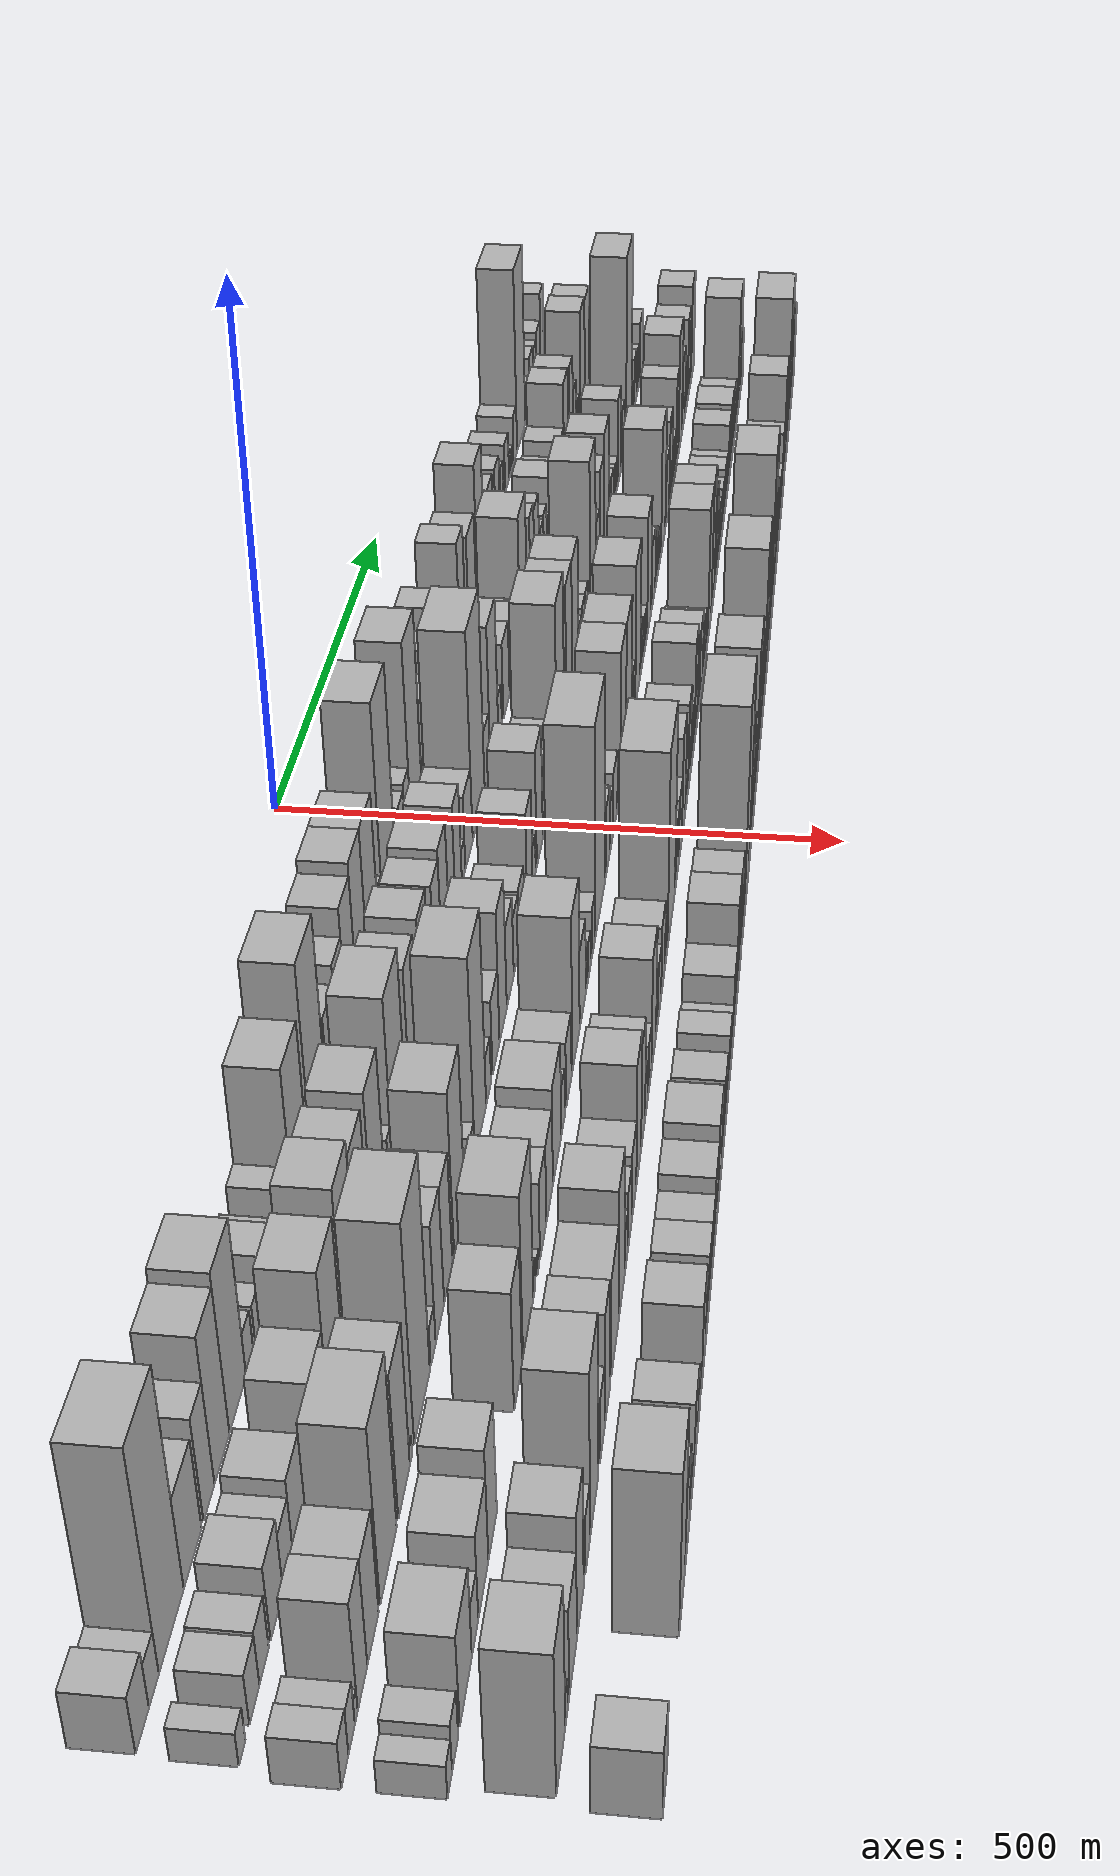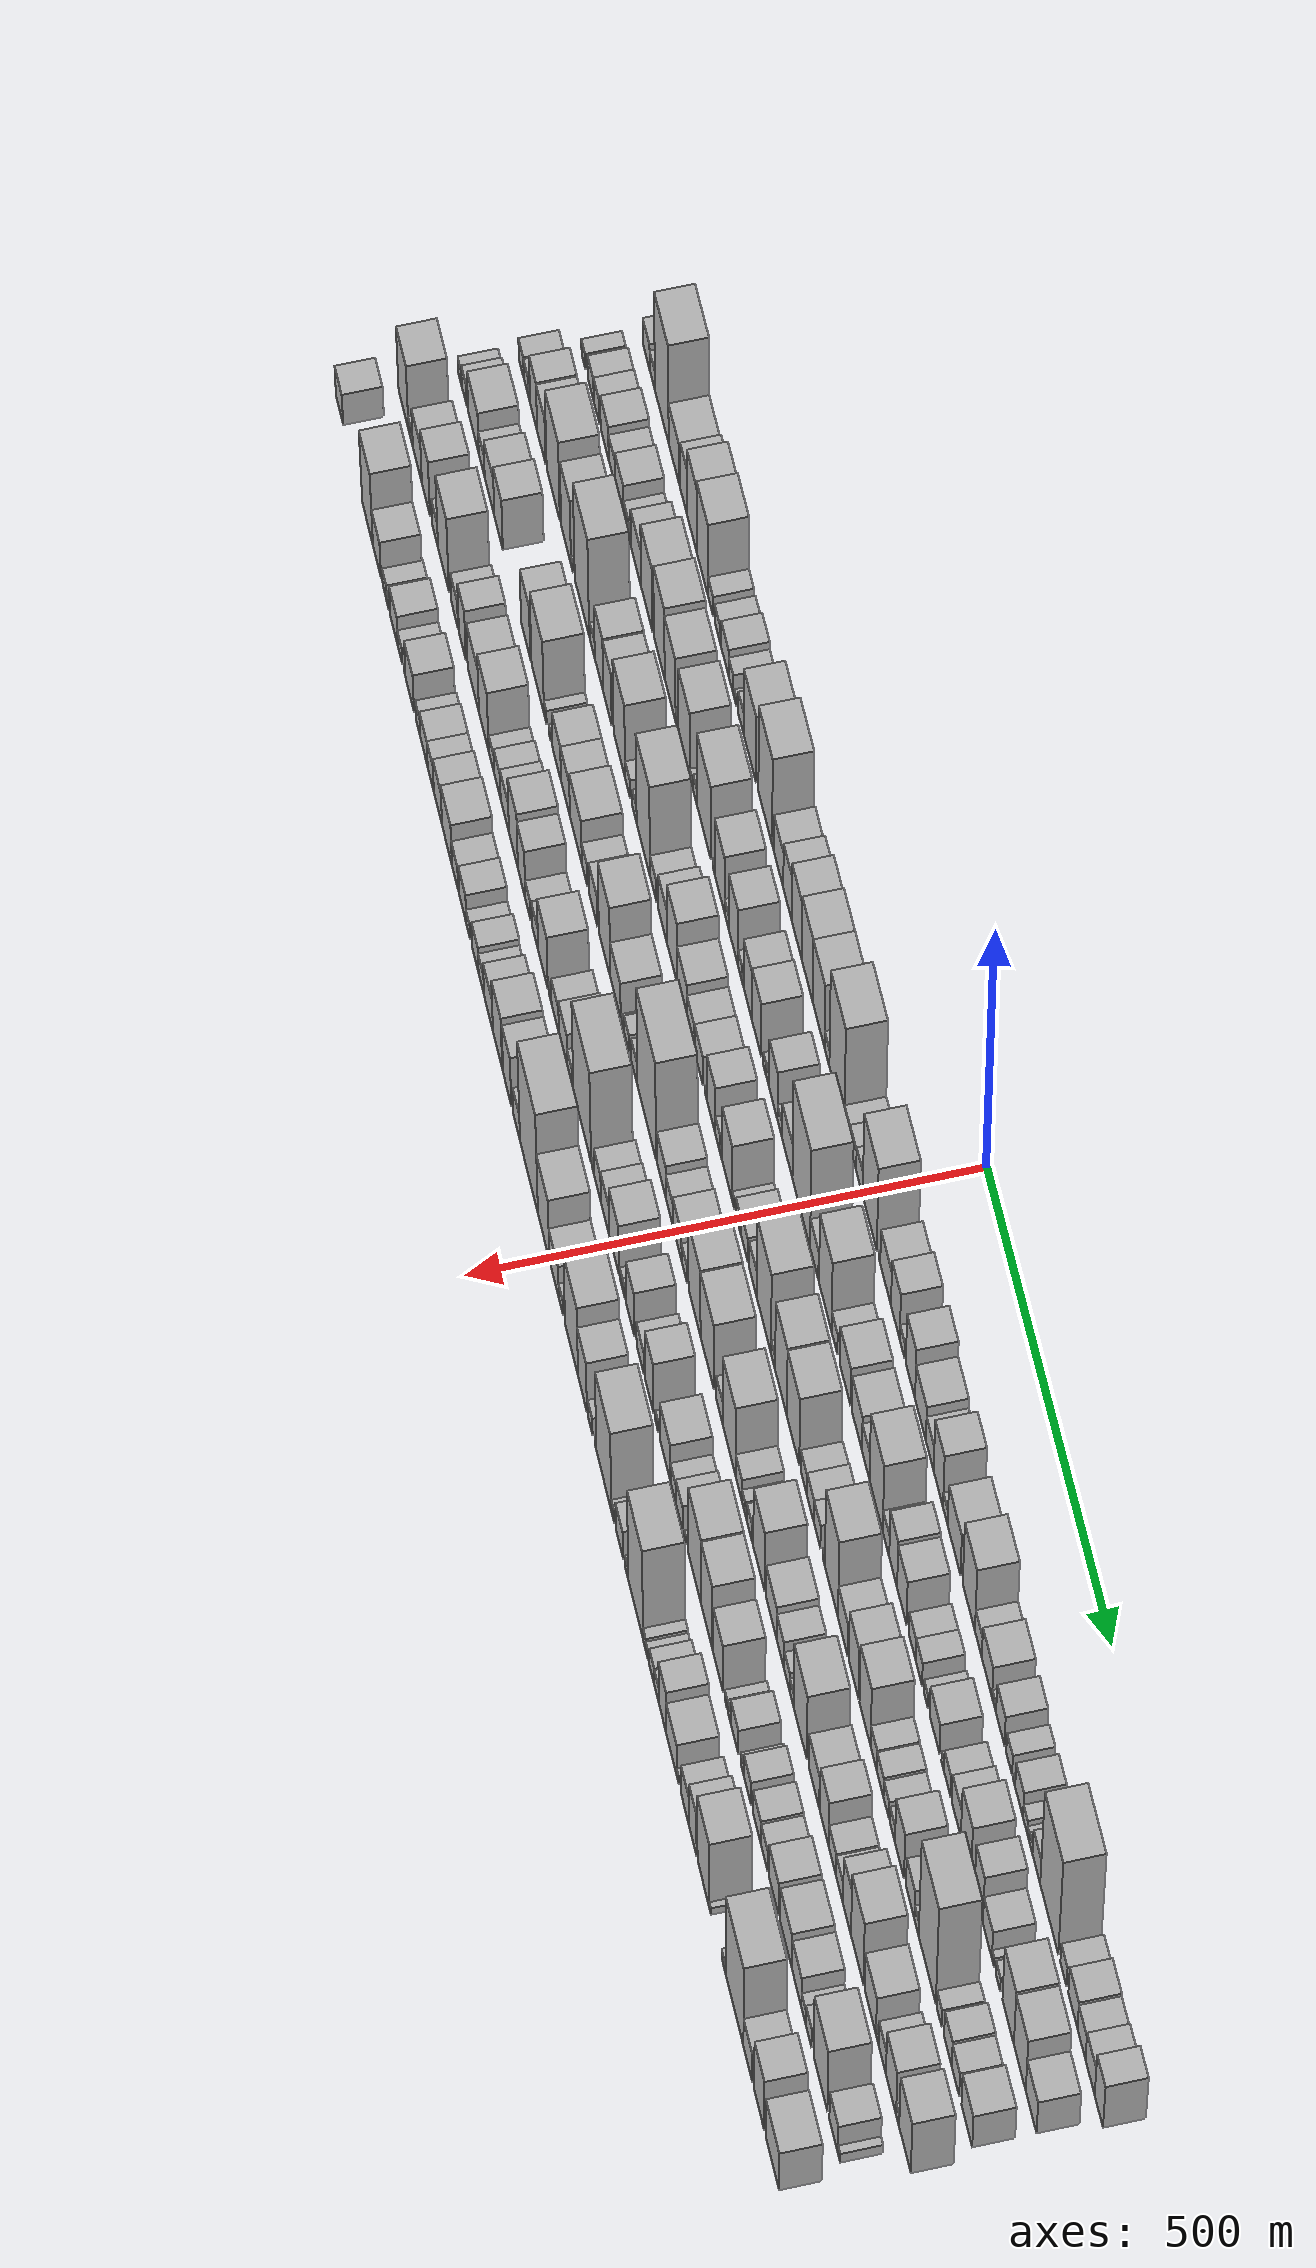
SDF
<sdf version="1.6">
 <world name="default">
  <scene>
   <sky><clouds><speed>12</speed></clouds></sky>
   <ambient>0.4 0.4 0.4 1</ambient>
   <background>0.7 0.7 0.7 1</background>
   <shadows>1</shadows>
  </scene>
  <gravity>0 0 -9.8066</gravity>
  <magnetic_field>6e-06 2.3e-05 -4.2e-05</magnetic_field>
  <physics default="0" name="default_physics" type="ode">
   <ode>
    <solver>
     <type>quick</type>
     <iters>10</iters>
     <sor>1.0</sor>
     <use_dynamic_moi_rescaling>0</use_dynamic_moi_rescaling>
    </solver>
    <constraints>
     <cfm>0</cfm>
     <erp>0.2</erp>
     <contact_max_correcting_vel>100</contact_max_correcting_vel>
     <contact_surface_layer>0.001</contact_surface_layer>
    </constraints>
   </ode>
   <max_step_size>0.004</max_step_size>
   <real_time_factor>1</real_time_factor>
   <real_time_update_rate>250</real_time_update_rate>
  </physics>
  <light name="sun" type="directional">
   <pose>0 0 10 0 0 0</pose>
   <diffuse>0.8 0.8 0.8 1</diffuse>
   <specular>0.2 0.2 0.2 1</specular>
   <attenuation>
    <range>1000</range>
    <constant>0.9</constant>
    <linear>0.01</linear>
    <quadratic>0.001</quadratic>
   </attenuation>
   <direction>-0.5 0.1 -0.9</direction>
  </light>
  <model name="building_1">
   <static>1</static>
   <pose>100.0000 -915.0961 0 0.000000 0.000000 0.000000</pose>
   <link name="link">
    <pose>0 0 25.50 0 0 0</pose>
    <collision name="collision"><geometry><box><size>40.0000 29.8078 51.0000</size></box></geometry></collision>
    <visual name="visual">
     <cast_shadows>0</cast_shadows>
     <geometry><box><size>40.0000 29.8078 51.0000</size></box></geometry>
     <material>
      <script>
       <uri>model://HANNAS_wall/materials/scripts</uri>
       <uri>model://HANNAS_wall/materials/textures</uri>
       <name>vrc/HANNAS_wall</name>
      </script>
     </material>
    </visual>
   </link>
  </model>
  <model name="building_2">
   <static>1</static>
   <pose>100.0000 -888.7581 0 0.000000 0.000000 0.000000</pose>
   <link name="link">
    <pose>0 0 19.50 0 0 0</pose>
    <collision name="collision"><geometry><box><size>40.0000 22.8681 39.0000</size></box></geometry></collision>
    <visual name="visual">
     <cast_shadows>0</cast_shadows>
     <geometry><box><size>40.0000 22.8681 39.0000</size></box></geometry>
     <material>
      <script>
       <uri>model://HANNAS_wall/materials/scripts</uri>
       <uri>model://HANNAS_wall/materials/textures</uri>
       <name>vrc/HANNAS_wall</name>
      </script>
     </material>
    </visual>
   </link>
  </model>
  <model name="building_3">
   <static>1</static>
   <pose>100.0000 -847.5174 0 0.000000 0.000000 0.000000</pose>
   <link name="link">
    <pose>0 0 97.50 0 0 0</pose>
    <collision name="collision"><geometry><box><size>40.0000 59.6133 195.0000</size></box></geometry></collision>
    <visual name="visual">
     <cast_shadows>0</cast_shadows>
     <geometry><box><size>40.0000 59.6133 195.0000</size></box></geometry>
     <material>
      <script>
       <uri>model://HANNAS_wall/materials/scripts</uri>
       <uri>model://HANNAS_wall/materials/textures</uri>
       <name>vrc/HANNAS_wall</name>
      </script>
     </material>
    </visual>
   </link>
  </model>
  <model name="building_4">
   <static>1</static>
   <pose>100.0000 -795.0078 0 0.000000 0.000000 0.000000</pose>
   <link name="link">
    <pose>0 0 40.50 0 0 0</pose>
    <collision name="collision"><geometry><box><size>40.0000 45.4060 81.0000</size></box></geometry></collision>
    <visual name="visual">
     <cast_shadows>0</cast_shadows>
     <geometry><box><size>40.0000 45.4060 81.0000</size></box></geometry>
     <material>
      <script>
       <uri>model://HANNAS_wall/materials/scripts</uri>
       <uri>model://HANNAS_wall/materials/textures</uri>
       <name>vrc/HANNAS_wall</name>
      </script>
     </material>
    </visual>
   </link>
  </model>
  <model name="building_5">
   <static>1</static>
   <pose>100.0000 -752.6553 0 0.000000 0.000000 0.000000</pose>
   <link name="link">
    <pose>0 0 46.50 0 0 0</pose>
    <collision name="collision"><geometry><box><size>40.0000 29.2990 93.0000</size></box></geometry></collision>
    <visual name="visual">
     <cast_shadows>0</cast_shadows>
     <geometry><box><size>40.0000 29.2990 93.0000</size></box></geometry>
     <material>
      <script>
       <uri>model://HANNAS_wall/materials/scripts</uri>
       <uri>model://HANNAS_wall/materials/textures</uri>
       <name>vrc/HANNAS_wall</name>
      </script>
     </material>
    </visual>
   </link>
  </model>
  <model name="building_6">
   <static>1</static>
   <pose>100.0000 -717.2906 0 0.000000 0.000000 0.000000</pose>
   <link name="link">
    <pose>0 0 66.00 0 0 0</pose>
    <collision name="collision"><geometry><box><size>40.0000 41.4303 132.0000</size></box></geometry></collision>
    <visual name="visual">
     <cast_shadows>0</cast_shadows>
     <geometry><box><size>40.0000 41.4303 132.0000</size></box></geometry>
     <material>
      <script>
       <uri>model://HANNAS_wall/materials/scripts</uri>
       <uri>model://HANNAS_wall/materials/textures</uri>
       <name>vrc/HANNAS_wall</name>
      </script>
     </material>
    </visual>
   </link>
  </model>
  <model name="building_7">
   <static>1</static>
   <pose>100.0000 -672.4441 0 0.000000 0.000000 0.000000</pose>
   <link name="link">
    <pose>0 0 72.00 0 0 0</pose>
    <collision name="collision"><geometry><box><size>40.0000 48.2628 144.0000</size></box></geometry></collision>
    <visual name="visual">
     <cast_shadows>0</cast_shadows>
     <geometry><box><size>40.0000 48.2628 144.0000</size></box></geometry>
     <material>
      <script>
       <uri>model://HANNAS_wall/materials/scripts</uri>
       <uri>model://HANNAS_wall/materials/textures</uri>
       <name>vrc/HANNAS_wall</name>
      </script>
     </material>
    </visual>
   </link>
  </model>
  <model name="building_8">
   <static>1</static>
   <pose>100.0000 -637.3235 0 0.000000 0.000000 0.000000</pose>
   <link name="link">
    <pose>0 0 19.50 0 0 0</pose>
    <collision name="collision"><geometry><box><size>40.0000 21.9783 39.0000</size></box></geometry></collision>
    <visual name="visual">
     <cast_shadows>0</cast_shadows>
     <geometry><box><size>40.0000 21.9783 39.0000</size></box></geometry>
     <material>
      <script>
       <uri>model://HANNAS_wall/materials/scripts</uri>
       <uri>model://HANNAS_wall/materials/textures</uri>
       <name>vrc/HANNAS_wall</name>
      </script>
     </material>
    </visual>
   </link>
  </model>
  <model name="building_9">
   <static>1</static>
   <pose>100.0000 -609.5402 0 0.000000 0.000000 0.000000</pose>
   <link name="link">
    <pose>0 0 18.00 0 0 0</pose>
    <collision name="collision"><geometry><box><size>40.0000 21.5883 36.0000</size></box></geometry></collision>
    <visual name="visual">
     <cast_shadows>0</cast_shadows>
     <geometry><box><size>40.0000 21.5883 36.0000</size></box></geometry>
     <material>
      <script>
       <uri>model://HANNAS_wall/materials/scripts</uri>
       <uri>model://HANNAS_wall/materials/textures</uri>
       <name>vrc/HANNAS_wall</name>
      </script>
     </material>
    </visual>
   </link>
  </model>
  <model name="building_10">
   <static>1</static>
   <pose>100.0000 -595.3261 0 0.000000 0.000000 0.000000</pose>
   <link name="link">
    <pose>0 0 7.50 0 0 0</pose>
    <collision name="collision"><geometry><box><size>40.0000 6.8400 15.0000</size></box></geometry></collision>
    <visual name="visual">
     <cast_shadows>0</cast_shadows>
     <geometry><box><size>40.0000 6.8400 15.0000</size></box></geometry>
     <material>
      <script>
       <uri>model://HANNAS_wall/materials/scripts</uri>
       <uri>model://HANNAS_wall/materials/textures</uri>
       <name>vrc/HANNAS_wall</name>
      </script>
     </material>
    </visual>
   </link>
  </model>
  <model name="building_11">
   <static>1</static>
   <pose>100.0000 -575.8475 0 0.000000 0.000000 0.000000</pose>
   <link name="link">
    <pose>0 0 27.00 0 0 0</pose>
    <collision name="collision"><geometry><box><size>40.0000 32.1174 54.0000</size></box></geometry></collision>
    <visual name="visual">
     <cast_shadows>0</cast_shadows>
     <geometry><box><size>40.0000 32.1174 54.0000</size></box></geometry>
     <material>
      <script>
       <uri>model://HANNAS_wall/materials/scripts</uri>
       <uri>model://HANNAS_wall/materials/textures</uri>
       <name>vrc/HANNAS_wall</name>
      </script>
     </material>
    </visual>
   </link>
  </model>
  <model name="building_12">
   <static>1</static>
   <pose>100.0000 -549.9825 0 0.000000 0.000000 0.000000</pose>
   <link name="link">
    <pose>0 0 19.50 0 0 0</pose>
    <collision name="collision"><geometry><box><size>40.0000 19.6125 39.0000</size></box></geometry></collision>
    <visual name="visual">
     <cast_shadows>0</cast_shadows>
     <geometry><box><size>40.0000 19.6125 39.0000</size></box></geometry>
     <material>
      <script>
       <uri>model://HANNAS_wall/materials/scripts</uri>
       <uri>model://HANNAS_wall/materials/textures</uri>
       <name>vrc/HANNAS_wall</name>
      </script>
     </material>
    </visual>
   </link>
  </model>
  <model name="building_13">
   <static>1</static>
   <pose>100.0000 -531.7579 0 0.000000 0.000000 0.000000</pose>
   <link name="link">
    <pose>0 0 9.00 0 0 0</pose>
    <collision name="collision"><geometry><box><size>40.0000 8.8366 18.0000</size></box></geometry></collision>
    <visual name="visual">
     <cast_shadows>0</cast_shadows>
     <geometry><box><size>40.0000 8.8366 18.0000</size></box></geometry>
     <material>
      <script>
       <uri>model://HANNAS_wall/materials/scripts</uri>
       <uri>model://HANNAS_wall/materials/textures</uri>
       <name>vrc/HANNAS_wall</name>
      </script>
     </material>
    </visual>
   </link>
  </model>
  <model name="building_14">
   <static>1</static>
   <pose>100.0000 -507.6548 0 0.000000 0.000000 0.000000</pose>
   <link name="link">
    <pose>0 0 22.50 0 0 0</pose>
    <collision name="collision"><geometry><box><size>40.0000 23.3695 45.0000</size></box></geometry></collision>
    <visual name="visual">
     <cast_shadows>0</cast_shadows>
     <geometry><box><size>40.0000 23.3695 45.0000</size></box></geometry>
     <material>
      <script>
       <uri>model://HANNAS_wall/materials/scripts</uri>
       <uri>model://HANNAS_wall/materials/textures</uri>
       <name>vrc/HANNAS_wall</name>
      </script>
     </material>
    </visual>
   </link>
  </model>
  <model name="building_15">
   <static>1</static>
   <pose>100.0000 -469.8242 0 0.000000 0.000000 0.000000</pose>
   <link name="link">
    <pose>0 0 67.50 0 0 0</pose>
    <collision name="collision"><geometry><box><size>40.0000 52.2918 135.0000</size></box></geometry></collision>
    <visual name="visual">
     <cast_shadows>0</cast_shadows>
     <geometry><box><size>40.0000 52.2918 135.0000</size></box></geometry>
     <material>
      <script>
       <uri>model://HANNAS_wall/materials/scripts</uri>
       <uri>model://HANNAS_wall/materials/textures</uri>
       <name>vrc/HANNAS_wall</name>
      </script>
     </material>
    </visual>
   </link>
  </model>
  <model name="building_16">
   <static>1</static>
   <pose>100.0000 -404.6347 0 0.000000 0.000000 0.000000</pose>
   <link name="link">
    <pose>0 0 88.50 0 0 0</pose>
    <collision name="collision"><geometry><box><size>40.0000 58.0870 177.0000</size></box></geometry></collision>
    <visual name="visual">
     <cast_shadows>0</cast_shadows>
     <geometry><box><size>40.0000 58.0870 177.0000</size></box></geometry>
     <material>
      <script>
       <uri>model://HANNAS_wall/materials/scripts</uri>
       <uri>model://HANNAS_wall/materials/textures</uri>
       <name>vrc/HANNAS_wall</name>
      </script>
     </material>
    </visual>
   </link>
  </model>
  <model name="building_17">
   <static>1</static>
   <pose>100.0000 -372.4116 0 0.000000 0.000000 0.000000</pose>
   <link name="link">
    <pose>0 0 7.50 0 0 0</pose>
    <collision name="collision"><geometry><box><size>40.0000 6.3594 15.0000</size></box></geometry></collision>
    <visual name="visual">
     <cast_shadows>0</cast_shadows>
     <geometry><box><size>40.0000 6.3594 15.0000</size></box></geometry>
     <material>
      <script>
       <uri>model://HANNAS_wall/materials/scripts</uri>
       <uri>model://HANNAS_wall/materials/textures</uri>
       <name>vrc/HANNAS_wall</name>
      </script>
     </material>
    </visual>
   </link>
  </model>
  <model name="building_18">
   <static>1</static>
   <pose>100.0000 -348.9371 0 0.000000 0.000000 0.000000</pose>
   <link name="link">
    <pose>0 0 37.50 0 0 0</pose>
    <collision name="collision"><geometry><box><size>40.0000 40.5896 75.0000</size></box></geometry></collision>
    <visual name="visual">
     <cast_shadows>0</cast_shadows>
     <geometry><box><size>40.0000 40.5896 75.0000</size></box></geometry>
     <material>
      <script>
       <uri>model://HANNAS_wall/materials/scripts</uri>
       <uri>model://HANNAS_wall/materials/textures</uri>
       <name>vrc/HANNAS_wall</name>
      </script>
     </material>
    </visual>
   </link>
  </model>
  <model name="building_19">
   <static>1</static>
   <pose>100.0000 -311.1034 0 0.000000 0.000000 0.000000</pose>
   <link name="link">
    <pose>0 0 46.50 0 0 0</pose>
    <collision name="collision"><geometry><box><size>40.0000 35.0779 93.0000</size></box></geometry></collision>
    <visual name="visual">
     <cast_shadows>0</cast_shadows>
     <geometry><box><size>40.0000 35.0779 93.0000</size></box></geometry>
     <material>
      <script>
       <uri>model://HANNAS_wall/materials/scripts</uri>
       <uri>model://HANNAS_wall/materials/textures</uri>
       <name>vrc/HANNAS_wall</name>
      </script>
     </material>
    </visual>
   </link>
  </model>
  <model name="building_20">
   <static>1</static>
   <pose>100.0000 -272.7175 0 0.000000 0.000000 0.000000</pose>
   <link name="link">
    <pose>0 0 60.00 0 0 0</pose>
    <collision name="collision"><geometry><box><size>40.0000 41.6939 120.0000</size></box></geometry></collision>
    <visual name="visual">
     <cast_shadows>0</cast_shadows>
     <geometry><box><size>40.0000 41.6939 120.0000</size></box></geometry>
     <material>
      <script>
       <uri>model://HANNAS_wall/materials/scripts</uri>
       <uri>model://HANNAS_wall/materials/textures</uri>
       <name>vrc/HANNAS_wall</name>
      </script>
     </material>
    </visual>
   </link>
  </model>
  <model name="building_21">
   <static>1</static>
   <pose>100.0000 -228.9761 0 0.000000 0.000000 0.000000</pose>
   <link name="link">
    <pose>0 0 66.00 0 0 0</pose>
    <collision name="collision"><geometry><box><size>40.0000 45.7889 132.0000</size></box></geometry></collision>
    <visual name="visual">
     <cast_shadows>0</cast_shadows>
     <geometry><box><size>40.0000 45.7889 132.0000</size></box></geometry>
     <material>
      <script>
       <uri>model://HANNAS_wall/materials/scripts</uri>
       <uri>model://HANNAS_wall/materials/textures</uri>
       <name>vrc/HANNAS_wall</name>
      </script>
     </material>
    </visual>
   </link>
  </model>
  <model name="building_22">
   <static>1</static>
   <pose>100.0000 -181.2982 0 0.000000 0.000000 0.000000</pose>
   <link name="link">
    <pose>0 0 66.00 0 0 0</pose>
    <collision name="collision"><geometry><box><size>40.0000 49.5669 132.0000</size></box></geometry></collision>
    <visual name="visual">
     <cast_shadows>0</cast_shadows>
     <geometry><box><size>40.0000 49.5669 132.0000</size></box></geometry>
     <material>
      <script>
       <uri>model://HANNAS_wall/materials/scripts</uri>
       <uri>model://HANNAS_wall/materials/textures</uri>
       <name>vrc/HANNAS_wall</name>
      </script>
     </material>
    </visual>
   </link>
  </model>
  <model name="building_23">
   <static>1</static>
   <pose>100.0000 -146.3929 0 0.000000 0.000000 0.000000</pose>
   <link name="link">
    <pose>0 0 18.00 0 0 0</pose>
    <collision name="collision"><geometry><box><size>40.0000 20.2436 36.0000</size></box></geometry></collision>
    <visual name="visual">
     <cast_shadows>0</cast_shadows>
     <geometry><box><size>40.0000 20.2436 36.0000</size></box></geometry>
     <material>
      <script>
       <uri>model://HANNAS_wall/materials/scripts</uri>
       <uri>model://HANNAS_wall/materials/textures</uri>
       <name>vrc/HANNAS_wall</name>
      </script>
     </material>
    </visual>
   </link>
  </model>
  <model name="building_24">
   <static>1</static>
   <pose>100.0000 -105.3213 0 0.000000 0.000000 0.000000</pose>
   <link name="link">
    <pose>0 0 102.00 0 0 0</pose>
    <collision name="collision"><geometry><box><size>40.0000 61.8996 204.0000</size></box></geometry></collision>
    <visual name="visual">
     <cast_shadows>0</cast_shadows>
     <geometry><box><size>40.0000 61.8996 204.0000</size></box></geometry>
     <material>
      <script>
       <uri>model://HANNAS_wall/materials/scripts</uri>
       <uri>model://HANNAS_wall/materials/textures</uri>
       <name>vrc/HANNAS_wall</name>
      </script>
     </material>
    </visual>
   </link>
  </model>
  <model name="building_25">
   <static>1</static>
   <pose>100.0000 -63.1519 0 0.000000 0.000000 0.000000</pose>
   <link name="link">
    <pose>0 0 21.00 0 0 0</pose>
    <collision name="collision"><geometry><box><size>40.0000 22.4393 42.0000</size></box></geometry></collision>
    <visual name="visual">
     <cast_shadows>0</cast_shadows>
     <geometry><box><size>40.0000 22.4393 42.0000</size></box></geometry>
     <material>
      <script>
       <uri>model://HANNAS_wall/materials/scripts</uri>
       <uri>model://HANNAS_wall/materials/textures</uri>
       <name>vrc/HANNAS_wall</name>
      </script>
     </material>
    </visual>
   </link>
  </model>
  <model name="building_26">
   <static>1</static>
   <pose>100.0000 -38.5677 0 0.000000 0.000000 0.000000</pose>
   <link name="link">
    <pose>0 0 22.50 0 0 0</pose>
    <collision name="collision"><geometry><box><size>40.0000 26.7291 45.0000</size></box></geometry></collision>
    <visual name="visual">
     <cast_shadows>0</cast_shadows>
     <geometry><box><size>40.0000 26.7291 45.0000</size></box></geometry>
     <material>
      <script>
       <uri>model://HANNAS_wall/materials/scripts</uri>
       <uri>model://HANNAS_wall/materials/textures</uri>
       <name>vrc/HANNAS_wall</name>
      </script>
     </material>
    </visual>
   </link>
  </model>
  <model name="building_27">
   <static>1</static>
   <pose>100.0000 -11.8745 0 0.000000 0.000000 0.000000</pose>
   <link name="link">
    <pose>0 0 25.50 0 0 0</pose>
    <collision name="collision"><geometry><box><size>40.0000 26.6573 51.0000</size></box></geometry></collision>
    <visual name="visual">
     <cast_shadows>0</cast_shadows>
     <geometry><box><size>40.0000 26.6573 51.0000</size></box></geometry>
     <material>
      <script>
       <uri>model://HANNAS_wall/materials/scripts</uri>
       <uri>model://HANNAS_wall/materials/textures</uri>
       <name>vrc/HANNAS_wall</name>
      </script>
     </material>
    </visual>
   </link>
  </model>
  <model name="building_28">
   <static>1</static>
   <pose>100.0000 30.4601 0 0.000000 0.000000 0.000000</pose>
   <link name="link">
    <pose>0 0 88.50 0 0 0</pose>
    <collision name="collision"><geometry><box><size>40.0000 58.0119 177.0000</size></box></geometry></collision>
    <visual name="visual">
     <cast_shadows>0</cast_shadows>
     <geometry><box><size>40.0000 58.0119 177.0000</size></box></geometry>
     <material>
      <script>
       <uri>model://HANNAS_wall/materials/scripts</uri>
       <uri>model://HANNAS_wall/materials/textures</uri>
       <name>vrc/HANNAS_wall</name>
      </script>
     </material>
    </visual>
   </link>
  </model>
  <model name="building_29">
   <static>1</static>
   <pose>100.0000 70.5219 0 0.000000 0.000000 0.000000</pose>
   <link name="link">
    <pose>0 0 7.50 0 0 0</pose>
    <collision name="collision"><geometry><box><size>40.0000 6.1116 15.0000</size></box></geometry></collision>
    <visual name="visual">
     <cast_shadows>0</cast_shadows>
     <geometry><box><size>40.0000 6.1116 15.0000</size></box></geometry>
     <material>
      <script>
       <uri>model://HANNAS_wall/materials/scripts</uri>
       <uri>model://HANNAS_wall/materials/textures</uri>
       <name>vrc/HANNAS_wall</name>
      </script>
     </material>
    </visual>
   </link>
  </model>
  <model name="building_30">
   <static>1</static>
   <pose>100.0000 95.6432 0 0.000000 0.000000 0.000000</pose>
   <link name="link">
    <pose>0 0 37.50 0 0 0</pose>
    <collision name="collision"><geometry><box><size>40.0000 44.1311 75.0000</size></box></geometry></collision>
    <visual name="visual">
     <cast_shadows>0</cast_shadows>
     <geometry><box><size>40.0000 44.1311 75.0000</size></box></geometry>
     <material>
      <script>
       <uri>model://HANNAS_wall/materials/scripts</uri>
       <uri>model://HANNAS_wall/materials/textures</uri>
       <name>vrc/HANNAS_wall</name>
      </script>
     </material>
    </visual>
   </link>
  </model>
  <model name="building_31">
   <static>1</static>
   <pose>100.0000 135.5213 0 0.000000 0.000000 0.000000</pose>
   <link name="link">
    <pose>0 0 49.50 0 0 0</pose>
    <collision name="collision"><geometry><box><size>40.0000 35.6252 99.0000</size></box></geometry></collision>
    <visual name="visual">
     <cast_shadows>0</cast_shadows>
     <geometry><box><size>40.0000 35.6252 99.0000</size></box></geometry>
     <material>
      <script>
       <uri>model://HANNAS_wall/materials/scripts</uri>
       <uri>model://HANNAS_wall/materials/textures</uri>
       <name>vrc/HANNAS_wall</name>
      </script>
     </material>
    </visual>
   </link>
  </model>
  <model name="building_32">
   <static>1</static>
   <pose>100.0000 163.1861 0 0.000000 0.000000 0.000000</pose>
   <link name="link">
    <pose>0 0 16.50 0 0 0</pose>
    <collision name="collision"><geometry><box><size>40.0000 19.7042 33.0000</size></box></geometry></collision>
    <visual name="visual">
     <cast_shadows>0</cast_shadows>
     <geometry><box><size>40.0000 19.7042 33.0000</size></box></geometry>
     <material>
      <script>
       <uri>model://HANNAS_wall/materials/scripts</uri>
       <uri>model://HANNAS_wall/materials/textures</uri>
       <name>vrc/HANNAS_wall</name>
      </script>
     </material>
    </visual>
   </link>
  </model>
  <model name="building_33">
   <static>1</static>
   <pose>100.0000 196.7859 0 0.000000 0.000000 0.000000</pose>
   <link name="link">
    <pose>0 0 54.00 0 0 0</pose>
    <collision name="collision"><geometry><box><size>40.0000 37.4955 108.0000</size></box></geometry></collision>
    <visual name="visual">
     <cast_shadows>0</cast_shadows>
     <geometry><box><size>40.0000 37.4955 108.0000</size></box></geometry>
     <material>
      <script>
       <uri>model://HANNAS_wall/materials/scripts</uri>
       <uri>model://HANNAS_wall/materials/textures</uri>
       <name>vrc/HANNAS_wall</name>
      </script>
     </material>
    </visual>
   </link>
  </model>
  <model name="building_34">
   <static>1</static>
   <pose>100.0000 237.4932 0 0.000000 0.000000 0.000000</pose>
   <link name="link">
    <pose>0 0 37.50 0 0 0</pose>
    <collision name="collision"><geometry><box><size>40.0000 43.9191 75.0000</size></box></geometry></collision>
    <visual name="visual">
     <cast_shadows>0</cast_shadows>
     <geometry><box><size>40.0000 43.9191 75.0000</size></box></geometry>
     <material>
      <script>
       <uri>model://HANNAS_wall/materials/scripts</uri>
       <uri>model://HANNAS_wall/materials/textures</uri>
       <name>vrc/HANNAS_wall</name>
      </script>
     </material>
    </visual>
   </link>
  </model>
  <model name="building_35">
   <static>1</static>
   <pose>100.0000 275.1679 0 0.000000 0.000000 0.000000</pose>
   <link name="link">
    <pose>0 0 27.00 0 0 0</pose>
    <collision name="collision"><geometry><box><size>40.0000 31.4303 54.0000</size></box></geometry></collision>
    <visual name="visual">
     <cast_shadows>0</cast_shadows>
     <geometry><box><size>40.0000 31.4303 54.0000</size></box></geometry>
     <material>
      <script>
       <uri>model://HANNAS_wall/materials/scripts</uri>
       <uri>model://HANNAS_wall/materials/textures</uri>
       <name>vrc/HANNAS_wall</name>
      </script>
     </material>
    </visual>
   </link>
  </model>
  <model name="building_36">
   <static>1</static>
   <pose>100.0000 309.7557 0 0.000000 0.000000 0.000000</pose>
   <link name="link">
    <pose>0 0 57.00 0 0 0</pose>
    <collision name="collision"><geometry><box><size>40.0000 37.7454 114.0000</size></box></geometry></collision>
    <visual name="visual">
     <cast_shadows>0</cast_shadows>
     <geometry><box><size>40.0000 37.7454 114.0000</size></box></geometry>
     <material>
      <script>
       <uri>model://HANNAS_wall/materials/scripts</uri>
       <uri>model://HANNAS_wall/materials/textures</uri>
       <name>vrc/HANNAS_wall</name>
      </script>
     </material>
    </visual>
   </link>
  </model>
  <model name="building_37">
   <static>1</static>
   <pose>100.0000 337.9935 0 0.000000 0.000000 0.000000</pose>
   <link name="link">
    <pose>0 0 16.50 0 0 0</pose>
    <collision name="collision"><geometry><box><size>40.0000 18.7301 33.0000</size></box></geometry></collision>
    <visual name="visual">
     <cast_shadows>0</cast_shadows>
     <geometry><box><size>40.0000 18.7301 33.0000</size></box></geometry>
     <material>
      <script>
       <uri>model://HANNAS_wall/materials/scripts</uri>
       <uri>model://HANNAS_wall/materials/textures</uri>
       <name>vrc/HANNAS_wall</name>
      </script>
     </material>
    </visual>
   </link>
  </model>
  <model name="building_38">
   <static>1</static>
   <pose>100.0000 373.1869 0 0.000000 0.000000 0.000000</pose>
   <link name="link">
    <pose>0 0 45.00 0 0 0</pose>
    <collision name="collision"><geometry><box><size>40.0000 51.6567 90.0000</size></box></geometry></collision>
    <visual name="visual">
     <cast_shadows>0</cast_shadows>
     <geometry><box><size>40.0000 51.6567 90.0000</size></box></geometry>
     <material>
      <script>
       <uri>model://HANNAS_wall/materials/scripts</uri>
       <uri>model://HANNAS_wall/materials/textures</uri>
       <name>vrc/HANNAS_wall</name>
      </script>
     </material>
    </visual>
   </link>
  </model>
  <model name="building_39">
   <static>1</static>
   <pose>100.0000 432.4017 0 0.000000 0.000000 0.000000</pose>
   <link name="link">
    <pose>0 0 69.00 0 0 0</pose>
    <collision name="collision"><geometry><box><size>40.0000 48.7731 138.0000</size></box></geometry></collision>
    <visual name="visual">
     <cast_shadows>0</cast_shadows>
     <geometry><box><size>40.0000 48.7731 138.0000</size></box></geometry>
     <material>
      <script>
       <uri>model://HANNAS_wall/materials/scripts</uri>
       <uri>model://HANNAS_wall/materials/textures</uri>
       <name>vrc/HANNAS_wall</name>
      </script>
     </material>
    </visual>
   </link>
  </model>
  <model name="building_40">
   <static>1</static>
   <pose>100.0000 470.5657 0 0.000000 0.000000 0.000000</pose>
   <link name="link">
    <pose>0 0 24.00 0 0 0</pose>
    <collision name="collision"><geometry><box><size>40.0000 27.5548 48.0000</size></box></geometry></collision>
    <visual name="visual">
     <cast_shadows>0</cast_shadows>
     <geometry><box><size>40.0000 27.5548 48.0000</size></box></geometry>
     <material>
      <script>
       <uri>model://HANNAS_wall/materials/scripts</uri>
       <uri>model://HANNAS_wall/materials/textures</uri>
       <name>vrc/HANNAS_wall</name>
      </script>
     </material>
    </visual>
   </link>
  </model>
  <model name="building_41">
   <static>1</static>
   <pose>100.0000 504.8800 0 0.000000 0.000000 0.000000</pose>
   <link name="link">
    <pose>0 0 34.50 0 0 0</pose>
    <collision name="collision"><geometry><box><size>40.0000 41.0738 69.0000</size></box></geometry></collision>
    <visual name="visual">
     <cast_shadows>0</cast_shadows>
     <geometry><box><size>40.0000 41.0738 69.0000</size></box></geometry>
     <material>
      <script>
       <uri>model://HANNAS_wall/materials/scripts</uri>
       <uri>model://HANNAS_wall/materials/textures</uri>
       <name>vrc/HANNAS_wall</name>
      </script>
     </material>
    </visual>
   </link>
  </model>
  <model name="building_42">
   <static>1</static>
   <pose>100.0000 529.8861 0 0.000000 0.000000 0.000000</pose>
   <link name="link">
    <pose>0 0 9.00 0 0 0</pose>
    <collision name="collision"><geometry><box><size>40.0000 8.9385 18.0000</size></box></geometry></collision>
    <visual name="visual">
     <cast_shadows>0</cast_shadows>
     <geometry><box><size>40.0000 8.9385 18.0000</size></box></geometry>
     <material>
      <script>
       <uri>model://HANNAS_wall/materials/scripts</uri>
       <uri>model://HANNAS_wall/materials/textures</uri>
       <name>vrc/HANNAS_wall</name>
      </script>
     </material>
    </visual>
   </link>
  </model>
  <model name="building_43">
   <static>1</static>
   <pose>100.0000 537.8323 0 0.000000 0.000000 0.000000</pose>
   <link name="link">
    <pose>0 0 7.50 0 0 0</pose>
    <collision name="collision"><geometry><box><size>40.0000 6.9539 15.0000</size></box></geometry></collision>
    <visual name="visual">
     <cast_shadows>0</cast_shadows>
     <geometry><box><size>40.0000 6.9539 15.0000</size></box></geometry>
     <material>
      <script>
       <uri>model://HANNAS_wall/materials/scripts</uri>
       <uri>model://HANNAS_wall/materials/textures</uri>
       <name>vrc/HANNAS_wall</name>
      </script>
     </material>
    </visual>
   </link>
  </model>
  <model name="building_44">
   <static>1</static>
   <pose>100.0000 557.9653 0 0.000000 0.000000 0.000000</pose>
   <link name="link">
    <pose>0 0 33.00 0 0 0</pose>
    <collision name="collision"><geometry><box><size>40.0000 33.3122 66.0000</size></box></geometry></collision>
    <visual name="visual">
     <cast_shadows>0</cast_shadows>
     <geometry><box><size>40.0000 33.3122 66.0000</size></box></geometry>
     <material>
      <script>
       <uri>model://HANNAS_wall/materials/scripts</uri>
       <uri>model://HANNAS_wall/materials/textures</uri>
       <name>vrc/HANNAS_wall</name>
      </script>
     </material>
    </visual>
   </link>
  </model>
  <model name="building_45">
   <static>1</static>
   <pose>100.0000 593.1495 0 0.000000 0.000000 0.000000</pose>
   <link name="link">
    <pose>0 0 22.50 0 0 0</pose>
    <collision name="collision"><geometry><box><size>40.0000 23.0561 45.0000</size></box></geometry></collision>
    <visual name="visual">
     <cast_shadows>0</cast_shadows>
     <geometry><box><size>40.0000 23.0561 45.0000</size></box></geometry>
     <material>
      <script>
       <uri>model://HANNAS_wall/materials/scripts</uri>
       <uri>model://HANNAS_wall/materials/textures</uri>
       <name>vrc/HANNAS_wall</name>
      </script>
     </material>
    </visual>
   </link>
  </model>
  <model name="building_46">
   <static>1</static>
   <pose>100.0000 613.3824 0 0.000000 0.000000 0.000000</pose>
   <link name="link">
    <pose>0 0 7.50 0 0 0</pose>
    <collision name="collision"><geometry><box><size>40.0000 7.4097 15.0000</size></box></geometry></collision>
    <visual name="visual">
     <cast_shadows>0</cast_shadows>
     <geometry><box><size>40.0000 7.4097 15.0000</size></box></geometry>
     <material>
      <script>
       <uri>model://HANNAS_wall/materials/scripts</uri>
       <uri>model://HANNAS_wall/materials/textures</uri>
       <name>vrc/HANNAS_wall</name>
      </script>
     </material>
    </visual>
   </link>
  </model>
  <model name="building_47">
   <static>1</static>
   <pose>100.0000 632.5003 0 0.000000 0.000000 0.000000</pose>
   <link name="link">
    <pose>0 0 28.50 0 0 0</pose>
    <collision name="collision"><geometry><box><size>40.0000 30.8263 57.0000</size></box></geometry></collision>
    <visual name="visual">
     <cast_shadows>0</cast_shadows>
     <geometry><box><size>40.0000 30.8263 57.0000</size></box></geometry>
     <material>
      <script>
       <uri>model://HANNAS_wall/materials/scripts</uri>
       <uri>model://HANNAS_wall/materials/textures</uri>
       <name>vrc/HANNAS_wall</name>
      </script>
     </material>
    </visual>
   </link>
  </model>
  <model name="building_48">
   <static>1</static>
   <pose>100.0000 656.2029 0 0.000000 0.000000 0.000000</pose>
   <link name="link">
    <pose>0 0 15.00 0 0 0</pose>
    <collision name="collision"><geometry><box><size>40.0000 16.5787 30.0000</size></box></geometry></collision>
    <visual name="visual">
     <cast_shadows>0</cast_shadows>
     <geometry><box><size>40.0000 16.5787 30.0000</size></box></geometry>
     <material>
      <script>
       <uri>model://HANNAS_wall/materials/scripts</uri>
       <uri>model://HANNAS_wall/materials/textures</uri>
       <name>vrc/HANNAS_wall</name>
      </script>
     </material>
    </visual>
   </link>
  </model>
  <model name="building_49">
   <static>1</static>
   <pose>100.0000 668.9546 0 0.000000 0.000000 0.000000</pose>
   <link name="link">
    <pose>0 0 9.00 0 0 0</pose>
    <collision name="collision"><geometry><box><size>40.0000 8.9249 18.0000</size></box></geometry></collision>
    <visual name="visual">
     <cast_shadows>0</cast_shadows>
     <geometry><box><size>40.0000 8.9249 18.0000</size></box></geometry>
     <material>
      <script>
       <uri>model://HANNAS_wall/materials/scripts</uri>
       <uri>model://HANNAS_wall/materials/textures</uri>
       <name>vrc/HANNAS_wall</name>
      </script>
     </material>
    </visual>
   </link>
  </model>
  <model name="building_50">
   <static>1</static>
   <pose>100.0000 679.3820 0 0.000000 0.000000 0.000000</pose>
   <link name="link">
    <pose>0 0 12.00 0 0 0</pose>
    <collision name="collision"><geometry><box><size>40.0000 11.9298 24.0000</size></box></geometry></collision>
    <visual name="visual">
     <cast_shadows>0</cast_shadows>
     <geometry><box><size>40.0000 11.9298 24.0000</size></box></geometry>
     <material>
      <script>
       <uri>model://HANNAS_wall/materials/scripts</uri>
       <uri>model://HANNAS_wall/materials/textures</uri>
       <name>vrc/HANNAS_wall</name>
      </script>
     </material>
    </visual>
   </link>
  </model>
  <model name="building_51">
   <static>1</static>
   <pose>100.0000 700.5636 0 0.000000 0.000000 0.000000</pose>
   <link name="link">
    <pose>0 0 28.50 0 0 0</pose>
    <collision name="collision"><geometry><box><size>40.0000 30.4335 57.0000</size></box></geometry></collision>
    <visual name="visual">
     <cast_shadows>0</cast_shadows>
     <geometry><box><size>40.0000 30.4335 57.0000</size></box></geometry>
     <material>
      <script>
       <uri>model://HANNAS_wall/materials/scripts</uri>
       <uri>model://HANNAS_wall/materials/textures</uri>
       <name>vrc/HANNAS_wall</name>
      </script>
     </material>
    </visual>
   </link>
  </model>
  <model name="building_52">
   <static>1</static>
   <pose>100.0000 751.2655 0 0.000000 0.000000 0.000000</pose>
   <link name="link">
    <pose>0 0 108.00 0 0 0</pose>
    <collision name="collision"><geometry><box><size>40.0000 70.9704 216.0000</size></box></geometry></collision>
    <visual name="visual">
     <cast_shadows>0</cast_shadows>
     <geometry><box><size>40.0000 70.9704 216.0000</size></box></geometry>
     <material>
      <script>
       <uri>model://HANNAS_wall/materials/scripts</uri>
       <uri>model://HANNAS_wall/materials/textures</uri>
       <name>vrc/HANNAS_wall</name>
      </script>
     </material>
    </visual>
   </link>
  </model>
  <model name="building_53">
   <static>1</static>
   <pose>100.0000 806.9127 0 0.000000 0.000000 0.000000</pose>
   <link name="link">
    <pose>0 0 22.50 0 0 0</pose>
    <collision name="collision"><geometry><box><size>40.0000 24.3240 45.0000</size></box></geometry></collision>
    <visual name="visual">
     <cast_shadows>0</cast_shadows>
     <geometry><box><size>40.0000 24.3240 45.0000</size></box></geometry>
     <material>
      <script>
       <uri>model://HANNAS_wall/materials/scripts</uri>
       <uri>model://HANNAS_wall/materials/textures</uri>
       <name>vrc/HANNAS_wall</name>
      </script>
     </material>
    </visual>
   </link>
  </model>
  <model name="building_54">
   <static>1</static>
   <pose>100.0000 843.8840 0 0.000000 0.000000 0.000000</pose>
   <link name="link">
    <pose>0 0 31.50 0 0 0</pose>
    <collision name="collision"><geometry><box><size>40.0000 35.6187 63.0000</size></box></geometry></collision>
    <visual name="visual">
     <cast_shadows>0</cast_shadows>
     <geometry><box><size>40.0000 35.6187 63.0000</size></box></geometry>
     <material>
      <script>
       <uri>model://HANNAS_wall/materials/scripts</uri>
       <uri>model://HANNAS_wall/materials/textures</uri>
       <name>vrc/HANNAS_wall</name>
      </script>
     </material>
    </visual>
   </link>
  </model>
  <model name="building_55">
   <static>1</static>
   <pose>100.0000 877.3269 0 0.000000 0.000000 0.000000</pose>
   <link name="link">
    <pose>0 0 28.50 0 0 0</pose>
    <collision name="collision"><geometry><box><size>40.0000 31.2671 57.0000</size></box></geometry></collision>
    <visual name="visual">
     <cast_shadows>0</cast_shadows>
     <geometry><box><size>40.0000 31.2671 57.0000</size></box></geometry>
     <material>
      <script>
       <uri>model://HANNAS_wall/materials/scripts</uri>
       <uri>model://HANNAS_wall/materials/textures</uri>
       <name>vrc/HANNAS_wall</name>
      </script>
     </material>
    </visual>
   </link>
  </model>
  <model name="building_56">
   <static>1</static>
   <pose>100.0000 910.8235 0 0.000000 0.000000 0.000000</pose>
   <link name="link">
    <pose>0 0 33.00 0 0 0</pose>
    <collision name="collision"><geometry><box><size>40.0000 35.7262 66.0000</size></box></geometry></collision>
    <visual name="visual">
     <cast_shadows>0</cast_shadows>
     <geometry><box><size>40.0000 35.7262 66.0000</size></box></geometry>
     <material>
      <script>
       <uri>model://HANNAS_wall/materials/scripts</uri>
       <uri>model://HANNAS_wall/materials/textures</uri>
       <name>vrc/HANNAS_wall</name>
      </script>
     </material>
    </visual>
   </link>
  </model>
  <model name="building_57">
   <static>1</static>
   <pose>100.0000 944.7487 0 0.000000 0.000000 0.000000</pose>
   <link name="link">
    <pose>0 0 49.50 0 0 0</pose>
    <collision name="collision"><geometry><box><size>40.0000 32.1241 99.0000</size></box></geometry></collision>
    <visual name="visual">
     <cast_shadows>0</cast_shadows>
     <geometry><box><size>40.0000 32.1241 99.0000</size></box></geometry>
     <material>
      <script>
       <uri>model://HANNAS_wall/materials/scripts</uri>
       <uri>model://HANNAS_wall/materials/textures</uri>
       <name>vrc/HANNAS_wall</name>
      </script>
     </material>
    </visual>
   </link>
  </model>
  <model name="building_58">
   <static>1</static>
   <pose>160.0000 -923.6007 0 0.000000 0.000000 0.000000</pose>
   <link name="link">
    <pose>0 0 15.00 0 0 0</pose>
    <collision name="collision"><geometry><box><size>40.0000 16.7985 30.0000</size></box></geometry></collision>
    <visual name="visual">
     <cast_shadows>0</cast_shadows>
     <geometry><box><size>40.0000 16.7985 30.0000</size></box></geometry>
     <material>
      <script>
       <uri>model://HANNAS_wall/materials/scripts</uri>
       <uri>model://HANNAS_wall/materials/textures</uri>
       <name>vrc/HANNAS_wall</name>
      </script>
     </material>
    </visual>
   </link>
  </model>
  <model name="building_59">
   <static>1</static>
   <pose>160.0000 -891.9568 0 0.000000 0.000000 0.000000</pose>
   <link name="link">
    <pose>0 0 22.50 0 0 0</pose>
    <collision name="collision"><geometry><box><size>40.0000 26.4893 45.0000</size></box></geometry></collision>
    <visual name="visual">
     <cast_shadows>0</cast_shadows>
     <geometry><box><size>40.0000 26.4893 45.0000</size></box></geometry>
     <material>
      <script>
       <uri>model://HANNAS_wall/materials/scripts</uri>
       <uri>model://HANNAS_wall/materials/textures</uri>
       <name>vrc/HANNAS_wall</name>
      </script>
     </material>
    </visual>
   </link>
  </model>
  <model name="building_60">
   <static>1</static>
   <pose>160.0000 -866.0776 0 0.000000 0.000000 0.000000</pose>
   <link name="link">
    <pose>0 0 24.00 0 0 0</pose>
    <collision name="collision"><geometry><box><size>40.0000 25.2691 48.0000</size></box></geometry></collision>
    <visual name="visual">
     <cast_shadows>0</cast_shadows>
     <geometry><box><size>40.0000 25.2691 48.0000</size></box></geometry>
     <material>
      <script>
       <uri>model://HANNAS_wall/materials/scripts</uri>
       <uri>model://HANNAS_wall/materials/textures</uri>
       <name>vrc/HANNAS_wall</name>
      </script>
     </material>
    </visual>
   </link>
  </model>
  <model name="building_61">
   <static>1</static>
   <pose>160.0000 -830.7815 0 0.000000 0.000000 0.000000</pose>
   <link name="link">
    <pose>0 0 33.00 0 0 0</pose>
    <collision name="collision"><geometry><box><size>40.0000 35.3231 66.0000</size></box></geometry></collision>
    <visual name="visual">
     <cast_shadows>0</cast_shadows>
     <geometry><box><size>40.0000 35.3231 66.0000</size></box></geometry>
     <material>
      <script>
       <uri>model://HANNAS_wall/materials/scripts</uri>
       <uri>model://HANNAS_wall/materials/textures</uri>
       <name>vrc/HANNAS_wall</name>
      </script>
     </material>
    </visual>
   </link>
  </model>
  <model name="building_62">
   <static>1</static>
   <pose>160.0000 -798.9132 0 0.000000 0.000000 0.000000</pose>
   <link name="link">
    <pose>0 0 25.50 0 0 0</pose>
    <collision name="collision"><geometry><box><size>40.0000 28.4136 51.0000</size></box></geometry></collision>
    <visual name="visual">
     <cast_shadows>0</cast_shadows>
     <geometry><box><size>40.0000 28.4136 51.0000</size></box></geometry>
     <material>
      <script>
       <uri>model://HANNAS_wall/materials/scripts</uri>
       <uri>model://HANNAS_wall/materials/textures</uri>
       <name>vrc/HANNAS_wall</name>
      </script>
     </material>
    </visual>
   </link>
  </model>
  <model name="building_63">
   <static>1</static>
   <pose>160.0000 -766.3339 0 0.000000 0.000000 0.000000</pose>
   <link name="link">
    <pose>0 0 33.00 0 0 0</pose>
    <collision name="collision"><geometry><box><size>40.0000 36.7451 66.0000</size></box></geometry></collision>
    <visual name="visual">
     <cast_shadows>0</cast_shadows>
     <geometry><box><size>40.0000 36.7451 66.0000</size></box></geometry>
     <material>
      <script>
       <uri>model://HANNAS_wall/materials/scripts</uri>
       <uri>model://HANNAS_wall/materials/textures</uri>
       <name>vrc/HANNAS_wall</name>
      </script>
     </material>
    </visual>
   </link>
  </model>
  <model name="building_64">
   <static>1</static>
   <pose>160.0000 -738.1675 0 0.000000 0.000000 0.000000</pose>
   <link name="link">
    <pose>0 0 18.00 0 0 0</pose>
    <collision name="collision"><geometry><box><size>40.0000 19.5877 36.0000</size></box></geometry></collision>
    <visual name="visual">
     <cast_shadows>0</cast_shadows>
     <geometry><box><size>40.0000 19.5877 36.0000</size></box></geometry>
     <material>
      <script>
       <uri>model://HANNAS_wall/materials/scripts</uri>
       <uri>model://HANNAS_wall/materials/textures</uri>
       <name>vrc/HANNAS_wall</name>
      </script>
     </material>
    </visual>
   </link>
  </model>
  <model name="building_65">
   <static>1</static>
   <pose>160.0000 -722.6326 0 0.000000 0.000000 0.000000</pose>
   <link name="link">
    <pose>0 0 13.50 0 0 0</pose>
    <collision name="collision"><geometry><box><size>40.0000 11.4819 27.0000</size></box></geometry></collision>
    <visual name="visual">
     <cast_shadows>0</cast_shadows>
     <geometry><box><size>40.0000 11.4819 27.0000</size></box></geometry>
     <material>
      <script>
       <uri>model://HANNAS_wall/materials/scripts</uri>
       <uri>model://HANNAS_wall/materials/textures</uri>
       <name>vrc/HANNAS_wall</name>
      </script>
     </material>
    </visual>
   </link>
  </model>
  <model name="building_66">
   <static>1</static>
   <pose>160.0000 -694.6272 0 0.000000 0.000000 0.000000</pose>
   <link name="link">
    <pose>0 0 37.50 0 0 0</pose>
    <collision name="collision"><geometry><box><size>40.0000 44.5290 75.0000</size></box></geometry></collision>
    <visual name="visual">
     <cast_shadows>0</cast_shadows>
     <geometry><box><size>40.0000 44.5290 75.0000</size></box></geometry>
     <material>
      <script>
       <uri>model://HANNAS_wall/materials/scripts</uri>
       <uri>model://HANNAS_wall/materials/textures</uri>
       <name>vrc/HANNAS_wall</name>
      </script>
     </material>
    </visual>
   </link>
  </model>
  <model name="building_67">
   <static>1</static>
   <pose>160.0000 -647.6754 0 0.000000 0.000000 0.000000</pose>
   <link name="link">
    <pose>0 0 63.00 0 0 0</pose>
    <collision name="collision"><geometry><box><size>40.0000 49.3744 126.0000</size></box></geometry></collision>
    <visual name="visual">
     <cast_shadows>0</cast_shadows>
     <geometry><box><size>40.0000 49.3744 126.0000</size></box></geometry>
     <material>
      <script>
       <uri>model://HANNAS_wall/materials/scripts</uri>
       <uri>model://HANNAS_wall/materials/textures</uri>
       <name>vrc/HANNAS_wall</name>
      </script>
     </material>
    </visual>
   </link>
  </model>
  <model name="building_68">
   <static>1</static>
   <pose>160.0000 -593.7557 0 0.000000 0.000000 0.000000</pose>
   <link name="link">
    <pose>0 0 72.00 0 0 0</pose>
    <collision name="collision"><geometry><box><size>40.0000 46.4650 144.0000</size></box></geometry></collision>
    <visual name="visual">
     <cast_shadows>0</cast_shadows>
     <geometry><box><size>40.0000 46.4650 144.0000</size></box></geometry>
     <material>
      <script>
       <uri>model://HANNAS_wall/materials/scripts</uri>
       <uri>model://HANNAS_wall/materials/textures</uri>
       <name>vrc/HANNAS_wall</name>
      </script>
     </material>
    </visual>
   </link>
  </model>
  <model name="building_69">
   <static>1</static>
   <pose>160.0000 -547.1965 0 0.000000 0.000000 0.000000</pose>
   <link name="link">
    <pose>0 0 64.50 0 0 0</pose>
    <collision name="collision"><geometry><box><size>40.0000 46.6534 129.0000</size></box></geometry></collision>
    <visual name="visual">
     <cast_shadows>0</cast_shadows>
     <geometry><box><size>40.0000 46.6534 129.0000</size></box></geometry>
     <material>
      <script>
       <uri>model://HANNAS_wall/materials/scripts</uri>
       <uri>model://HANNAS_wall/materials/textures</uri>
       <name>vrc/HANNAS_wall</name>
      </script>
     </material>
    </visual>
   </link>
  </model>
  <model name="building_70">
   <static>1</static>
   <pose>160.0000 -517.6102 0 0.000000 0.000000 0.000000</pose>
   <link name="link">
    <pose>0 0 13.50 0 0 0</pose>
    <collision name="collision"><geometry><box><size>40.0000 12.5193 27.0000</size></box></geometry></collision>
    <visual name="visual">
     <cast_shadows>0</cast_shadows>
     <geometry><box><size>40.0000 12.5193 27.0000</size></box></geometry>
     <material>
      <script>
       <uri>model://HANNAS_wall/materials/scripts</uri>
       <uri>model://HANNAS_wall/materials/textures</uri>
       <name>vrc/HANNAS_wall</name>
      </script>
     </material>
    </visual>
   </link>
  </model>
  <model name="building_71">
   <static>1</static>
   <pose>160.0000 -487.1305 0 0.000000 0.000000 0.000000</pose>
   <link name="link">
    <pose>0 0 66.00 0 0 0</pose>
    <collision name="collision"><geometry><box><size>40.0000 48.4401 132.0000</size></box></geometry></collision>
    <visual name="visual">
     <cast_shadows>0</cast_shadows>
     <geometry><box><size>40.0000 48.4401 132.0000</size></box></geometry>
     <material>
      <script>
       <uri>model://HANNAS_wall/materials/scripts</uri>
       <uri>model://HANNAS_wall/materials/textures</uri>
       <name>vrc/HANNAS_wall</name>
      </script>
     </material>
    </visual>
   </link>
  </model>
  <model name="building_72">
   <static>1</static>
   <pose>160.0000 -459.0029 0 0.000000 0.000000 0.000000</pose>
   <link name="link">
    <pose>0 0 9.00 0 0 0</pose>
    <collision name="collision"><geometry><box><size>40.0000 7.8151 18.0000</size></box></geometry></collision>
    <visual name="visual">
     <cast_shadows>0</cast_shadows>
     <geometry><box><size>40.0000 7.8151 18.0000</size></box></geometry>
     <material>
      <script>
       <uri>model://HANNAS_wall/materials/scripts</uri>
       <uri>model://HANNAS_wall/materials/textures</uri>
       <name>vrc/HANNAS_wall</name>
      </script>
     </material>
    </visual>
   </link>
  </model>
  <model name="building_73">
   <static>1</static>
   <pose>160.0000 -451.9584 0 0.000000 0.000000 0.000000</pose>
   <link name="link">
    <pose>0 0 7.50 0 0 0</pose>
    <collision name="collision"><geometry><box><size>40.0000 6.2739 15.0000</size></box></geometry></collision>
    <visual name="visual">
     <cast_shadows>0</cast_shadows>
     <geometry><box><size>40.0000 6.2739 15.0000</size></box></geometry>
     <material>
      <script>
       <uri>model://HANNAS_wall/materials/scripts</uri>
       <uri>model://HANNAS_wall/materials/textures</uri>
       <name>vrc/HANNAS_wall</name>
      </script>
     </material>
    </visual>
   </link>
  </model>
  <model name="building_74">
   <static>1</static>
   <pose>160.0000 -440.4256 0 0.000000 0.000000 0.000000</pose>
   <link name="link">
    <pose>0 0 16.50 0 0 0</pose>
    <collision name="collision"><geometry><box><size>40.0000 16.7917 33.0000</size></box></geometry></collision>
    <visual name="visual">
     <cast_shadows>0</cast_shadows>
     <geometry><box><size>40.0000 16.7917 33.0000</size></box></geometry>
     <material>
      <script>
       <uri>model://HANNAS_wall/materials/scripts</uri>
       <uri>model://HANNAS_wall/materials/textures</uri>
       <name>vrc/HANNAS_wall</name>
      </script>
     </material>
    </visual>
   </link>
  </model>
  <model name="building_75">
   <static>1</static>
   <pose>160.0000 -402.9483 0 0.000000 0.000000 0.000000</pose>
   <link name="link">
    <pose>0 0 75.00 0 0 0</pose>
    <collision name="collision"><geometry><box><size>40.0000 58.1630 150.0000</size></box></geometry></collision>
    <visual name="visual">
     <cast_shadows>0</cast_shadows>
     <geometry><box><size>40.0000 58.1630 150.0000</size></box></geometry>
     <material>
      <script>
       <uri>model://HANNAS_wall/materials/scripts</uri>
       <uri>model://HANNAS_wall/materials/textures</uri>
       <name>vrc/HANNAS_wall</name>
      </script>
     </material>
    </visual>
   </link>
  </model>
  <model name="building_76">
   <static>1</static>
   <pose>160.0000 -361.6116 0 0.000000 0.000000 0.000000</pose>
   <link name="link">
    <pose>0 0 9.00 0 0 0</pose>
    <collision name="collision"><geometry><box><size>40.0000 8.5103 18.0000</size></box></geometry></collision>
    <visual name="visual">
     <cast_shadows>0</cast_shadows>
     <geometry><box><size>40.0000 8.5103 18.0000</size></box></geometry>
     <material>
      <script>
       <uri>model://HANNAS_wall/materials/scripts</uri>
       <uri>model://HANNAS_wall/materials/textures</uri>
       <name>vrc/HANNAS_wall</name>
      </script>
     </material>
    </visual>
   </link>
  </model>
  <model name="building_77">
   <static>1</static>
   <pose>160.0000 -336.3170 0 0.000000 0.000000 0.000000</pose>
   <link name="link">
    <pose>0 0 58.50 0 0 0</pose>
    <collision name="collision"><geometry><box><size>40.0000 42.0789 117.0000</size></box></geometry></collision>
    <visual name="visual">
     <cast_shadows>0</cast_shadows>
     <geometry><box><size>40.0000 42.0789 117.0000</size></box></geometry>
     <material>
      <script>
       <uri>model://HANNAS_wall/materials/scripts</uri>
       <uri>model://HANNAS_wall/materials/textures</uri>
       <name>vrc/HANNAS_wall</name>
      </script>
     </material>
    </visual>
   </link>
  </model>
  <model name="building_78">
   <static>1</static>
   <pose>160.0000 -306.2844 0 0.000000 0.000000 0.000000</pose>
   <link name="link">
    <pose>0 0 15.00 0 0 0</pose>
    <collision name="collision"><geometry><box><size>40.0000 17.9863 30.0000</size></box></geometry></collision>
    <visual name="visual">
     <cast_shadows>0</cast_shadows>
     <geometry><box><size>40.0000 17.9863 30.0000</size></box></geometry>
     <material>
      <script>
       <uri>model://HANNAS_wall/materials/scripts</uri>
       <uri>model://HANNAS_wall/materials/textures</uri>
       <name>vrc/HANNAS_wall</name>
      </script>
     </material>
    </visual>
   </link>
  </model>
  <model name="building_79">
   <static>1</static>
   <pose>160.0000 -277.8601 0 0.000000 0.000000 0.000000</pose>
   <link name="link">
    <pose>0 0 58.50 0 0 0</pose>
    <collision name="collision"><geometry><box><size>40.0000 38.8623 117.0000</size></box></geometry></collision>
    <visual name="visual">
     <cast_shadows>0</cast_shadows>
     <geometry><box><size>40.0000 38.8623 117.0000</size></box></geometry>
     <material>
      <script>
       <uri>model://HANNAS_wall/materials/scripts</uri>
       <uri>model://HANNAS_wall/materials/textures</uri>
       <name>vrc/HANNAS_wall</name>
      </script>
     </material>
    </visual>
   </link>
  </model>
  <model name="building_80">
   <static>1</static>
   <pose>160.0000 -250.0861 0 0.000000 0.000000 0.000000</pose>
   <link name="link">
    <pose>0 0 16.50 0 0 0</pose>
    <collision name="collision"><geometry><box><size>40.0000 16.6858 33.0000</size></box></geometry></collision>
    <visual name="visual">
     <cast_shadows>0</cast_shadows>
     <geometry><box><size>40.0000 16.6858 33.0000</size></box></geometry>
     <material>
      <script>
       <uri>model://HANNAS_wall/materials/scripts</uri>
       <uri>model://HANNAS_wall/materials/textures</uri>
       <name>vrc/HANNAS_wall</name>
      </script>
     </material>
    </visual>
   </link>
  </model>
  <model name="building_81">
   <static>1</static>
   <pose>160.0000 -238.5319 0 0.000000 0.000000 0.000000</pose>
   <link name="link">
    <pose>0 0 7.50 0 0 0</pose>
    <collision name="collision"><geometry><box><size>40.0000 6.4226 15.0000</size></box></geometry></collision>
    <visual name="visual">
     <cast_shadows>0</cast_shadows>
     <geometry><box><size>40.0000 6.4226 15.0000</size></box></geometry>
     <material>
      <script>
       <uri>model://HANNAS_wall/materials/scripts</uri>
       <uri>model://HANNAS_wall/materials/textures</uri>
       <name>vrc/HANNAS_wall</name>
      </script>
     </material>
    </visual>
   </link>
  </model>
  <model name="building_82">
   <static>1</static>
   <pose>160.0000 -217.3437 0 0.000000 0.000000 0.000000</pose>
   <link name="link">
    <pose>0 0 51.00 0 0 0</pose>
    <collision name="collision"><geometry><box><size>40.0000 35.9538 102.0000</size></box></geometry></collision>
    <visual name="visual">
     <cast_shadows>0</cast_shadows>
     <geometry><box><size>40.0000 35.9538 102.0000</size></box></geometry>
     <material>
      <script>
       <uri>model://HANNAS_wall/materials/scripts</uri>
       <uri>model://HANNAS_wall/materials/textures</uri>
       <name>vrc/HANNAS_wall</name>
      </script>
     </material>
    </visual>
   </link>
  </model>
  <model name="building_83">
   <static>1</static>
   <pose>160.0000 -180.2173 0 0.000000 0.000000 0.000000</pose>
   <link name="link">
    <pose>0 0 55.50 0 0 0</pose>
    <collision name="collision"><geometry><box><size>40.0000 38.2989 111.0000</size></box></geometry></collision>
    <visual name="visual">
     <cast_shadows>0</cast_shadows>
     <geometry><box><size>40.0000 38.2989 111.0000</size></box></geometry>
     <material>
      <script>
       <uri>model://HANNAS_wall/materials/scripts</uri>
       <uri>model://HANNAS_wall/materials/textures</uri>
       <name>vrc/HANNAS_wall</name>
      </script>
     </material>
    </visual>
   </link>
  </model>
  <model name="building_84">
   <static>1</static>
   <pose>160.0000 -146.0745 0 0.000000 0.000000 0.000000</pose>
   <link name="link">
    <pose>0 0 13.50 0 0 0</pose>
    <collision name="collision"><geometry><box><size>40.0000 11.9867 27.0000</size></box></geometry></collision>
    <visual name="visual">
     <cast_shadows>0</cast_shadows>
     <geometry><box><size>40.0000 11.9867 27.0000</size></box></geometry>
     <material>
      <script>
       <uri>model://HANNAS_wall/materials/scripts</uri>
       <uri>model://HANNAS_wall/materials/textures</uri>
       <name>vrc/HANNAS_wall</name>
      </script>
     </material>
    </visual>
   </link>
  </model>
  <model name="building_85">
   <static>1</static>
   <pose>160.0000 -133.7867 0 0.000000 0.000000 0.000000</pose>
   <link name="link">
    <pose>0 0 13.50 0 0 0</pose>
    <collision name="collision"><geometry><box><size>40.0000 12.5890 27.0000</size></box></geometry></collision>
    <visual name="visual">
     <cast_shadows>0</cast_shadows>
     <geometry><box><size>40.0000 12.5890 27.0000</size></box></geometry>
     <material>
      <script>
       <uri>model://HANNAS_wall/materials/scripts</uri>
       <uri>model://HANNAS_wall/materials/textures</uri>
       <name>vrc/HANNAS_wall</name>
      </script>
     </material>
    </visual>
   </link>
  </model>
  <model name="building_86">
   <static>1</static>
   <pose>160.0000 -110.2321 0 0.000000 0.000000 0.000000</pose>
   <link name="link">
    <pose>0 0 51.00 0 0 0</pose>
    <collision name="collision"><geometry><box><size>40.0000 34.5200 102.0000</size></box></geometry></collision>
    <visual name="visual">
     <cast_shadows>0</cast_shadows>
     <geometry><box><size>40.0000 34.5200 102.0000</size></box></geometry>
     <material>
      <script>
       <uri>model://HANNAS_wall/materials/scripts</uri>
       <uri>model://HANNAS_wall/materials/textures</uri>
       <name>vrc/HANNAS_wall</name>
      </script>
     </material>
    </visual>
   </link>
  </model>
  <model name="building_87">
   <static>1</static>
   <pose>160.0000 -83.2135 0 0.000000 0.000000 0.000000</pose>
   <link name="link">
    <pose>0 0 16.50 0 0 0</pose>
    <collision name="collision"><geometry><box><size>40.0000 19.5172 33.0000</size></box></geometry></collision>
    <visual name="visual">
     <cast_shadows>0</cast_shadows>
     <geometry><box><size>40.0000 19.5172 33.0000</size></box></geometry>
     <material>
      <script>
       <uri>model://HANNAS_wall/materials/scripts</uri>
       <uri>model://HANNAS_wall/materials/textures</uri>
       <name>vrc/HANNAS_wall</name>
      </script>
     </material>
    </visual>
   </link>
  </model>
  <model name="building_88">
   <static>1</static>
   <pose>160.0000 -51.9760 0 0.000000 0.000000 0.000000</pose>
   <link name="link">
    <pose>0 0 37.50 0 0 0</pose>
    <collision name="collision"><geometry><box><size>40.0000 42.9578 75.0000</size></box></geometry></collision>
    <visual name="visual">
     <cast_shadows>0</cast_shadows>
     <geometry><box><size>40.0000 42.9578 75.0000</size></box></geometry>
     <material>
      <script>
       <uri>model://HANNAS_wall/materials/scripts</uri>
       <uri>model://HANNAS_wall/materials/textures</uri>
       <name>vrc/HANNAS_wall</name>
      </script>
     </material>
    </visual>
   </link>
  </model>
  <model name="building_89">
   <static>1</static>
   <pose>160.0000 6.0906 0 0.000000 0.000000 0.000000</pose>
   <link name="link">
    <pose>0 0 105.00 0 0 0</pose>
    <collision name="collision"><geometry><box><size>40.0000 73.1754 210.0000</size></box></geometry></collision>
    <visual name="visual">
     <cast_shadows>0</cast_shadows>
     <geometry><box><size>40.0000 73.1754 210.0000</size></box></geometry>
     <material>
      <script>
       <uri>model://HANNAS_wall/materials/scripts</uri>
       <uri>model://HANNAS_wall/materials/textures</uri>
       <name>vrc/HANNAS_wall</name>
      </script>
     </material>
    </visual>
   </link>
  </model>
  <model name="building_90">
   <static>1</static>
   <pose>160.0000 59.5965 0 0.000000 0.000000 0.000000</pose>
   <link name="link">
    <pose>0 0 31.50 0 0 0</pose>
    <collision name="collision"><geometry><box><size>40.0000 33.8365 63.0000</size></box></geometry></collision>
    <visual name="visual">
     <cast_shadows>0</cast_shadows>
     <geometry><box><size>40.0000 33.8365 63.0000</size></box></geometry>
     <material>
      <script>
       <uri>model://HANNAS_wall/materials/scripts</uri>
       <uri>model://HANNAS_wall/materials/textures</uri>
       <name>vrc/HANNAS_wall</name>
      </script>
     </material>
    </visual>
   </link>
  </model>
  <model name="building_91">
   <static>1</static>
   <pose>160.0000 105.3599 0 0.000000 0.000000 0.000000</pose>
   <link name="link">
    <pose>0 0 75.00 0 0 0</pose>
    <collision name="collision"><geometry><box><size>40.0000 51.6903 150.0000</size></box></geometry></collision>
    <visual name="visual">
     <cast_shadows>0</cast_shadows>
     <geometry><box><size>40.0000 51.6903 150.0000</size></box></geometry>
     <material>
      <script>
       <uri>model://HANNAS_wall/materials/scripts</uri>
       <uri>model://HANNAS_wall/materials/textures</uri>
       <name>vrc/HANNAS_wall</name>
      </script>
     </material>
    </visual>
   </link>
  </model>
  <model name="building_92">
   <static>1</static>
   <pose>160.0000 142.9962 0 0.000000 0.000000 0.000000</pose>
   <link name="link">
    <pose>0 0 22.50 0 0 0</pose>
    <collision name="collision"><geometry><box><size>40.0000 23.5823 45.0000</size></box></geometry></collision>
    <visual name="visual">
     <cast_shadows>0</cast_shadows>
     <geometry><box><size>40.0000 23.5823 45.0000</size></box></geometry>
     <material>
      <script>
       <uri>model://HANNAS_wall/materials/scripts</uri>
       <uri>model://HANNAS_wall/materials/textures</uri>
       <name>vrc/HANNAS_wall</name>
      </script>
     </material>
    </visual>
   </link>
  </model>
  <model name="building_93">
   <static>1</static>
   <pose>160.0000 186.6485 0 0.000000 0.000000 0.000000</pose>
   <link name="link">
    <pose>0 0 40.50 0 0 0</pose>
    <collision name="collision"><geometry><box><size>40.0000 43.7223 81.0000</size></box></geometry></collision>
    <visual name="visual">
     <cast_shadows>0</cast_shadows>
     <geometry><box><size>40.0000 43.7223 81.0000</size></box></geometry>
     <material>
      <script>
       <uri>model://HANNAS_wall/materials/scripts</uri>
       <uri>model://HANNAS_wall/materials/textures</uri>
       <name>vrc/HANNAS_wall</name>
      </script>
     </material>
    </visual>
   </link>
  </model>
  <model name="building_94">
   <static>1</static>
   <pose>160.0000 234.5691 0 0.000000 0.000000 0.000000</pose>
   <link name="link">
    <pose>0 0 37.50 0 0 0</pose>
    <collision name="collision"><geometry><box><size>40.0000 42.1190 75.0000</size></box></geometry></collision>
    <visual name="visual">
     <cast_shadows>0</cast_shadows>
     <geometry><box><size>40.0000 42.1190 75.0000</size></box></geometry>
     <material>
      <script>
       <uri>model://HANNAS_wall/materials/scripts</uri>
       <uri>model://HANNAS_wall/materials/textures</uri>
       <name>vrc/HANNAS_wall</name>
      </script>
     </material>
    </visual>
   </link>
  </model>
  <model name="building_95">
   <static>1</static>
   <pose>160.0000 271.0334 0 0.000000 0.000000 0.000000</pose>
   <link name="link">
    <pose>0 0 30.00 0 0 0</pose>
    <collision name="collision"><geometry><box><size>40.0000 30.8096 60.0000</size></box></geometry></collision>
    <visual name="visual">
     <cast_shadows>0</cast_shadows>
     <geometry><box><size>40.0000 30.8096 60.0000</size></box></geometry>
     <material>
      <script>
       <uri>model://HANNAS_wall/materials/scripts</uri>
       <uri>model://HANNAS_wall/materials/textures</uri>
       <name>vrc/HANNAS_wall</name>
      </script>
     </material>
    </visual>
   </link>
  </model>
  <model name="building_96">
   <static>1</static>
   <pose>160.0000 313.3456 0 0.000000 0.000000 0.000000</pose>
   <link name="link">
    <pose>0 0 73.50 0 0 0</pose>
    <collision name="collision"><geometry><box><size>40.0000 53.8146 147.0000</size></box></geometry></collision>
    <visual name="visual">
     <cast_shadows>0</cast_shadows>
     <geometry><box><size>40.0000 53.8146 147.0000</size></box></geometry>
     <material>
      <script>
       <uri>model://HANNAS_wall/materials/scripts</uri>
       <uri>model://HANNAS_wall/materials/textures</uri>
       <name>vrc/HANNAS_wall</name>
      </script>
     </material>
    </visual>
   </link>
  </model>
  <model name="building_97">
   <static>1</static>
   <pose>160.0000 353.4781 0 0.000000 0.000000 0.000000</pose>
   <link name="link">
    <pose>0 0 24.00 0 0 0</pose>
    <collision name="collision"><geometry><box><size>40.0000 26.4505 48.0000</size></box></geometry></collision>
    <visual name="visual">
     <cast_shadows>0</cast_shadows>
     <geometry><box><size>40.0000 26.4505 48.0000</size></box></geometry>
     <material>
      <script>
       <uri>model://HANNAS_wall/materials/scripts</uri>
       <uri>model://HANNAS_wall/materials/textures</uri>
       <name>vrc/HANNAS_wall</name>
      </script>
     </material>
    </visual>
   </link>
  </model>
  <model name="building_98">
   <static>1</static>
   <pose>160.0000 382.6065 0 0.000000 0.000000 0.000000</pose>
   <link name="link">
    <pose>0 0 52.50 0 0 0</pose>
    <collision name="collision"><geometry><box><size>40.0000 31.8062 105.0000</size></box></geometry></collision>
    <visual name="visual">
     <cast_shadows>0</cast_shadows>
     <geometry><box><size>40.0000 31.8062 105.0000</size></box></geometry>
     <material>
      <script>
       <uri>model://HANNAS_wall/materials/scripts</uri>
       <uri>model://HANNAS_wall/materials/textures</uri>
       <name>vrc/HANNAS_wall</name>
      </script>
     </material>
    </visual>
   </link>
  </model>
  <model name="building_99">
   <static>1</static>
   <pose>160.0000 417.4485 0 0.000000 0.000000 0.000000</pose>
   <link name="link">
    <pose>0 0 48.00 0 0 0</pose>
    <collision name="collision"><geometry><box><size>40.0000 37.8778 96.0000</size></box></geometry></collision>
    <visual name="visual">
     <cast_shadows>0</cast_shadows>
     <geometry><box><size>40.0000 37.8778 96.0000</size></box></geometry>
     <material>
      <script>
       <uri>model://HANNAS_wall/materials/scripts</uri>
       <uri>model://HANNAS_wall/materials/textures</uri>
       <name>vrc/HANNAS_wall</name>
      </script>
     </material>
    </visual>
   </link>
  </model>
  <model name="building_100">
   <static>1</static>
   <pose>160.0000 459.3921 0 0.000000 0.000000 0.000000</pose>
   <link name="link">
    <pose>0 0 24.00 0 0 0</pose>
    <collision name="collision"><geometry><box><size>40.0000 28.0094 48.0000</size></box></geometry></collision>
    <visual name="visual">
     <cast_shadows>0</cast_shadows>
     <geometry><box><size>40.0000 28.0094 48.0000</size></box></geometry>
     <material>
      <script>
       <uri>model://HANNAS_wall/materials/scripts</uri>
       <uri>model://HANNAS_wall/materials/textures</uri>
       <name>vrc/HANNAS_wall</name>
      </script>
     </material>
    </visual>
   </link>
  </model>
  <model name="building_101">
   <static>1</static>
   <pose>160.0000 486.3158 0 0.000000 0.000000 0.000000</pose>
   <link name="link">
    <pose>0 0 25.50 0 0 0</pose>
    <collision name="collision"><geometry><box><size>40.0000 25.8382 51.0000</size></box></geometry></collision>
    <visual name="visual">
     <cast_shadows>0</cast_shadows>
     <geometry><box><size>40.0000 25.8382 51.0000</size></box></geometry>
     <material>
      <script>
       <uri>model://HANNAS_wall/materials/scripts</uri>
       <uri>model://HANNAS_wall/materials/textures</uri>
       <name>vrc/HANNAS_wall</name>
      </script>
     </material>
    </visual>
   </link>
  </model>
  <model name="building_102">
   <static>1</static>
   <pose>160.0000 514.3833 0 0.000000 0.000000 0.000000</pose>
   <link name="link">
    <pose>0 0 15.00 0 0 0</pose>
    <collision name="collision"><geometry><box><size>40.0000 16.2968 30.0000</size></box></geometry></collision>
    <visual name="visual">
     <cast_shadows>0</cast_shadows>
     <geometry><box><size>40.0000 16.2968 30.0000</size></box></geometry>
     <material>
      <script>
       <uri>model://HANNAS_wall/materials/scripts</uri>
       <uri>model://HANNAS_wall/materials/textures</uri>
       <name>vrc/HANNAS_wall</name>
      </script>
     </material>
    </visual>
   </link>
  </model>
  <model name="building_103">
   <static>1</static>
   <pose>160.0000 549.2202 0 0.000000 0.000000 0.000000</pose>
   <link name="link">
    <pose>0 0 33.00 0 0 0</pose>
    <collision name="collision"><geometry><box><size>40.0000 39.3769 66.0000</size></box></geometry></collision>
    <visual name="visual">
     <cast_shadows>0</cast_shadows>
     <geometry><box><size>40.0000 39.3769 66.0000</size></box></geometry>
     <material>
      <script>
       <uri>model://HANNAS_wall/materials/scripts</uri>
       <uri>model://HANNAS_wall/materials/textures</uri>
       <name>vrc/HANNAS_wall</name>
      </script>
     </material>
    </visual>
   </link>
  </model>
  <model name="building_104">
   <static>1</static>
   <pose>160.0000 581.8276 0 0.000000 0.000000 0.000000</pose>
   <link name="link">
    <pose>0 0 12.00 0 0 0</pose>
    <collision name="collision"><geometry><box><size>40.0000 9.8378 24.0000</size></box></geometry></collision>
    <visual name="visual">
     <cast_shadows>0</cast_shadows>
     <geometry><box><size>40.0000 9.8378 24.0000</size></box></geometry>
     <material>
      <script>
       <uri>model://HANNAS_wall/materials/scripts</uri>
       <uri>model://HANNAS_wall/materials/textures</uri>
       <name>vrc/HANNAS_wall</name>
      </script>
     </material>
    </visual>
   </link>
  </model>
  <model name="building_105">
   <static>1</static>
   <pose>160.0000 599.9841 0 0.000000 0.000000 0.000000</pose>
   <link name="link">
    <pose>0 0 24.00 0 0 0</pose>
    <collision name="collision"><geometry><box><size>40.0000 26.4752 48.0000</size></box></geometry></collision>
    <visual name="visual">
     <cast_shadows>0</cast_shadows>
     <geometry><box><size>40.0000 26.4752 48.0000</size></box></geometry>
     <material>
      <script>
       <uri>model://HANNAS_wall/materials/scripts</uri>
       <uri>model://HANNAS_wall/materials/textures</uri>
       <name>vrc/HANNAS_wall</name>
      </script>
     </material>
    </visual>
   </link>
  </model>
  <model name="building_106">
   <static>1</static>
   <pose>160.0000 636.1935 0 0.000000 0.000000 0.000000</pose>
   <link name="link">
    <pose>0 0 31.50 0 0 0</pose>
    <collision name="collision"><geometry><box><size>40.0000 35.9436 63.0000</size></box></geometry></collision>
    <visual name="visual">
     <cast_shadows>0</cast_shadows>
     <geometry><box><size>40.0000 35.9436 63.0000</size></box></geometry>
     <material>
      <script>
       <uri>model://HANNAS_wall/materials/scripts</uri>
       <uri>model://HANNAS_wall/materials/textures</uri>
       <name>vrc/HANNAS_wall</name>
      </script>
     </material>
    </visual>
   </link>
  </model>
  <model name="building_107">
   <static>1</static>
   <pose>160.0000 674.4853 0 0.000000 0.000000 0.000000</pose>
   <link name="link">
    <pose>0 0 57.00 0 0 0</pose>
    <collision name="collision"><geometry><box><size>40.0000 40.6400 114.0000</size></box></geometry></collision>
    <visual name="visual">
     <cast_shadows>0</cast_shadows>
     <geometry><box><size>40.0000 40.6400 114.0000</size></box></geometry>
     <material>
      <script>
       <uri>model://HANNAS_wall/materials/scripts</uri>
       <uri>model://HANNAS_wall/materials/textures</uri>
       <name>vrc/HANNAS_wall</name>
      </script>
     </material>
    </visual>
   </link>
  </model>
  <model name="building_108">
   <static>1</static>
   <pose>160.0000 704.7735 0 0.000000 0.000000 0.000000</pose>
   <link name="link">
    <pose>0 0 9.00 0 0 0</pose>
    <collision name="collision"><geometry><box><size>40.0000 7.9365 18.0000</size></box></geometry></collision>
    <visual name="visual">
     <cast_shadows>0</cast_shadows>
     <geometry><box><size>40.0000 7.9365 18.0000</size></box></geometry>
     <material>
      <script>
       <uri>model://HANNAS_wall/materials/scripts</uri>
       <uri>model://HANNAS_wall/materials/textures</uri>
       <name>vrc/HANNAS_wall</name>
      </script>
     </material>
    </visual>
   </link>
  </model>
  <model name="building_109">
   <static>1</static>
   <pose>160.0000 725.2594 0 0.000000 0.000000 0.000000</pose>
   <link name="link">
    <pose>0 0 54.00 0 0 0</pose>
    <collision name="collision"><geometry><box><size>40.0000 33.0354 108.0000</size></box></geometry></collision>
    <visual name="visual">
     <cast_shadows>0</cast_shadows>
     <geometry><box><size>40.0000 33.0354 108.0000</size></box></geometry>
     <material>
      <script>
       <uri>model://HANNAS_wall/materials/scripts</uri>
       <uri>model://HANNAS_wall/materials/textures</uri>
       <name>vrc/HANNAS_wall</name>
      </script>
     </material>
    </visual>
   </link>
  </model>
  <model name="building_110">
   <static>1</static>
   <pose>160.0000 759.6348 0 0.000000 0.000000 0.000000</pose>
   <link name="link">
    <pose>0 0 31.50 0 0 0</pose>
    <collision name="collision"><geometry><box><size>40.0000 35.7154 63.0000</size></box></geometry></collision>
    <visual name="visual">
     <cast_shadows>0</cast_shadows>
     <geometry><box><size>40.0000 35.7154 63.0000</size></box></geometry>
     <material>
      <script>
       <uri>model://HANNAS_wall/materials/scripts</uri>
       <uri>model://HANNAS_wall/materials/textures</uri>
       <name>vrc/HANNAS_wall</name>
      </script>
     </material>
    </visual>
   </link>
  </model>
  <model name="building_111">
   <static>1</static>
   <pose>160.0000 781.7776 0 0.000000 0.000000 0.000000</pose>
   <link name="link">
    <pose>0 0 10.50 0 0 0</pose>
    <collision name="collision"><geometry><box><size>40.0000 8.5702 21.0000</size></box></geometry></collision>
    <visual name="visual">
     <cast_shadows>0</cast_shadows>
     <geometry><box><size>40.0000 8.5702 21.0000</size></box></geometry>
     <material>
      <script>
       <uri>model://HANNAS_wall/materials/scripts</uri>
       <uri>model://HANNAS_wall/materials/textures</uri>
       <name>vrc/HANNAS_wall</name>
      </script>
     </material>
    </visual>
   </link>
  </model>
  <model name="building_112">
   <static>1</static>
   <pose>160.0000 800.9987 0 0.000000 0.000000 0.000000</pose>
   <link name="link">
    <pose>0 0 15.00 0 0 0</pose>
    <collision name="collision"><geometry><box><size>40.0000 17.8720 30.0000</size></box></geometry></collision>
    <visual name="visual">
     <cast_shadows>0</cast_shadows>
     <geometry><box><size>40.0000 17.8720 30.0000</size></box></geometry>
     <material>
      <script>
       <uri>model://HANNAS_wall/materials/scripts</uri>
       <uri>model://HANNAS_wall/materials/textures</uri>
       <name>vrc/HANNAS_wall</name>
      </script>
     </material>
    </visual>
   </link>
  </model>
  <model name="building_113">
   <static>1</static>
   <pose>160.0000 841.4218 0 0.000000 0.000000 0.000000</pose>
   <link name="link">
    <pose>0 0 63.00 0 0 0</pose>
    <collision name="collision"><geometry><box><size>40.0000 44.9743 126.0000</size></box></geometry></collision>
    <visual name="visual">
     <cast_shadows>0</cast_shadows>
     <geometry><box><size>40.0000 44.9743 126.0000</size></box></geometry>
     <material>
      <script>
       <uri>model://HANNAS_wall/materials/scripts</uri>
       <uri>model://HANNAS_wall/materials/textures</uri>
       <name>vrc/HANNAS_wall</name>
      </script>
     </material>
    </visual>
   </link>
  </model>
  <model name="building_114">
   <static>1</static>
   <pose>160.0000 887.2286 0 0.000000 0.000000 0.000000</pose>
   <link name="link">
    <pose>0 0 60.00 0 0 0</pose>
    <collision name="collision"><geometry><box><size>40.0000 46.6394 120.0000</size></box></geometry></collision>
    <visual name="visual">
     <cast_shadows>0</cast_shadows>
     <geometry><box><size>40.0000 46.6394 120.0000</size></box></geometry>
     <material>
      <script>
       <uri>model://HANNAS_wall/materials/scripts</uri>
       <uri>model://HANNAS_wall/materials/textures</uri>
       <name>vrc/HANNAS_wall</name>
      </script>
     </material>
    </visual>
   </link>
  </model>
  <model name="building_115">
   <static>1</static>
   <pose>160.0000 931.6142 0 0.000000 0.000000 0.000000</pose>
   <link name="link">
    <pose>0 0 37.50 0 0 0</pose>
    <collision name="collision"><geometry><box><size>40.0000 42.1318 75.0000</size></box></geometry></collision>
    <visual name="visual">
     <cast_shadows>0</cast_shadows>
     <geometry><box><size>40.0000 42.1318 75.0000</size></box></geometry>
     <material>
      <script>
       <uri>model://HANNAS_wall/materials/scripts</uri>
       <uri>model://HANNAS_wall/materials/textures</uri>
       <name>vrc/HANNAS_wall</name>
      </script>
     </material>
    </visual>
   </link>
  </model>
  <model name="building_116">
   <static>1</static>
   <pose>220.0000 -929.1430 0 0.000000 0.000000 0.000000</pose>
   <link name="link">
    <pose>0 0 21.00 0 0 0</pose>
    <collision name="collision"><geometry><box><size>40.0000 21.7141 42.0000</size></box></geometry></collision>
    <visual name="visual">
     <cast_shadows>0</cast_shadows>
     <geometry><box><size>40.0000 21.7141 42.0000</size></box></geometry>
     <material>
      <script>
       <uri>model://HANNAS_wall/materials/scripts</uri>
       <uri>model://HANNAS_wall/materials/textures</uri>
       <name>vrc/HANNAS_wall</name>
      </script>
     </material>
    </visual>
   </link>
  </model>
  <model name="building_117">
   <static>1</static>
   <pose>220.0000 -908.4838 0 0.000000 0.000000 0.000000</pose>
   <link name="link">
    <pose>0 0 19.50 0 0 0</pose>
    <collision name="collision"><geometry><box><size>40.0000 19.6042 39.0000</size></box></geometry></collision>
    <visual name="visual">
     <cast_shadows>0</cast_shadows>
     <geometry><box><size>40.0000 19.6042 39.0000</size></box></geometry>
     <material>
      <script>
       <uri>model://HANNAS_wall/materials/scripts</uri>
       <uri>model://HANNAS_wall/materials/textures</uri>
       <name>vrc/HANNAS_wall</name>
      </script>
     </material>
    </visual>
   </link>
  </model>
  <model name="building_118">
   <static>1</static>
   <pose>220.0000 -894.2919 0 0.000000 0.000000 0.000000</pose>
   <link name="link">
    <pose>0 0 10.50 0 0 0</pose>
    <collision name="collision"><geometry><box><size>40.0000 8.7795 21.0000</size></box></geometry></collision>
    <visual name="visual">
     <cast_shadows>0</cast_shadows>
     <geometry><box><size>40.0000 8.7795 21.0000</size></box></geometry>
     <material>
      <script>
       <uri>model://HANNAS_wall/materials/scripts</uri>
       <uri>model://HANNAS_wall/materials/textures</uri>
       <name>vrc/HANNAS_wall</name>
      </script>
     </material>
    </visual>
   </link>
  </model>
  <model name="building_119">
   <static>1</static>
   <pose>220.0000 -874.6284 0 0.000000 0.000000 0.000000</pose>
   <link name="link">
    <pose>0 0 48.00 0 0 0</pose>
    <collision name="collision"><geometry><box><size>40.0000 30.5474 96.0000</size></box></geometry></collision>
    <visual name="visual">
     <cast_shadows>0</cast_shadows>
     <geometry><box><size>40.0000 30.5474 96.0000</size></box></geometry>
     <material>
      <script>
       <uri>model://HANNAS_wall/materials/scripts</uri>
       <uri>model://HANNAS_wall/materials/textures</uri>
       <name>vrc/HANNAS_wall</name>
      </script>
     </material>
    </visual>
   </link>
  </model>
  <model name="building_120">
   <static>1</static>
   <pose>220.0000 -840.8610 0 0.000000 0.000000 0.000000</pose>
   <link name="link">
    <pose>0 0 46.50 0 0 0</pose>
    <collision name="collision"><geometry><box><size>40.0000 36.9874 93.0000</size></box></geometry></collision>
    <visual name="visual">
     <cast_shadows>0</cast_shadows>
     <geometry><box><size>40.0000 36.9874 93.0000</size></box></geometry>
     <material>
      <script>
       <uri>model://HANNAS_wall/materials/scripts</uri>
       <uri>model://HANNAS_wall/materials/textures</uri>
       <name>vrc/HANNAS_wall</name>
      </script>
     </material>
    </visual>
   </link>
  </model>
  <model name="building_121">
   <static>1</static>
   <pose>220.0000 -788.4637 0 0.000000 0.000000 0.000000</pose>
   <link name="link">
    <pose>0 0 78.00 0 0 0</pose>
    <collision name="collision"><geometry><box><size>40.0000 57.8073 156.0000</size></box></geometry></collision>
    <visual name="visual">
     <cast_shadows>0</cast_shadows>
     <geometry><box><size>40.0000 57.8073 156.0000</size></box></geometry>
     <material>
      <script>
       <uri>model://HANNAS_wall/materials/scripts</uri>
       <uri>model://HANNAS_wall/materials/textures</uri>
       <name>vrc/HANNAS_wall</name>
      </script>
     </material>
    </visual>
   </link>
  </model>
  <model name="building_122">
   <static>1</static>
   <pose>220.0000 -732.0630 0 0.000000 0.000000 0.000000</pose>
   <link name="link">
    <pose>0 0 64.50 0 0 0</pose>
    <collision name="collision"><geometry><box><size>40.0000 42.9941 129.0000</size></box></geometry></collision>
    <visual name="visual">
     <cast_shadows>0</cast_shadows>
     <geometry><box><size>40.0000 42.9941 129.0000</size></box></geometry>
     <material>
      <script>
       <uri>model://HANNAS_wall/materials/scripts</uri>
       <uri>model://HANNAS_wall/materials/textures</uri>
       <name>vrc/HANNAS_wall</name>
      </script>
     </material>
    </visual>
   </link>
  </model>
  <model name="building_123">
   <static>1</static>
   <pose>220.0000 -706.3105 0 0.000000 0.000000 0.000000</pose>
   <link name="link">
    <pose>0 0 9.00 0 0 0</pose>
    <collision name="collision"><geometry><box><size>40.0000 8.5108 18.0000</size></box></geometry></collision>
    <visual name="visual">
     <cast_shadows>0</cast_shadows>
     <geometry><box><size>40.0000 8.5108 18.0000</size></box></geometry>
     <material>
      <script>
       <uri>model://HANNAS_wall/materials/scripts</uri>
       <uri>model://HANNAS_wall/materials/textures</uri>
       <name>vrc/HANNAS_wall</name>
      </script>
     </material>
    </visual>
   </link>
  </model>
  <model name="building_124">
   <static>1</static>
   <pose>220.0000 -662.7629 0 0.000000 0.000000 0.000000</pose>
   <link name="link">
    <pose>0 0 97.50 0 0 0</pose>
    <collision name="collision"><geometry><box><size>40.0000 62.5845 195.0000</size></box></geometry></collision>
    <visual name="visual">
     <cast_shadows>0</cast_shadows>
     <geometry><box><size>40.0000 62.5845 195.0000</size></box></geometry>
     <material>
      <script>
       <uri>model://HANNAS_wall/materials/scripts</uri>
       <uri>model://HANNAS_wall/materials/textures</uri>
       <name>vrc/HANNAS_wall</name>
      </script>
     </material>
    </visual>
   </link>
  </model>
  <model name="building_125">
   <static>1</static>
   <pose>220.0000 -617.2352 0 0.000000 0.000000 0.000000</pose>
   <link name="link">
    <pose>0 0 18.00 0 0 0</pose>
    <collision name="collision"><geometry><box><size>40.0000 20.4708 36.0000</size></box></geometry></collision>
    <visual name="visual">
     <cast_shadows>0</cast_shadows>
     <geometry><box><size>40.0000 20.4708 36.0000</size></box></geometry>
     <material>
      <script>
       <uri>model://HANNAS_wall/materials/scripts</uri>
       <uri>model://HANNAS_wall/materials/textures</uri>
       <name>vrc/HANNAS_wall</name>
      </script>
     </material>
    </visual>
   </link>
  </model>
  <model name="building_126">
   <static>1</static>
   <pose>220.0000 -588.6461 0 0.000000 0.000000 0.000000</pose>
   <link name="link">
    <pose>0 0 54.00 0 0 0</pose>
    <collision name="collision"><geometry><box><size>40.0000 36.7074 108.0000</size></box></geometry></collision>
    <visual name="visual">
     <cast_shadows>0</cast_shadows>
     <geometry><box><size>40.0000 36.7074 108.0000</size></box></geometry>
     <material>
      <script>
       <uri>model://HANNAS_wall/materials/scripts</uri>
       <uri>model://HANNAS_wall/materials/textures</uri>
       <name>vrc/HANNAS_wall</name>
      </script>
     </material>
    </visual>
   </link>
  </model>
  <model name="building_127">
   <static>1</static>
   <pose>220.0000 -551.9482 0 0.000000 0.000000 0.000000</pose>
   <link name="link">
    <pose>0 0 52.50 0 0 0</pose>
    <collision name="collision"><geometry><box><size>40.0000 36.6884 105.0000</size></box></geometry></collision>
    <visual name="visual">
     <cast_shadows>0</cast_shadows>
     <geometry><box><size>40.0000 36.6884 105.0000</size></box></geometry>
     <material>
      <script>
       <uri>model://HANNAS_wall/materials/scripts</uri>
       <uri>model://HANNAS_wall/materials/textures</uri>
       <name>vrc/HANNAS_wall</name>
      </script>
     </material>
    </visual>
   </link>
  </model>
  <model name="building_128">
   <static>1</static>
   <pose>220.0000 -500.4726 0 0.000000 0.000000 0.000000</pose>
   <link name="link">
    <pose>0 0 75.00 0 0 0</pose>
    <collision name="collision"><geometry><box><size>40.0000 50.2630 150.0000</size></box></geometry></collision>
    <visual name="visual">
     <cast_shadows>0</cast_shadows>
     <geometry><box><size>40.0000 50.2630 150.0000</size></box></geometry>
     <material>
      <script>
       <uri>model://HANNAS_wall/materials/scripts</uri>
       <uri>model://HANNAS_wall/materials/textures</uri>
       <name>vrc/HANNAS_wall</name>
      </script>
     </material>
    </visual>
   </link>
  </model>
  <model name="building_129">
   <static>1</static>
   <pose>220.0000 -464.9385 0 0.000000 0.000000 0.000000</pose>
   <link name="link">
    <pose>0 0 18.00 0 0 0</pose>
    <collision name="collision"><geometry><box><size>40.0000 20.8051 36.0000</size></box></geometry></collision>
    <visual name="visual">
     <cast_shadows>0</cast_shadows>
     <geometry><box><size>40.0000 20.8051 36.0000</size></box></geometry>
     <material>
      <script>
       <uri>model://HANNAS_wall/materials/scripts</uri>
       <uri>model://HANNAS_wall/materials/textures</uri>
       <name>vrc/HANNAS_wall</name>
      </script>
     </material>
    </visual>
   </link>
  </model>
  <model name="building_130">
   <static>1</static>
   <pose>220.0000 -435.4019 0 0.000000 0.000000 0.000000</pose>
   <link name="link">
    <pose>0 0 18.00 0 0 0</pose>
    <collision name="collision"><geometry><box><size>40.0000 18.2682 36.0000</size></box></geometry></collision>
    <visual name="visual">
     <cast_shadows>0</cast_shadows>
     <geometry><box><size>40.0000 18.2682 36.0000</size></box></geometry>
     <material>
      <script>
       <uri>model://HANNAS_wall/materials/scripts</uri>
       <uri>model://HANNAS_wall/materials/textures</uri>
       <name>vrc/HANNAS_wall</name>
      </script>
     </material>
    </visual>
   </link>
  </model>
  <model name="building_131">
   <static>1</static>
   <pose>220.0000 -397.3199 0 0.000000 0.000000 0.000000</pose>
   <link name="link">
    <pose>0 0 93.00 0 0 0</pose>
    <collision name="collision"><geometry><box><size>40.0000 57.8959 186.0000</size></box></geometry></collision>
    <visual name="visual">
     <cast_shadows>0</cast_shadows>
     <geometry><box><size>40.0000 57.8959 186.0000</size></box></geometry>
     <material>
      <script>
       <uri>model://HANNAS_wall/materials/scripts</uri>
       <uri>model://HANNAS_wall/materials/textures</uri>
       <name>vrc/HANNAS_wall</name>
      </script>
     </material>
    </visual>
   </link>
  </model>
  <model name="building_132">
   <static>1</static>
   <pose>220.0000 -355.0526 0 0.000000 0.000000 0.000000</pose>
   <link name="link">
    <pose>0 0 22.50 0 0 0</pose>
    <collision name="collision"><geometry><box><size>40.0000 26.6387 45.0000</size></box></geometry></collision>
    <visual name="visual">
     <cast_shadows>0</cast_shadows>
     <geometry><box><size>40.0000 26.6387 45.0000</size></box></geometry>
     <material>
      <script>
       <uri>model://HANNAS_wall/materials/scripts</uri>
       <uri>model://HANNAS_wall/materials/textures</uri>
       <name>vrc/HANNAS_wall</name>
      </script>
     </material>
    </visual>
   </link>
  </model>
  <model name="building_133">
   <static>1</static>
   <pose>220.0000 -314.3669 0 0.000000 0.000000 0.000000</pose>
   <link name="link">
    <pose>0 0 36.00 0 0 0</pose>
    <collision name="collision"><geometry><box><size>40.0000 38.7325 72.0000</size></box></geometry></collision>
    <visual name="visual">
     <cast_shadows>0</cast_shadows>
     <geometry><box><size>40.0000 38.7325 72.0000</size></box></geometry>
     <material>
      <script>
       <uri>model://HANNAS_wall/materials/scripts</uri>
       <uri>model://HANNAS_wall/materials/textures</uri>
       <name>vrc/HANNAS_wall</name>
      </script>
     </material>
    </visual>
   </link>
  </model>
  <model name="building_134">
   <static>1</static>
   <pose>220.0000 -274.0572 0 0.000000 0.000000 0.000000</pose>
   <link name="link">
    <pose>0 0 63.00 0 0 0</pose>
    <collision name="collision"><geometry><box><size>40.0000 41.8870 126.0000</size></box></geometry></collision>
    <visual name="visual">
     <cast_shadows>0</cast_shadows>
     <geometry><box><size>40.0000 41.8870 126.0000</size></box></geometry>
     <material>
      <script>
       <uri>model://HANNAS_wall/materials/scripts</uri>
       <uri>model://HANNAS_wall/materials/textures</uri>
       <name>vrc/HANNAS_wall</name>
      </script>
     </material>
    </visual>
   </link>
  </model>
  <model name="building_135">
   <static>1</static>
   <pose>220.0000 -232.4241 0 0.000000 0.000000 0.000000</pose>
   <link name="link">
    <pose>0 0 39.00 0 0 0</pose>
    <collision name="collision"><geometry><box><size>40.0000 41.3791 78.0000</size></box></geometry></collision>
    <visual name="visual">
     <cast_shadows>0</cast_shadows>
     <geometry><box><size>40.0000 41.3791 78.0000</size></box></geometry>
     <material>
      <script>
       <uri>model://HANNAS_wall/materials/scripts</uri>
       <uri>model://HANNAS_wall/materials/textures</uri>
       <name>vrc/HANNAS_wall</name>
      </script>
     </material>
    </visual>
   </link>
  </model>
  <model name="building_136">
   <static>1</static>
   <pose>220.0000 -195.5542 0 0.000000 0.000000 0.000000</pose>
   <link name="link">
    <pose>0 0 28.50 0 0 0</pose>
    <collision name="collision"><geometry><box><size>40.0000 32.3607 57.0000</size></box></geometry></collision>
    <visual name="visual">
     <cast_shadows>0</cast_shadows>
     <geometry><box><size>40.0000 32.3607 57.0000</size></box></geometry>
     <material>
      <script>
       <uri>model://HANNAS_wall/materials/scripts</uri>
       <uri>model://HANNAS_wall/materials/textures</uri>
       <name>vrc/HANNAS_wall</name>
      </script>
     </material>
    </visual>
   </link>
  </model>
  <model name="building_137">
   <static>1</static>
   <pose>220.0000 -161.7217 0 0.000000 0.000000 0.000000</pose>
   <link name="link">
    <pose>0 0 30.00 0 0 0</pose>
    <collision name="collision"><geometry><box><size>40.0000 35.3043 60.0000</size></box></geometry></collision>
    <visual name="visual">
     <cast_shadows>0</cast_shadows>
     <geometry><box><size>40.0000 35.3043 60.0000</size></box></geometry>
     <material>
      <script>
       <uri>model://HANNAS_wall/materials/scripts</uri>
       <uri>model://HANNAS_wall/materials/textures</uri>
       <name>vrc/HANNAS_wall</name>
      </script>
     </material>
    </visual>
   </link>
  </model>
  <model name="building_138">
   <static>1</static>
   <pose>220.0000 -130.4508 0 0.000000 0.000000 0.000000</pose>
   <link name="link">
    <pose>0 0 9.00 0 0 0</pose>
    <collision name="collision"><geometry><box><size>40.0000 7.2374 18.0000</size></box></geometry></collision>
    <visual name="visual">
     <cast_shadows>0</cast_shadows>
     <geometry><box><size>40.0000 7.2374 18.0000</size></box></geometry>
     <material>
      <script>
       <uri>model://HANNAS_wall/materials/scripts</uri>
       <uri>model://HANNAS_wall/materials/textures</uri>
       <name>vrc/HANNAS_wall</name>
      </script>
     </material>
    </visual>
   </link>
  </model>
  <model name="building_139">
   <static>1</static>
   <pose>220.0000 -109.0703 0 0.000000 0.000000 0.000000</pose>
   <link name="link">
    <pose>0 0 49.50 0 0 0</pose>
    <collision name="collision"><geometry><box><size>40.0000 35.5235 99.0000</size></box></geometry></collision>
    <visual name="visual">
     <cast_shadows>0</cast_shadows>
     <geometry><box><size>40.0000 35.5235 99.0000</size></box></geometry>
     <material>
      <script>
       <uri>model://HANNAS_wall/materials/scripts</uri>
       <uri>model://HANNAS_wall/materials/textures</uri>
       <name>vrc/HANNAS_wall</name>
      </script>
     </material>
    </visual>
   </link>
  </model>
  <model name="building_140">
   <static>1</static>
   <pose>220.0000 -80.9176 0 0.000000 0.000000 0.000000</pose>
   <link name="link">
    <pose>0 0 19.50 0 0 0</pose>
    <collision name="collision"><geometry><box><size>40.0000 20.7820 39.0000</size></box></geometry></collision>
    <visual name="visual">
     <cast_shadows>0</cast_shadows>
     <geometry><box><size>40.0000 20.7820 39.0000</size></box></geometry>
     <material>
      <script>
       <uri>model://HANNAS_wall/materials/scripts</uri>
       <uri>model://HANNAS_wall/materials/textures</uri>
       <name>vrc/HANNAS_wall</name>
      </script>
     </material>
    </visual>
   </link>
  </model>
  <model name="building_141">
   <static>1</static>
   <pose>220.0000 -66.6765 0 0.000000 0.000000 0.000000</pose>
   <link name="link">
    <pose>0 0 9.00 0 0 0</pose>
    <collision name="collision"><geometry><box><size>40.0000 7.7002 18.0000</size></box></geometry></collision>
    <visual name="visual">
     <cast_shadows>0</cast_shadows>
     <geometry><box><size>40.0000 7.7002 18.0000</size></box></geometry>
     <material>
      <script>
       <uri>model://HANNAS_wall/materials/scripts</uri>
       <uri>model://HANNAS_wall/materials/textures</uri>
       <name>vrc/HANNAS_wall</name>
      </script>
     </material>
    </visual>
   </link>
  </model>
  <model name="building_142">
   <static>1</static>
   <pose>220.0000 -41.8266 0 0.000000 0.000000 0.000000</pose>
   <link name="link">
    <pose>0 0 58.50 0 0 0</pose>
    <collision name="collision"><geometry><box><size>40.0000 41.9995 117.0000</size></box></geometry></collision>
    <visual name="visual">
     <cast_shadows>0</cast_shadows>
     <geometry><box><size>40.0000 41.9995 117.0000</size></box></geometry>
     <material>
      <script>
       <uri>model://HANNAS_wall/materials/scripts</uri>
       <uri>model://HANNAS_wall/materials/textures</uri>
       <name>vrc/HANNAS_wall</name>
      </script>
     </material>
    </visual>
   </link>
  </model>
  <model name="building_143">
   <static>1</static>
   <pose>220.0000 -16.6057 0 0.000000 0.000000 0.000000</pose>
   <link name="link">
    <pose>0 0 10.50 0 0 0</pose>
    <collision name="collision"><geometry><box><size>40.0000 8.4424 21.0000</size></box></geometry></collision>
    <visual name="visual">
     <cast_shadows>0</cast_shadows>
     <geometry><box><size>40.0000 8.4424 21.0000</size></box></geometry>
     <material>
      <script>
       <uri>model://HANNAS_wall/materials/scripts</uri>
       <uri>model://HANNAS_wall/materials/textures</uri>
       <name>vrc/HANNAS_wall</name>
      </script>
     </material>
    </visual>
   </link>
  </model>
  <model name="building_144">
   <static>1</static>
   <pose>220.0000 5.0053 0 0.000000 0.000000 0.000000</pose>
   <link name="link">
    <pose>0 0 19.50 0 0 0</pose>
    <collision name="collision"><geometry><box><size>40.0000 20.7794 39.0000</size></box></geometry></collision>
    <visual name="visual">
     <cast_shadows>0</cast_shadows>
     <geometry><box><size>40.0000 20.7794 39.0000</size></box></geometry>
     <material>
      <script>
       <uri>model://HANNAS_wall/materials/scripts</uri>
       <uri>model://HANNAS_wall/materials/textures</uri>
       <name>vrc/HANNAS_wall</name>
      </script>
     </material>
    </visual>
   </link>
  </model>
  <model name="building_145">
   <static>1</static>
   <pose>220.0000 29.4233 0 0.000000 0.000000 0.000000</pose>
   <link name="link">
    <pose>0 0 25.50 0 0 0</pose>
    <collision name="collision"><geometry><box><size>40.0000 28.0566 51.0000</size></box></geometry></collision>
    <visual name="visual">
     <cast_shadows>0</cast_shadows>
     <geometry><box><size>40.0000 28.0566 51.0000</size></box></geometry>
     <material>
      <script>
       <uri>model://HANNAS_wall/materials/scripts</uri>
       <uri>model://HANNAS_wall/materials/textures</uri>
       <name>vrc/HANNAS_wall</name>
      </script>
     </material>
    </visual>
   </link>
  </model>
  <model name="building_146">
   <static>1</static>
   <pose>220.0000 65.8892 0 0.000000 0.000000 0.000000</pose>
   <link name="link">
    <pose>0 0 28.50 0 0 0</pose>
    <collision name="collision"><geometry><box><size>40.0000 32.8753 57.0000</size></box></geometry></collision>
    <visual name="visual">
     <cast_shadows>0</cast_shadows>
     <geometry><box><size>40.0000 32.8753 57.0000</size></box></geometry>
     <material>
      <script>
       <uri>model://HANNAS_wall/materials/scripts</uri>
       <uri>model://HANNAS_wall/materials/textures</uri>
       <name>vrc/HANNAS_wall</name>
      </script>
     </material>
    </visual>
   </link>
  </model>
  <model name="building_147">
   <static>1</static>
   <pose>220.0000 111.6939 0 0.000000 0.000000 0.000000</pose>
   <link name="link">
    <pose>0 0 87.00 0 0 0</pose>
    <collision name="collision"><geometry><box><size>40.0000 58.7341 174.0000</size></box></geometry></collision>
    <visual name="visual">
     <cast_shadows>0</cast_shadows>
     <geometry><box><size>40.0000 58.7341 174.0000</size></box></geometry>
     <material>
      <script>
       <uri>model://HANNAS_wall/materials/scripts</uri>
       <uri>model://HANNAS_wall/materials/textures</uri>
       <name>vrc/HANNAS_wall</name>
      </script>
     </material>
    </visual>
   </link>
  </model>
  <model name="building_148">
   <static>1</static>
   <pose>220.0000 149.5195 0 0.000000 0.000000 0.000000</pose>
   <link name="link">
    <pose>0 0 15.00 0 0 0</pose>
    <collision name="collision"><geometry><box><size>40.0000 16.9172 30.0000</size></box></geometry></collision>
    <visual name="visual">
     <cast_shadows>0</cast_shadows>
     <geometry><box><size>40.0000 16.9172 30.0000</size></box></geometry>
     <material>
      <script>
       <uri>model://HANNAS_wall/materials/scripts</uri>
       <uri>model://HANNAS_wall/materials/textures</uri>
       <name>vrc/HANNAS_wall</name>
      </script>
     </material>
    </visual>
   </link>
  </model>
  <model name="building_149">
   <static>1</static>
   <pose>220.0000 182.3104 0 0.000000 0.000000 0.000000</pose>
   <link name="link">
    <pose>0 0 75.00 0 0 0</pose>
    <collision name="collision"><geometry><box><size>40.0000 48.6646 150.0000</size></box></geometry></collision>
    <visual name="visual">
     <cast_shadows>0</cast_shadows>
     <geometry><box><size>40.0000 48.6646 150.0000</size></box></geometry>
     <material>
      <script>
       <uri>model://HANNAS_wall/materials/scripts</uri>
       <uri>model://HANNAS_wall/materials/textures</uri>
       <name>vrc/HANNAS_wall</name>
      </script>
     </material>
    </visual>
   </link>
  </model>
  <model name="building_150">
   <static>1</static>
   <pose>220.0000 231.9948 0 0.000000 0.000000 0.000000</pose>
   <link name="link">
    <pose>0 0 73.50 0 0 0</pose>
    <collision name="collision"><geometry><box><size>40.0000 50.7043 147.0000</size></box></geometry></collision>
    <visual name="visual">
     <cast_shadows>0</cast_shadows>
     <geometry><box><size>40.0000 50.7043 147.0000</size></box></geometry>
     <material>
      <script>
       <uri>model://HANNAS_wall/materials/scripts</uri>
       <uri>model://HANNAS_wall/materials/textures</uri>
       <name>vrc/HANNAS_wall</name>
      </script>
     </material>
    </visual>
   </link>
  </model>
  <model name="building_151">
   <static>1</static>
   <pose>220.0000 275.5493 0 0.000000 0.000000 0.000000</pose>
   <link name="link">
    <pose>0 0 22.50 0 0 0</pose>
    <collision name="collision"><geometry><box><size>40.0000 26.4049 45.0000</size></box></geometry></collision>
    <visual name="visual">
     <cast_shadows>0</cast_shadows>
     <geometry><box><size>40.0000 26.4049 45.0000</size></box></geometry>
     <material>
      <script>
       <uri>model://HANNAS_wall/materials/scripts</uri>
       <uri>model://HANNAS_wall/materials/textures</uri>
       <name>vrc/HANNAS_wall</name>
      </script>
     </material>
    </visual>
   </link>
  </model>
  <model name="building_152">
   <static>1</static>
   <pose>220.0000 303.2090 0 0.000000 0.000000 0.000000</pose>
   <link name="link">
    <pose>0 0 25.50 0 0 0</pose>
    <collision name="collision"><geometry><box><size>40.0000 28.9145 51.0000</size></box></geometry></collision>
    <visual name="visual">
     <cast_shadows>0</cast_shadows>
     <geometry><box><size>40.0000 28.9145 51.0000</size></box></geometry>
     <material>
      <script>
       <uri>model://HANNAS_wall/materials/scripts</uri>
       <uri>model://HANNAS_wall/materials/textures</uri>
       <name>vrc/HANNAS_wall</name>
      </script>
     </material>
    </visual>
   </link>
  </model>
  <model name="building_153">
   <static>1</static>
   <pose>220.0000 330.7737 0 0.000000 0.000000 0.000000</pose>
   <link name="link">
    <pose>0 0 25.50 0 0 0</pose>
    <collision name="collision"><geometry><box><size>40.0000 26.2148 51.0000</size></box></geometry></collision>
    <visual name="visual">
     <cast_shadows>0</cast_shadows>
     <geometry><box><size>40.0000 26.2148 51.0000</size></box></geometry>
     <material>
      <script>
       <uri>model://HANNAS_wall/materials/scripts</uri>
       <uri>model://HANNAS_wall/materials/textures</uri>
       <name>vrc/HANNAS_wall</name>
      </script>
     </material>
    </visual>
   </link>
  </model>
  <model name="building_154">
   <static>1</static>
   <pose>220.0000 357.5313 0 0.000000 0.000000 0.000000</pose>
   <link name="link">
    <pose>0 0 10.50 0 0 0</pose>
    <collision name="collision"><geometry><box><size>40.0000 9.3004 21.0000</size></box></geometry></collision>
    <visual name="visual">
     <cast_shadows>0</cast_shadows>
     <geometry><box><size>40.0000 9.3004 21.0000</size></box></geometry>
     <material>
      <script>
       <uri>model://HANNAS_wall/materials/scripts</uri>
       <uri>model://HANNAS_wall/materials/textures</uri>
       <name>vrc/HANNAS_wall</name>
      </script>
     </material>
    </visual>
   </link>
  </model>
  <model name="building_155">
   <static>1</static>
   <pose>220.0000 388.9571 0 0.000000 0.000000 0.000000</pose>
   <link name="link">
    <pose>0 0 85.50 0 0 0</pose>
    <collision name="collision"><geometry><box><size>40.0000 53.5513 171.0000</size></box></geometry></collision>
    <visual name="visual">
     <cast_shadows>0</cast_shadows>
     <geometry><box><size>40.0000 53.5513 171.0000</size></box></geometry>
     <material>
      <script>
       <uri>model://HANNAS_wall/materials/scripts</uri>
       <uri>model://HANNAS_wall/materials/textures</uri>
       <name>vrc/HANNAS_wall</name>
      </script>
     </material>
    </visual>
   </link>
  </model>
  <model name="building_156">
   <static>1</static>
   <pose>220.0000 435.1000 0 0.000000 0.000000 0.000000</pose>
   <link name="link">
    <pose>0 0 36.00 0 0 0</pose>
    <collision name="collision"><geometry><box><size>40.0000 38.7345 72.0000</size></box></geometry></collision>
    <visual name="visual">
     <cast_shadows>0</cast_shadows>
     <geometry><box><size>40.0000 38.7345 72.0000</size></box></geometry>
     <material>
      <script>
       <uri>model://HANNAS_wall/materials/scripts</uri>
       <uri>model://HANNAS_wall/materials/textures</uri>
       <name>vrc/HANNAS_wall</name>
      </script>
     </material>
    </visual>
   </link>
  </model>
  <model name="building_157">
   <static>1</static>
   <pose>220.0000 479.2156 0 0.000000 0.000000 0.000000</pose>
   <link name="link">
    <pose>0 0 55.50 0 0 0</pose>
    <collision name="collision"><geometry><box><size>40.0000 39.4967 111.0000</size></box></geometry></collision>
    <visual name="visual">
     <cast_shadows>0</cast_shadows>
     <geometry><box><size>40.0000 39.4967 111.0000</size></box></geometry>
     <material>
      <script>
       <uri>model://HANNAS_wall/materials/scripts</uri>
       <uri>model://HANNAS_wall/materials/textures</uri>
       <name>vrc/HANNAS_wall</name>
      </script>
     </material>
    </visual>
   </link>
  </model>
  <model name="building_158">
   <static>1</static>
   <pose>220.0000 525.3348 0 0.000000 0.000000 0.000000</pose>
   <link name="link">
    <pose>0 0 66.00 0 0 0</pose>
    <collision name="collision"><geometry><box><size>40.0000 44.7418 132.0000</size></box></geometry></collision>
    <visual name="visual">
     <cast_shadows>0</cast_shadows>
     <geometry><box><size>40.0000 44.7418 132.0000</size></box></geometry>
     <material>
      <script>
       <uri>model://HANNAS_wall/materials/scripts</uri>
       <uri>model://HANNAS_wall/materials/textures</uri>
       <name>vrc/HANNAS_wall</name>
      </script>
     </material>
    </visual>
   </link>
  </model>
  <model name="building_159">
   <static>1</static>
   <pose>220.0000 560.5594 0 0.000000 0.000000 0.000000</pose>
   <link name="link">
    <pose>0 0 24.00 0 0 0</pose>
    <collision name="collision"><geometry><box><size>40.0000 25.7073 48.0000</size></box></geometry></collision>
    <visual name="visual">
     <cast_shadows>0</cast_shadows>
     <geometry><box><size>40.0000 25.7073 48.0000</size></box></geometry>
     <material>
      <script>
       <uri>model://HANNAS_wall/materials/scripts</uri>
       <uri>model://HANNAS_wall/materials/textures</uri>
       <name>vrc/HANNAS_wall</name>
      </script>
     </material>
    </visual>
   </link>
  </model>
  <model name="building_160">
   <static>1</static>
   <pose>220.0000 586.6450 0 0.000000 0.000000 0.000000</pose>
   <link name="link">
    <pose>0 0 22.50 0 0 0</pose>
    <collision name="collision"><geometry><box><size>40.0000 26.4639 45.0000</size></box></geometry></collision>
    <visual name="visual">
     <cast_shadows>0</cast_shadows>
     <geometry><box><size>40.0000 26.4639 45.0000</size></box></geometry>
     <material>
      <script>
       <uri>model://HANNAS_wall/materials/scripts</uri>
       <uri>model://HANNAS_wall/materials/textures</uri>
       <name>vrc/HANNAS_wall</name>
      </script>
     </material>
    </visual>
   </link>
  </model>
  <model name="building_161">
   <static>1</static>
   <pose>220.0000 610.8806 0 0.000000 0.000000 0.000000</pose>
   <link name="link">
    <pose>0 0 19.50 0 0 0</pose>
    <collision name="collision"><geometry><box><size>40.0000 22.0073 39.0000</size></box></geometry></collision>
    <visual name="visual">
     <cast_shadows>0</cast_shadows>
     <geometry><box><size>40.0000 22.0073 39.0000</size></box></geometry>
     <material>
      <script>
       <uri>model://HANNAS_wall/materials/scripts</uri>
       <uri>model://HANNAS_wall/materials/textures</uri>
       <name>vrc/HANNAS_wall</name>
      </script>
     </material>
    </visual>
   </link>
  </model>
  <model name="building_162">
   <static>1</static>
   <pose>220.0000 635.4902 0 0.000000 0.000000 0.000000</pose>
   <link name="link">
    <pose>0 0 18.00 0 0 0</pose>
    <collision name="collision"><geometry><box><size>40.0000 21.2120 36.0000</size></box></geometry></collision>
    <visual name="visual">
     <cast_shadows>0</cast_shadows>
     <geometry><box><size>40.0000 21.2120 36.0000</size></box></geometry>
     <material>
      <script>
       <uri>model://HANNAS_wall/materials/scripts</uri>
       <uri>model://HANNAS_wall/materials/textures</uri>
       <name>vrc/HANNAS_wall</name>
      </script>
     </material>
    </visual>
   </link>
  </model>
  <model name="building_163">
   <static>1</static>
   <pose>220.0000 664.1175 0 0.000000 0.000000 0.000000</pose>
   <link name="link">
    <pose>0 0 51.00 0 0 0</pose>
    <collision name="collision"><geometry><box><size>40.0000 36.0426 102.0000</size></box></geometry></collision>
    <visual name="visual">
     <cast_shadows>0</cast_shadows>
     <geometry><box><size>40.0000 36.0426 102.0000</size></box></geometry>
     <material>
      <script>
       <uri>model://HANNAS_wall/materials/scripts</uri>
       <uri>model://HANNAS_wall/materials/textures</uri>
       <name>vrc/HANNAS_wall</name>
      </script>
     </material>
    </visual>
   </link>
  </model>
  <model name="building_164">
   <static>1</static>
   <pose>220.0000 707.0521 0 0.000000 0.000000 0.000000</pose>
   <link name="link">
    <pose>0 0 33.00 0 0 0</pose>
    <collision name="collision"><geometry><box><size>40.0000 33.8267 66.0000</size></box></geometry></collision>
    <visual name="visual">
     <cast_shadows>0</cast_shadows>
     <geometry><box><size>40.0000 33.8267 66.0000</size></box></geometry>
     <material>
      <script>
       <uri>model://HANNAS_wall/materials/scripts</uri>
       <uri>model://HANNAS_wall/materials/textures</uri>
       <name>vrc/HANNAS_wall</name>
      </script>
     </material>
    </visual>
   </link>
  </model>
  <model name="building_165">
   <static>1</static>
   <pose>220.0000 732.4804 0 0.000000 0.000000 0.000000</pose>
   <link name="link">
    <pose>0 0 16.50 0 0 0</pose>
    <collision name="collision"><geometry><box><size>40.0000 17.0299 33.0000</size></box></geometry></collision>
    <visual name="visual">
     <cast_shadows>0</cast_shadows>
     <geometry><box><size>40.0000 17.0299 33.0000</size></box></geometry>
     <material>
      <script>
       <uri>model://HANNAS_wall/materials/scripts</uri>
       <uri>model://HANNAS_wall/materials/textures</uri>
       <name>vrc/HANNAS_wall</name>
      </script>
     </material>
    </visual>
   </link>
  </model>
  <model name="building_166">
   <static>1</static>
   <pose>220.0000 775.0628 0 0.000000 0.000000 0.000000</pose>
   <link name="link">
    <pose>0 0 112.50 0 0 0</pose>
    <collision name="collision"><geometry><box><size>40.0000 68.1348 225.0000</size></box></geometry></collision>
    <visual name="visual">
     <cast_shadows>0</cast_shadows>
     <geometry><box><size>40.0000 68.1348 225.0000</size></box></geometry>
     <material>
      <script>
       <uri>model://HANNAS_wall/materials/scripts</uri>
       <uri>model://HANNAS_wall/materials/textures</uri>
       <name>vrc/HANNAS_wall</name>
      </script>
     </material>
    </visual>
   </link>
  </model>
  <model name="building_167">
   <static>1</static>
   <pose>220.0000 822.0262 0 0.000000 0.000000 0.000000</pose>
   <link name="link">
    <pose>0 0 19.50 0 0 0</pose>
    <collision name="collision"><geometry><box><size>40.0000 19.7921 39.0000</size></box></geometry></collision>
    <visual name="visual">
     <cast_shadows>0</cast_shadows>
     <geometry><box><size>40.0000 19.7921 39.0000</size></box></geometry>
     <material>
      <script>
       <uri>model://HANNAS_wall/materials/scripts</uri>
       <uri>model://HANNAS_wall/materials/textures</uri>
       <name>vrc/HANNAS_wall</name>
      </script>
     </material>
    </visual>
   </link>
  </model>
  <model name="building_168">
   <static>1</static>
   <pose>220.0000 857.0688 0 0.000000 0.000000 0.000000</pose>
   <link name="link">
    <pose>0 0 30.00 0 0 0</pose>
    <collision name="collision"><geometry><box><size>40.0000 30.2931 60.0000</size></box></geometry></collision>
    <visual name="visual">
     <cast_shadows>0</cast_shadows>
     <geometry><box><size>40.0000 30.2931 60.0000</size></box></geometry>
     <material>
      <script>
       <uri>model://HANNAS_wall/materials/scripts</uri>
       <uri>model://HANNAS_wall/materials/textures</uri>
       <name>vrc/HANNAS_wall</name>
      </script>
     </material>
    </visual>
   </link>
  </model>
  <model name="building_169">
   <static>1</static>
   <pose>220.0000 886.8657 0 0.000000 0.000000 0.000000</pose>
   <link name="link">
    <pose>0 0 27.00 0 0 0</pose>
    <collision name="collision"><geometry><box><size>40.0000 29.3008 54.0000</size></box></geometry></collision>
    <visual name="visual">
     <cast_shadows>0</cast_shadows>
     <geometry><box><size>40.0000 29.3008 54.0000</size></box></geometry>
     <material>
      <script>
       <uri>model://HANNAS_wall/materials/scripts</uri>
       <uri>model://HANNAS_wall/materials/textures</uri>
       <name>vrc/HANNAS_wall</name>
      </script>
     </material>
    </visual>
   </link>
  </model>
  <model name="building_170">
   <static>1</static>
   <pose>220.0000 931.6974 0 0.000000 0.000000 0.000000</pose>
   <link name="link">
    <pose>0 0 37.50 0 0 0</pose>
    <collision name="collision"><geometry><box><size>40.0000 42.3626 75.0000</size></box></geometry></collision>
    <visual name="visual">
     <cast_shadows>0</cast_shadows>
     <geometry><box><size>40.0000 42.3626 75.0000</size></box></geometry>
     <material>
      <script>
       <uri>model://HANNAS_wall/materials/scripts</uri>
       <uri>model://HANNAS_wall/materials/textures</uri>
       <name>vrc/HANNAS_wall</name>
      </script>
     </material>
    </visual>
   </link>
  </model>
  <model name="building_171">
   <static>1</static>
   <pose>280.0000 -931.5181 0 0.000000 0.000000 0.000000</pose>
   <link name="link">
    <pose>0 0 15.00 0 0 0</pose>
    <collision name="collision"><geometry><box><size>40.0000 16.9638 30.0000</size></box></geometry></collision>
    <visual name="visual">
     <cast_shadows>0</cast_shadows>
     <geometry><box><size>40.0000 16.9638 30.0000</size></box></geometry>
     <material>
      <script>
       <uri>model://HANNAS_wall/materials/scripts</uri>
       <uri>model://HANNAS_wall/materials/textures</uri>
       <name>vrc/HANNAS_wall</name>
      </script>
     </material>
    </visual>
   </link>
  </model>
  <model name="building_172">
   <static>1</static>
   <pose>280.0000 -911.7326 0 0.000000 0.000000 0.000000</pose>
   <link name="link">
    <pose>0 0 21.00 0 0 0</pose>
    <collision name="collision"><geometry><box><size>40.0000 22.6072 42.0000</size></box></geometry></collision>
    <visual name="visual">
     <cast_shadows>0</cast_shadows>
     <geometry><box><size>40.0000 22.6072 42.0000</size></box></geometry>
     <material>
      <script>
       <uri>model://HANNAS_wall/materials/scripts</uri>
       <uri>model://HANNAS_wall/materials/textures</uri>
       <name>vrc/HANNAS_wall</name>
      </script>
     </material>
    </visual>
   </link>
  </model>
  <model name="building_173">
   <static>1</static>
   <pose>280.0000 -870.9212 0 0.000000 0.000000 0.000000</pose>
   <link name="link">
    <pose>0 0 40.50 0 0 0</pose>
    <collision name="collision"><geometry><box><size>40.0000 47.0157 81.0000</size></box></geometry></collision>
    <visual name="visual">
     <cast_shadows>0</cast_shadows>
     <geometry><box><size>40.0000 47.0157 81.0000</size></box></geometry>
     <material>
      <script>
       <uri>model://HANNAS_wall/materials/scripts</uri>
       <uri>model://HANNAS_wall/materials/textures</uri>
       <name>vrc/HANNAS_wall</name>
      </script>
     </material>
    </visual>
   </link>
  </model>
  <model name="building_174">
   <static>1</static>
   <pose>280.0000 -834.2301 0 0.000000 0.000000 0.000000</pose>
   <link name="link">
    <pose>0 0 22.50 0 0 0</pose>
    <collision name="collision"><geometry><box><size>40.0000 26.3665 45.0000</size></box></geometry></collision>
    <visual name="visual">
     <cast_shadows>0</cast_shadows>
     <geometry><box><size>40.0000 26.3665 45.0000</size></box></geometry>
     <material>
      <script>
       <uri>model://HANNAS_wall/materials/scripts</uri>
       <uri>model://HANNAS_wall/materials/textures</uri>
       <name>vrc/HANNAS_wall</name>
      </script>
     </material>
    </visual>
   </link>
  </model>
  <model name="building_175">
   <static>1</static>
   <pose>280.0000 -799.5841 0 0.000000 0.000000 0.000000</pose>
   <link name="link">
    <pose>0 0 37.50 0 0 0</pose>
    <collision name="collision"><geometry><box><size>40.0000 42.9255 75.0000</size></box></geometry></collision>
    <visual name="visual">
     <cast_shadows>0</cast_shadows>
     <geometry><box><size>40.0000 42.9255 75.0000</size></box></geometry>
     <material>
      <script>
       <uri>model://HANNAS_wall/materials/scripts</uri>
       <uri>model://HANNAS_wall/materials/textures</uri>
       <name>vrc/HANNAS_wall</name>
      </script>
     </material>
    </visual>
   </link>
  </model>
  <model name="building_176">
   <static>1</static>
   <pose>280.0000 -759.5253 0 0.000000 0.000000 0.000000</pose>
   <link name="link">
    <pose>0 0 49.50 0 0 0</pose>
    <collision name="collision"><geometry><box><size>40.0000 37.1923 99.0000</size></box></geometry></collision>
    <visual name="visual">
     <cast_shadows>0</cast_shadows>
     <geometry><box><size>40.0000 37.1923 99.0000</size></box></geometry>
     <material>
      <script>
       <uri>model://HANNAS_wall/materials/scripts</uri>
       <uri>model://HANNAS_wall/materials/textures</uri>
       <name>vrc/HANNAS_wall</name>
      </script>
     </material>
    </visual>
   </link>
  </model>
  <model name="building_177">
   <static>1</static>
   <pose>280.0000 -639.9633 0 0.000000 0.000000 0.000000</pose>
   <link name="link">
    <pose>0 0 54.00 0 0 0</pose>
    <collision name="collision"><geometry><box><size>40.0000 40.6439 108.0000</size></box></geometry></collision>
    <visual name="visual">
     <cast_shadows>0</cast_shadows>
     <geometry><box><size>40.0000 40.6439 108.0000</size></box></geometry>
     <material>
      <script>
       <uri>model://HANNAS_wall/materials/scripts</uri>
       <uri>model://HANNAS_wall/materials/textures</uri>
       <name>vrc/HANNAS_wall</name>
      </script>
     </material>
    </visual>
   </link>
  </model>
  <model name="building_178">
   <static>1</static>
   <pose>280.0000 -587.3668 0 0.000000 0.000000 0.000000</pose>
   <link name="link">
    <pose>0 0 73.50 0 0 0</pose>
    <collision name="collision"><geometry><box><size>40.0000 54.5491 147.0000</size></box></geometry></collision>
    <visual name="visual">
     <cast_shadows>0</cast_shadows>
     <geometry><box><size>40.0000 54.5491 147.0000</size></box></geometry>
     <material>
      <script>
       <uri>model://HANNAS_wall/materials/scripts</uri>
       <uri>model://HANNAS_wall/materials/textures</uri>
       <name>vrc/HANNAS_wall</name>
      </script>
     </material>
    </visual>
   </link>
  </model>
  <model name="building_179">
   <static>1</static>
   <pose>280.0000 -554.4319 0 0.000000 0.000000 0.000000</pose>
   <link name="link">
    <pose>0 0 13.50 0 0 0</pose>
    <collision name="collision"><geometry><box><size>40.0000 11.3207 27.0000</size></box></geometry></collision>
    <visual name="visual">
     <cast_shadows>0</cast_shadows>
     <geometry><box><size>40.0000 11.3207 27.0000</size></box></geometry>
     <material>
      <script>
       <uri>model://HANNAS_wall/materials/scripts</uri>
       <uri>model://HANNAS_wall/materials/textures</uri>
       <name>vrc/HANNAS_wall</name>
      </script>
     </material>
    </visual>
   </link>
  </model>
  <model name="building_180">
   <static>1</static>
   <pose>280.0000 -534.4393 0 0.000000 0.000000 0.000000</pose>
   <link name="link">
    <pose>0 0 9.00 0 0 0</pose>
    <collision name="collision"><geometry><box><size>40.0000 8.6644 18.0000</size></box></geometry></collision>
    <visual name="visual">
     <cast_shadows>0</cast_shadows>
     <geometry><box><size>40.0000 8.6644 18.0000</size></box></geometry>
     <material>
      <script>
       <uri>model://HANNAS_wall/materials/scripts</uri>
       <uri>model://HANNAS_wall/materials/textures</uri>
       <name>vrc/HANNAS_wall</name>
      </script>
     </material>
    </visual>
   </link>
  </model>
  <model name="building_181">
   <static>1</static>
   <pose>280.0000 -504.6345 0 0.000000 0.000000 0.000000</pose>
   <link name="link">
    <pose>0 0 36.00 0 0 0</pose>
    <collision name="collision"><geometry><box><size>40.0000 36.9453 72.0000</size></box></geometry></collision>
    <visual name="visual">
     <cast_shadows>0</cast_shadows>
     <geometry><box><size>40.0000 36.9453 72.0000</size></box></geometry>
     <material>
      <script>
       <uri>model://HANNAS_wall/materials/scripts</uri>
       <uri>model://HANNAS_wall/materials/textures</uri>
       <name>vrc/HANNAS_wall</name>
      </script>
     </material>
    </visual>
   </link>
  </model>
  <model name="building_182">
   <static>1</static>
   <pose>280.0000 -466.7502 0 0.000000 0.000000 0.000000</pose>
   <link name="link">
    <pose>0 0 36.00 0 0 0</pose>
    <collision name="collision"><geometry><box><size>40.0000 38.8232 72.0000</size></box></geometry></collision>
    <visual name="visual">
     <cast_shadows>0</cast_shadows>
     <geometry><box><size>40.0000 38.8232 72.0000</size></box></geometry>
     <material>
      <script>
       <uri>model://HANNAS_wall/materials/scripts</uri>
       <uri>model://HANNAS_wall/materials/textures</uri>
       <name>vrc/HANNAS_wall</name>
      </script>
     </material>
    </visual>
   </link>
  </model>
  <model name="building_183">
   <static>1</static>
   <pose>280.0000 -421.5703 0 0.000000 0.000000 0.000000</pose>
   <link name="link">
    <pose>0 0 45.00 0 0 0</pose>
    <collision name="collision"><geometry><box><size>40.0000 51.5366 90.0000</size></box></geometry></collision>
    <visual name="visual">
     <cast_shadows>0</cast_shadows>
     <geometry><box><size>40.0000 51.5366 90.0000</size></box></geometry>
     <material>
      <script>
       <uri>model://HANNAS_wall/materials/scripts</uri>
       <uri>model://HANNAS_wall/materials/textures</uri>
       <name>vrc/HANNAS_wall</name>
      </script>
     </material>
    </visual>
   </link>
  </model>
  <model name="building_184">
   <static>1</static>
   <pose>280.0000 -383.9019 0 0.000000 0.000000 0.000000</pose>
   <link name="link">
    <pose>0 0 22.50 0 0 0</pose>
    <collision name="collision"><geometry><box><size>40.0000 23.8002 45.0000</size></box></geometry></collision>
    <visual name="visual">
     <cast_shadows>0</cast_shadows>
     <geometry><box><size>40.0000 23.8002 45.0000</size></box></geometry>
     <material>
      <script>
       <uri>model://HANNAS_wall/materials/scripts</uri>
       <uri>model://HANNAS_wall/materials/textures</uri>
       <name>vrc/HANNAS_wall</name>
      </script>
     </material>
    </visual>
   </link>
  </model>
  <model name="building_185">
   <static>1</static>
   <pose>280.0000 -346.7400 0 0.000000 0.000000 0.000000</pose>
   <link name="link">
    <pose>0 0 31.50 0 0 0</pose>
    <collision name="collision"><geometry><box><size>40.0000 36.5236 63.0000</size></box></geometry></collision>
    <visual name="visual">
     <cast_shadows>0</cast_shadows>
     <geometry><box><size>40.0000 36.5236 63.0000</size></box></geometry>
     <material>
      <script>
       <uri>model://HANNAS_wall/materials/scripts</uri>
       <uri>model://HANNAS_wall/materials/textures</uri>
       <name>vrc/HANNAS_wall</name>
      </script>
     </material>
    </visual>
   </link>
  </model>
  <model name="building_186">
   <static>1</static>
   <pose>280.0000 -297.6838 0 0.000000 0.000000 0.000000</pose>
   <link name="link">
    <pose>0 0 73.50 0 0 0</pose>
    <collision name="collision"><geometry><box><size>40.0000 49.5888 147.0000</size></box></geometry></collision>
    <visual name="visual">
     <cast_shadows>0</cast_shadows>
     <geometry><box><size>40.0000 49.5888 147.0000</size></box></geometry>
     <material>
      <script>
       <uri>model://HANNAS_wall/materials/scripts</uri>
       <uri>model://HANNAS_wall/materials/textures</uri>
       <name>vrc/HANNAS_wall</name>
      </script>
     </material>
    </visual>
   </link>
  </model>
  <model name="building_187">
   <static>1</static>
   <pose>280.0000 -250.7791 0 0.000000 0.000000 0.000000</pose>
   <link name="link">
    <pose>0 0 37.50 0 0 0</pose>
    <collision name="collision"><geometry><box><size>40.0000 44.2206 75.0000</size></box></geometry></collision>
    <visual name="visual">
     <cast_shadows>0</cast_shadows>
     <geometry><box><size>40.0000 44.2206 75.0000</size></box></geometry>
     <material>
      <script>
       <uri>model://HANNAS_wall/materials/scripts</uri>
       <uri>model://HANNAS_wall/materials/textures</uri>
       <name>vrc/HANNAS_wall</name>
      </script>
     </material>
    </visual>
   </link>
  </model>
  <model name="building_188">
   <static>1</static>
   <pose>280.0000 -218.9787 0 0.000000 0.000000 0.000000</pose>
   <link name="link">
    <pose>0 0 10.50 0 0 0</pose>
    <collision name="collision"><geometry><box><size>40.0000 9.3801 21.0000</size></box></geometry></collision>
    <visual name="visual">
     <cast_shadows>0</cast_shadows>
     <geometry><box><size>40.0000 9.3801 21.0000</size></box></geometry>
     <material>
      <script>
       <uri>model://HANNAS_wall/materials/scripts</uri>
       <uri>model://HANNAS_wall/materials/textures</uri>
       <name>vrc/HANNAS_wall</name>
      </script>
     </material>
    </visual>
   </link>
  </model>
  <model name="building_189">
   <static>1</static>
   <pose>280.0000 -203.5679 0 0.000000 0.000000 0.000000</pose>
   <link name="link">
    <pose>0 0 18.00 0 0 0</pose>
    <collision name="collision"><geometry><box><size>40.0000 21.4415 36.0000</size></box></geometry></collision>
    <visual name="visual">
     <cast_shadows>0</cast_shadows>
     <geometry><box><size>40.0000 21.4415 36.0000</size></box></geometry>
     <material>
      <script>
       <uri>model://HANNAS_wall/materials/scripts</uri>
       <uri>model://HANNAS_wall/materials/textures</uri>
       <name>vrc/HANNAS_wall</name>
      </script>
     </material>
    </visual>
   </link>
  </model>
  <model name="building_190">
   <static>1</static>
   <pose>280.0000 -170.5250 0 0.000000 0.000000 0.000000</pose>
   <link name="link">
    <pose>0 0 24.00 0 0 0</pose>
    <collision name="collision"><geometry><box><size>40.0000 26.6444 48.0000</size></box></geometry></collision>
    <visual name="visual">
     <cast_shadows>0</cast_shadows>
     <geometry><box><size>40.0000 26.6444 48.0000</size></box></geometry>
     <material>
      <script>
       <uri>model://HANNAS_wall/materials/scripts</uri>
       <uri>model://HANNAS_wall/materials/textures</uri>
       <name>vrc/HANNAS_wall</name>
      </script>
     </material>
    </visual>
   </link>
  </model>
  <model name="building_191">
   <static>1</static>
   <pose>280.0000 -117.5712 0 0.000000 0.000000 0.000000</pose>
   <link name="link">
    <pose>0 0 103.50 0 0 0</pose>
    <collision name="collision"><geometry><box><size>40.0000 79.2631 207.0000</size></box></geometry></collision>
    <visual name="visual">
     <cast_shadows>0</cast_shadows>
     <geometry><box><size>40.0000 79.2631 207.0000</size></box></geometry>
     <material>
      <script>
       <uri>model://HANNAS_wall/materials/scripts</uri>
       <uri>model://HANNAS_wall/materials/textures</uri>
       <name>vrc/HANNAS_wall</name>
      </script>
     </material>
    </visual>
   </link>
  </model>
  <model name="building_192">
   <static>1</static>
   <pose>280.0000 -55.6161 0 0.000000 0.000000 0.000000</pose>
   <link name="link">
    <pose>0 0 34.50 0 0 0</pose>
    <collision name="collision"><geometry><box><size>40.0000 36.6471 69.0000</size></box></geometry></collision>
    <visual name="visual">
     <cast_shadows>0</cast_shadows>
     <geometry><box><size>40.0000 36.6471 69.0000</size></box></geometry>
     <material>
      <script>
       <uri>model://HANNAS_wall/materials/scripts</uri>
       <uri>model://HANNAS_wall/materials/textures</uri>
       <name>vrc/HANNAS_wall</name>
      </script>
     </material>
    </visual>
   </link>
  </model>
  <model name="building_193">
   <static>1</static>
   <pose>280.0000 -22.4478 0 0.000000 0.000000 0.000000</pose>
   <link name="link">
    <pose>0 0 25.50 0 0 0</pose>
    <collision name="collision"><geometry><box><size>40.0000 29.6895 51.0000</size></box></geometry></collision>
    <visual name="visual">
     <cast_shadows>0</cast_shadows>
     <geometry><box><size>40.0000 29.6895 51.0000</size></box></geometry>
     <material>
      <script>
       <uri>model://HANNAS_wall/materials/scripts</uri>
       <uri>model://HANNAS_wall/materials/textures</uri>
       <name>vrc/HANNAS_wall</name>
      </script>
     </material>
    </visual>
   </link>
  </model>
  <model name="building_194">
   <static>1</static>
   <pose>280.0000 10.8552 0 0.000000 0.000000 0.000000</pose>
   <link name="link">
    <pose>0 0 31.50 0 0 0</pose>
    <collision name="collision"><geometry><box><size>40.0000 36.9166 63.0000</size></box></geometry></collision>
    <visual name="visual">
     <cast_shadows>0</cast_shadows>
     <geometry><box><size>40.0000 36.9166 63.0000</size></box></geometry>
     <material>
      <script>
       <uri>model://HANNAS_wall/materials/scripts</uri>
       <uri>model://HANNAS_wall/materials/textures</uri>
       <name>vrc/HANNAS_wall</name>
      </script>
     </material>
    </visual>
   </link>
  </model>
  <model name="building_195">
   <static>1</static>
   <pose>280.0000 40.9045 0 0.000000 0.000000 0.000000</pose>
   <link name="link">
    <pose>0 0 19.50 0 0 0</pose>
    <collision name="collision"><geometry><box><size>40.0000 23.1820 39.0000</size></box></geometry></collision>
    <visual name="visual">
     <cast_shadows>0</cast_shadows>
     <geometry><box><size>40.0000 23.1820 39.0000</size></box></geometry>
     <material>
      <script>
       <uri>model://HANNAS_wall/materials/scripts</uri>
       <uri>model://HANNAS_wall/materials/textures</uri>
       <name>vrc/HANNAS_wall</name>
      </script>
     </material>
    </visual>
   </link>
  </model>
  <model name="building_196">
   <static>1</static>
   <pose>280.0000 83.7066 0 0.000000 0.000000 0.000000</pose>
   <link name="link">
    <pose>0 0 72.00 0 0 0</pose>
    <collision name="collision"><geometry><box><size>40.0000 50.4221 144.0000</size></box></geometry></collision>
    <visual name="visual">
     <cast_shadows>0</cast_shadows>
     <geometry><box><size>40.0000 50.4221 144.0000</size></box></geometry>
     <material>
      <script>
       <uri>model://HANNAS_wall/materials/scripts</uri>
       <uri>model://HANNAS_wall/materials/textures</uri>
       <name>vrc/HANNAS_wall</name>
      </script>
     </material>
    </visual>
   </link>
  </model>
  <model name="building_197">
   <static>1</static>
   <pose>280.0000 136.5973 0 0.000000 0.000000 0.000000</pose>
   <link name="link">
    <pose>0 0 70.50 0 0 0</pose>
    <collision name="collision"><geometry><box><size>40.0000 55.3592 141.0000</size></box></geometry></collision>
    <visual name="visual">
     <cast_shadows>0</cast_shadows>
     <geometry><box><size>40.0000 55.3592 141.0000</size></box></geometry>
     <material>
      <script>
       <uri>model://HANNAS_wall/materials/scripts</uri>
       <uri>model://HANNAS_wall/materials/textures</uri>
       <name>vrc/HANNAS_wall</name>
      </script>
     </material>
    </visual>
   </link>
  </model>
  <model name="building_198">
   <static>1</static>
   <pose>280.0000 187.6390 0 0.000000 0.000000 0.000000</pose>
   <link name="link">
    <pose>0 0 25.50 0 0 0</pose>
    <collision name="collision"><geometry><box><size>40.0000 26.7242 51.0000</size></box></geometry></collision>
    <visual name="visual">
     <cast_shadows>0</cast_shadows>
     <geometry><box><size>40.0000 26.7242 51.0000</size></box></geometry>
     <material>
      <script>
       <uri>model://HANNAS_wall/materials/scripts</uri>
       <uri>model://HANNAS_wall/materials/textures</uri>
       <name>vrc/HANNAS_wall</name>
      </script>
     </material>
    </visual>
   </link>
  </model>
  <model name="building_199">
   <static>1</static>
   <pose>280.0000 227.8166 0 0.000000 0.000000 0.000000</pose>
   <link name="link">
    <pose>0 0 75.00 0 0 0</pose>
    <collision name="collision"><geometry><box><size>40.0000 53.6311 150.0000</size></box></geometry></collision>
    <visual name="visual">
     <cast_shadows>0</cast_shadows>
     <geometry><box><size>40.0000 53.6311 150.0000</size></box></geometry>
     <material>
      <script>
       <uri>model://HANNAS_wall/materials/scripts</uri>
       <uri>model://HANNAS_wall/materials/textures</uri>
       <name>vrc/HANNAS_wall</name>
      </script>
     </material>
    </visual>
   </link>
  </model>
  <model name="building_200">
   <static>1</static>
   <pose>280.0000 268.0484 0 0.000000 0.000000 0.000000</pose>
   <link name="link">
    <pose>0 0 24.00 0 0 0</pose>
    <collision name="collision"><geometry><box><size>40.0000 26.8326 48.0000</size></box></geometry></collision>
    <visual name="visual">
     <cast_shadows>0</cast_shadows>
     <geometry><box><size>40.0000 26.8326 48.0000</size></box></geometry>
     <material>
      <script>
       <uri>model://HANNAS_wall/materials/scripts</uri>
       <uri>model://HANNAS_wall/materials/textures</uri>
       <name>vrc/HANNAS_wall</name>
      </script>
     </material>
    </visual>
   </link>
  </model>
  <model name="building_201">
   <static>1</static>
   <pose>280.0000 288.0906 0 0.000000 0.000000 0.000000</pose>
   <link name="link">
    <pose>0 0 13.50 0 0 0</pose>
    <collision name="collision"><geometry><box><size>40.0000 13.2517 27.0000</size></box></geometry></collision>
    <visual name="visual">
     <cast_shadows>0</cast_shadows>
     <geometry><box><size>40.0000 13.2517 27.0000</size></box></geometry>
     <material>
      <script>
       <uri>model://HANNAS_wall/materials/scripts</uri>
       <uri>model://HANNAS_wall/materials/textures</uri>
       <name>vrc/HANNAS_wall</name>
      </script>
     </material>
    </visual>
   </link>
  </model>
  <model name="building_202">
   <static>1</static>
   <pose>280.0000 298.0495 0 0.000000 0.000000 0.000000</pose>
   <link name="link">
    <pose>0 0 7.50 0 0 0</pose>
    <collision name="collision"><geometry><box><size>40.0000 6.6662 15.0000</size></box></geometry></collision>
    <visual name="visual">
     <cast_shadows>0</cast_shadows>
     <geometry><box><size>40.0000 6.6662 15.0000</size></box></geometry>
     <material>
      <script>
       <uri>model://HANNAS_wall/materials/scripts</uri>
       <uri>model://HANNAS_wall/materials/textures</uri>
       <name>vrc/HANNAS_wall</name>
      </script>
     </material>
    </visual>
   </link>
  </model>
  <model name="building_203">
   <static>1</static>
   <pose>280.0000 312.9044 0 0.000000 0.000000 0.000000</pose>
   <link name="link">
    <pose>0 0 19.50 0 0 0</pose>
    <collision name="collision"><geometry><box><size>40.0000 23.0436 39.0000</size></box></geometry></collision>
    <visual name="visual">
     <cast_shadows>0</cast_shadows>
     <geometry><box><size>40.0000 23.0436 39.0000</size></box></geometry>
     <material>
      <script>
       <uri>model://HANNAS_wall/materials/scripts</uri>
       <uri>model://HANNAS_wall/materials/textures</uri>
       <name>vrc/HANNAS_wall</name>
      </script>
     </material>
    </visual>
   </link>
  </model>
  <model name="building_204">
   <static>1</static>
   <pose>280.0000 351.5070 0 0.000000 0.000000 0.000000</pose>
   <link name="link">
    <pose>0 0 66.00 0 0 0</pose>
    <collision name="collision"><geometry><box><size>40.0000 46.1616 132.0000</size></box></geometry></collision>
    <visual name="visual">
     <cast_shadows>0</cast_shadows>
     <geometry><box><size>40.0000 46.1616 132.0000</size></box></geometry>
     <material>
      <script>
       <uri>model://HANNAS_wall/materials/scripts</uri>
       <uri>model://HANNAS_wall/materials/textures</uri>
       <name>vrc/HANNAS_wall</name>
      </script>
     </material>
    </visual>
   </link>
  </model>
  <model name="building_205">
   <static>1</static>
   <pose>280.0000 402.1672 0 0.000000 0.000000 0.000000</pose>
   <link name="link">
    <pose>0 0 36.00 0 0 0</pose>
    <collision name="collision"><geometry><box><size>40.0000 43.1589 72.0000</size></box></geometry></collision>
    <visual name="visual">
     <cast_shadows>0</cast_shadows>
     <geometry><box><size>40.0000 43.1589 72.0000</size></box></geometry>
     <material>
      <script>
       <uri>model://HANNAS_wall/materials/scripts</uri>
       <uri>model://HANNAS_wall/materials/textures</uri>
       <name>vrc/HANNAS_wall</name>
      </script>
     </material>
    </visual>
   </link>
  </model>
  <model name="building_206">
   <static>1</static>
   <pose>280.0000 438.3477 0 0.000000 0.000000 0.000000</pose>
   <link name="link">
    <pose>0 0 28.50 0 0 0</pose>
    <collision name="collision"><geometry><box><size>40.0000 29.2020 57.0000</size></box></geometry></collision>
    <visual name="visual">
     <cast_shadows>0</cast_shadows>
     <geometry><box><size>40.0000 29.2020 57.0000</size></box></geometry>
     <material>
      <script>
       <uri>model://HANNAS_wall/materials/scripts</uri>
       <uri>model://HANNAS_wall/materials/textures</uri>
       <name>vrc/HANNAS_wall</name>
      </script>
     </material>
    </visual>
   </link>
  </model>
  <model name="building_207">
   <static>1</static>
   <pose>280.0000 466.8706 0 0.000000 0.000000 0.000000</pose>
   <link name="link">
    <pose>0 0 21.00 0 0 0</pose>
    <collision name="collision"><geometry><box><size>40.0000 21.8439 42.0000</size></box></geometry></collision>
    <visual name="visual">
     <cast_shadows>0</cast_shadows>
     <geometry><box><size>40.0000 21.8439 42.0000</size></box></geometry>
     <material>
      <script>
       <uri>model://HANNAS_wall/materials/scripts</uri>
       <uri>model://HANNAS_wall/materials/textures</uri>
       <name>vrc/HANNAS_wall</name>
      </script>
     </material>
    </visual>
   </link>
  </model>
  <model name="building_208">
   <static>1</static>
   <pose>280.0000 485.6192 0 0.000000 0.000000 0.000000</pose>
   <link name="link">
    <pose>0 0 15.00 0 0 0</pose>
    <collision name="collision"><geometry><box><size>40.0000 15.6533 30.0000</size></box></geometry></collision>
    <visual name="visual">
     <cast_shadows>0</cast_shadows>
     <geometry><box><size>40.0000 15.6533 30.0000</size></box></geometry>
     <material>
      <script>
       <uri>model://HANNAS_wall/materials/scripts</uri>
       <uri>model://HANNAS_wall/materials/textures</uri>
       <name>vrc/HANNAS_wall</name>
      </script>
     </material>
    </visual>
   </link>
  </model>
  <model name="building_209">
   <static>1</static>
   <pose>280.0000 520.3911 0 0.000000 0.000000 0.000000</pose>
   <link name="link">
    <pose>0 0 72.00 0 0 0</pose>
    <collision name="collision"><geometry><box><size>40.0000 53.8904 144.0000</size></box></geometry></collision>
    <visual name="visual">
     <cast_shadows>0</cast_shadows>
     <geometry><box><size>40.0000 53.8904 144.0000</size></box></geometry>
     <material>
      <script>
       <uri>model://HANNAS_wall/materials/scripts</uri>
       <uri>model://HANNAS_wall/materials/textures</uri>
       <name>vrc/HANNAS_wall</name>
      </script>
     </material>
    </visual>
   </link>
  </model>
  <model name="building_210">
   <static>1</static>
   <pose>280.0000 576.0789 0 0.000000 0.000000 0.000000</pose>
   <link name="link">
    <pose>0 0 37.50 0 0 0</pose>
    <collision name="collision"><geometry><box><size>40.0000 43.4853 75.0000</size></box></geometry></collision>
    <visual name="visual">
     <cast_shadows>0</cast_shadows>
     <geometry><box><size>40.0000 43.4853 75.0000</size></box></geometry>
     <material>
      <script>
       <uri>model://HANNAS_wall/materials/scripts</uri>
       <uri>model://HANNAS_wall/materials/textures</uri>
       <name>vrc/HANNAS_wall</name>
      </script>
     </material>
    </visual>
   </link>
  </model>
  <model name="building_211">
   <static>1</static>
   <pose>280.0000 618.7101 0 0.000000 0.000000 0.000000</pose>
   <link name="link">
    <pose>0 0 51.00 0 0 0</pose>
    <collision name="collision"><geometry><box><size>40.0000 35.7770 102.0000</size></box></geometry></collision>
    <visual name="visual">
     <cast_shadows>0</cast_shadows>
     <geometry><box><size>40.0000 35.7770 102.0000</size></box></geometry>
     <material>
      <script>
       <uri>model://HANNAS_wall/materials/scripts</uri>
       <uri>model://HANNAS_wall/materials/textures</uri>
       <name>vrc/HANNAS_wall</name>
      </script>
     </material>
    </visual>
   </link>
  </model>
  <model name="building_212">
   <static>1</static>
   <pose>280.0000 651.3871 0 0.000000 0.000000 0.000000</pose>
   <link name="link">
    <pose>0 0 25.50 0 0 0</pose>
    <collision name="collision"><geometry><box><size>40.0000 29.5771 51.0000</size></box></geometry></collision>
    <visual name="visual">
     <cast_shadows>0</cast_shadows>
     <geometry><box><size>40.0000 29.5771 51.0000</size></box></geometry>
     <material>
      <script>
       <uri>model://HANNAS_wall/materials/scripts</uri>
       <uri>model://HANNAS_wall/materials/textures</uri>
       <name>vrc/HANNAS_wall</name>
      </script>
     </material>
    </visual>
   </link>
  </model>
  <model name="building_213">
   <static>1</static>
   <pose>280.0000 680.0208 0 0.000000 0.000000 0.000000</pose>
   <link name="link">
    <pose>0 0 24.00 0 0 0</pose>
    <collision name="collision"><geometry><box><size>40.0000 27.6902 48.0000</size></box></geometry></collision>
    <visual name="visual">
     <cast_shadows>0</cast_shadows>
     <geometry><box><size>40.0000 27.6902 48.0000</size></box></geometry>
     <material>
      <script>
       <uri>model://HANNAS_wall/materials/scripts</uri>
       <uri>model://HANNAS_wall/materials/textures</uri>
       <name>vrc/HANNAS_wall</name>
      </script>
     </material>
    </visual>
   </link>
  </model>
  <model name="building_214">
   <static>1</static>
   <pose>280.0000 710.1122 0 0.000000 0.000000 0.000000</pose>
   <link name="link">
    <pose>0 0 54.00 0 0 0</pose>
    <collision name="collision"><geometry><box><size>40.0000 32.4928 108.0000</size></box></geometry></collision>
    <visual name="visual">
     <cast_shadows>0</cast_shadows>
     <geometry><box><size>40.0000 32.4928 108.0000</size></box></geometry>
     <material>
      <script>
       <uri>model://HANNAS_wall/materials/scripts</uri>
       <uri>model://HANNAS_wall/materials/textures</uri>
       <name>vrc/HANNAS_wall</name>
      </script>
     </material>
    </visual>
   </link>
  </model>
  <model name="building_215">
   <static>1</static>
   <pose>280.0000 751.1463 0 0.000000 0.000000 0.000000</pose>
   <link name="link">
    <pose>0 0 72.00 0 0 0</pose>
    <collision name="collision"><geometry><box><size>40.0000 49.5754 144.0000</size></box></geometry></collision>
    <visual name="visual">
     <cast_shadows>0</cast_shadows>
     <geometry><box><size>40.0000 49.5754 144.0000</size></box></geometry>
     <material>
      <script>
       <uri>model://HANNAS_wall/materials/scripts</uri>
       <uri>model://HANNAS_wall/materials/textures</uri>
       <name>vrc/HANNAS_wall</name>
      </script>
     </material>
    </visual>
   </link>
  </model>
  <model name="building_216">
   <static>1</static>
   <pose>280.0000 803.6916 0 0.000000 0.000000 0.000000</pose>
   <link name="link">
    <pose>0 0 43.50 0 0 0</pose>
    <collision name="collision"><geometry><box><size>40.0000 45.5151 87.0000</size></box></geometry></collision>
    <visual name="visual">
     <cast_shadows>0</cast_shadows>
     <geometry><box><size>40.0000 45.5151 87.0000</size></box></geometry>
     <material>
      <script>
       <uri>model://HANNAS_wall/materials/scripts</uri>
       <uri>model://HANNAS_wall/materials/textures</uri>
       <name>vrc/HANNAS_wall</name>
      </script>
     </material>
    </visual>
   </link>
  </model>
  <model name="building_217">
   <static>1</static>
   <pose>280.0000 831.4680 0 0.000000 0.000000 0.000000</pose>
   <link name="link">
    <pose>0 0 12.00 0 0 0</pose>
    <collision name="collision"><geometry><box><size>40.0000 10.0376 24.0000</size></box></geometry></collision>
    <visual name="visual">
     <cast_shadows>0</cast_shadows>
     <geometry><box><size>40.0000 10.0376 24.0000</size></box></geometry>
     <material>
      <script>
       <uri>model://HANNAS_wall/materials/scripts</uri>
       <uri>model://HANNAS_wall/materials/textures</uri>
       <name>vrc/HANNAS_wall</name>
      </script>
     </material>
    </visual>
   </link>
  </model>
  <model name="building_218">
   <static>1</static>
   <pose>280.0000 851.3828 0 0.000000 0.000000 0.000000</pose>
   <link name="link">
    <pose>0 0 28.50 0 0 0</pose>
    <collision name="collision"><geometry><box><size>40.0000 29.7920 57.0000</size></box></geometry></collision>
    <visual name="visual">
     <cast_shadows>0</cast_shadows>
     <geometry><box><size>40.0000 29.7920 57.0000</size></box></geometry>
     <material>
      <script>
       <uri>model://HANNAS_wall/materials/scripts</uri>
       <uri>model://HANNAS_wall/materials/textures</uri>
       <name>vrc/HANNAS_wall</name>
      </script>
     </material>
    </visual>
   </link>
  </model>
  <model name="building_219">
   <static>1</static>
   <pose>280.0000 886.4820 0 0.000000 0.000000 0.000000</pose>
   <link name="link">
    <pose>0 0 51.00 0 0 0</pose>
    <collision name="collision"><geometry><box><size>40.0000 40.4063 102.0000</size></box></geometry></collision>
    <visual name="visual">
     <cast_shadows>0</cast_shadows>
     <geometry><box><size>40.0000 40.4063 102.0000</size></box></geometry>
     <material>
      <script>
       <uri>model://HANNAS_wall/materials/scripts</uri>
       <uri>model://HANNAS_wall/materials/textures</uri>
       <name>vrc/HANNAS_wall</name>
      </script>
     </material>
    </visual>
   </link>
  </model>
  <model name="building_220">
   <static>1</static>
   <pose>280.0000 912.8430 0 0.000000 0.000000 0.000000</pose>
   <link name="link">
    <pose>0 0 13.50 0 0 0</pose>
    <collision name="collision"><geometry><box><size>40.0000 12.3158 27.0000</size></box></geometry></collision>
    <visual name="visual">
     <cast_shadows>0</cast_shadows>
     <geometry><box><size>40.0000 12.3158 27.0000</size></box></geometry>
     <material>
      <script>
       <uri>model://HANNAS_wall/materials/scripts</uri>
       <uri>model://HANNAS_wall/materials/textures</uri>
       <name>vrc/HANNAS_wall</name>
      </script>
     </material>
    </visual>
   </link>
  </model>
  <model name="building_221">
   <static>1</static>
   <pose>280.0000 941.9724 0 0.000000 0.000000 0.000000</pose>
   <link name="link">
    <pose>0 0 60.00 0 0 0</pose>
    <collision name="collision"><geometry><box><size>40.0000 45.9430 120.0000</size></box></geometry></collision>
    <visual name="visual">
     <cast_shadows>0</cast_shadows>
     <geometry><box><size>40.0000 45.9430 120.0000</size></box></geometry>
     <material>
      <script>
       <uri>model://HANNAS_wall/materials/scripts</uri>
       <uri>model://HANNAS_wall/materials/textures</uri>
       <name>vrc/HANNAS_wall</name>
      </script>
     </material>
    </visual>
   </link>
  </model>
  <model name="building_222">
   <static>1</static>
   <pose>340.0000 -910.7062 0 0.000000 0.000000 0.000000</pose>
   <link name="link">
    <pose>0 0 63.00 0 0 0</pose>
    <collision name="collision"><geometry><box><size>40.0000 44.5876 126.0000</size></box></geometry></collision>
    <visual name="visual">
     <cast_shadows>0</cast_shadows>
     <geometry><box><size>40.0000 44.5876 126.0000</size></box></geometry>
     <material>
      <script>
       <uri>model://HANNAS_wall/materials/scripts</uri>
       <uri>model://HANNAS_wall/materials/textures</uri>
       <name>vrc/HANNAS_wall</name>
      </script>
     </material>
    </visual>
   </link>
  </model>
  <model name="building_223">
   <static>1</static>
   <pose>340.0000 -881.9904 0 0.000000 0.000000 0.000000</pose>
   <link name="link">
    <pose>0 0 13.50 0 0 0</pose>
    <collision name="collision"><geometry><box><size>40.0000 12.8440 27.0000</size></box></geometry></collision>
    <visual name="visual">
     <cast_shadows>0</cast_shadows>
     <geometry><box><size>40.0000 12.8440 27.0000</size></box></geometry>
     <material>
      <script>
       <uri>model://HANNAS_wall/materials/scripts</uri>
       <uri>model://HANNAS_wall/materials/textures</uri>
       <name>vrc/HANNAS_wall</name>
      </script>
     </material>
    </visual>
   </link>
  </model>
  <model name="building_224">
   <static>1</static>
   <pose>340.0000 -872.0544 0 0.000000 0.000000 0.000000</pose>
   <link name="link">
    <pose>0 0 7.50 0 0 0</pose>
    <collision name="collision"><geometry><box><size>40.0000 7.0281 15.0000</size></box></geometry></collision>
    <visual name="visual">
     <cast_shadows>0</cast_shadows>
     <geometry><box><size>40.0000 7.0281 15.0000</size></box></geometry>
     <material>
      <script>
       <uri>model://HANNAS_wall/materials/scripts</uri>
       <uri>model://HANNAS_wall/materials/textures</uri>
       <name>vrc/HANNAS_wall</name>
      </script>
     </material>
    </visual>
   </link>
  </model>
  <model name="building_225">
   <static>1</static>
   <pose>340.0000 -848.3906 0 0.000000 0.000000 0.000000</pose>
   <link name="link">
    <pose>0 0 39.00 0 0 0</pose>
    <collision name="collision"><geometry><box><size>40.0000 40.2994 78.0000</size></box></geometry></collision>
    <visual name="visual">
     <cast_shadows>0</cast_shadows>
     <geometry><box><size>40.0000 40.2994 78.0000</size></box></geometry>
     <material>
      <script>
       <uri>model://HANNAS_wall/materials/scripts</uri>
       <uri>model://HANNAS_wall/materials/textures</uri>
       <name>vrc/HANNAS_wall</name>
      </script>
     </material>
    </visual>
   </link>
  </model>
  <model name="building_226">
   <static>1</static>
   <pose>340.0000 -810.1238 0 0.000000 0.000000 0.000000</pose>
   <link name="link">
    <pose>0 0 54.00 0 0 0</pose>
    <collision name="collision"><geometry><box><size>40.0000 36.2344 108.0000</size></box></geometry></collision>
    <visual name="visual">
     <cast_shadows>0</cast_shadows>
     <geometry><box><size>40.0000 36.2344 108.0000</size></box></geometry>
     <material>
      <script>
       <uri>model://HANNAS_wall/materials/scripts</uri>
       <uri>model://HANNAS_wall/materials/textures</uri>
       <name>vrc/HANNAS_wall</name>
      </script>
     </material>
    </visual>
   </link>
  </model>
  <model name="building_227">
   <static>1</static>
   <pose>340.0000 -769.5393 0 0.000000 0.000000 0.000000</pose>
   <link name="link">
    <pose>0 0 25.50 0 0 0</pose>
    <collision name="collision"><geometry><box><size>40.0000 26.9346 51.0000</size></box></geometry></collision>
    <visual name="visual">
     <cast_shadows>0</cast_shadows>
     <geometry><box><size>40.0000 26.9346 51.0000</size></box></geometry>
     <material>
      <script>
       <uri>model://HANNAS_wall/materials/scripts</uri>
       <uri>model://HANNAS_wall/materials/textures</uri>
       <name>vrc/HANNAS_wall</name>
      </script>
     </material>
    </visual>
   </link>
  </model>
  <model name="building_228">
   <static>1</static>
   <pose>340.0000 -731.9612 0 0.000000 0.000000 0.000000</pose>
   <link name="link">
    <pose>0 0 73.50 0 0 0</pose>
    <collision name="collision"><geometry><box><size>40.0000 48.2214 147.0000</size></box></geometry></collision>
    <visual name="visual">
     <cast_shadows>0</cast_shadows>
     <geometry><box><size>40.0000 48.2214 147.0000</size></box></geometry>
     <material>
      <script>
       <uri>model://HANNAS_wall/materials/scripts</uri>
       <uri>model://HANNAS_wall/materials/textures</uri>
       <name>vrc/HANNAS_wall</name>
      </script>
     </material>
    </visual>
   </link>
  </model>
  <model name="building_229">
   <static>1</static>
   <pose>340.0000 -682.5718 0 0.000000 0.000000 0.000000</pose>
   <link name="link">
    <pose>0 0 28.50 0 0 0</pose>
    <collision name="collision"><geometry><box><size>40.0000 30.5574 57.0000</size></box></geometry></collision>
    <visual name="visual">
     <cast_shadows>0</cast_shadows>
     <geometry><box><size>40.0000 30.5574 57.0000</size></box></geometry>
     <material>
      <script>
       <uri>model://HANNAS_wall/materials/scripts</uri>
       <uri>model://HANNAS_wall/materials/textures</uri>
       <name>vrc/HANNAS_wall</name>
      </script>
     </material>
    </visual>
   </link>
  </model>
  <model name="building_230">
   <static>1</static>
   <pose>340.0000 -648.0921 0 0.000000 0.000000 0.000000</pose>
   <link name="link">
    <pose>0 0 49.50 0 0 0</pose>
    <collision name="collision"><geometry><box><size>40.0000 30.4020 99.0000</size></box></geometry></collision>
    <visual name="visual">
     <cast_shadows>0</cast_shadows>
     <geometry><box><size>40.0000 30.4020 99.0000</size></box></geometry>
     <material>
      <script>
       <uri>model://HANNAS_wall/materials/scripts</uri>
       <uri>model://HANNAS_wall/materials/textures</uri>
       <name>vrc/HANNAS_wall</name>
      </script>
     </material>
    </visual>
   </link>
  </model>
  <model name="building_231">
   <static>1</static>
   <pose>340.0000 -599.9194 0 0.000000 0.000000 0.000000</pose>
   <link name="link">
    <pose>0 0 45.00 0 0 0</pose>
    <collision name="collision"><geometry><box><size>40.0000 49.9433 90.0000</size></box></geometry></collision>
    <visual name="visual">
     <cast_shadows>0</cast_shadows>
     <geometry><box><size>40.0000 49.9433 90.0000</size></box></geometry>
     <material>
      <script>
       <uri>model://HANNAS_wall/materials/scripts</uri>
       <uri>model://HANNAS_wall/materials/textures</uri>
       <name>vrc/HANNAS_wall</name>
      </script>
     </material>
    </visual>
   </link>
  </model>
  <model name="building_232">
   <static>1</static>
   <pose>340.0000 -553.6983 0 0.000000 0.000000 0.000000</pose>
   <link name="link">
    <pose>0 0 60.00 0 0 0</pose>
    <collision name="collision"><geometry><box><size>40.0000 42.4988 120.0000</size></box></geometry></collision>
    <visual name="visual">
     <cast_shadows>0</cast_shadows>
     <geometry><box><size>40.0000 42.4988 120.0000</size></box></geometry>
     <material>
      <script>
       <uri>model://HANNAS_wall/materials/scripts</uri>
       <uri>model://HANNAS_wall/materials/textures</uri>
       <name>vrc/HANNAS_wall</name>
      </script>
     </material>
    </visual>
   </link>
  </model>
  <model name="building_233">
   <static>1</static>
   <pose>340.0000 -518.1728 0 0.000000 0.000000 0.000000</pose>
   <link name="link">
    <pose>0 0 19.50 0 0 0</pose>
    <collision name="collision"><geometry><box><size>40.0000 22.5523 39.0000</size></box></geometry></collision>
    <visual name="visual">
     <cast_shadows>0</cast_shadows>
     <geometry><box><size>40.0000 22.5523 39.0000</size></box></geometry>
     <material>
      <script>
       <uri>model://HANNAS_wall/materials/scripts</uri>
       <uri>model://HANNAS_wall/materials/textures</uri>
       <name>vrc/HANNAS_wall</name>
      </script>
     </material>
    </visual>
   </link>
  </model>
  <model name="building_234">
   <static>1</static>
   <pose>340.0000 -493.3897 0 0.000000 0.000000 0.000000</pose>
   <link name="link">
    <pose>0 0 27.00 0 0 0</pose>
    <collision name="collision"><geometry><box><size>40.0000 27.0139 54.0000</size></box></geometry></collision>
    <visual name="visual">
     <cast_shadows>0</cast_shadows>
     <geometry><box><size>40.0000 27.0139 54.0000</size></box></geometry>
     <material>
      <script>
       <uri>model://HANNAS_wall/materials/scripts</uri>
       <uri>model://HANNAS_wall/materials/textures</uri>
       <name>vrc/HANNAS_wall</name>
      </script>
     </material>
    </visual>
   </link>
  </model>
  <model name="building_235">
   <static>1</static>
   <pose>340.0000 -461.5969 0 0.000000 0.000000 0.000000</pose>
   <link name="link">
    <pose>0 0 31.50 0 0 0</pose>
    <collision name="collision"><geometry><box><size>40.0000 36.5716 63.0000</size></box></geometry></collision>
    <visual name="visual">
     <cast_shadows>0</cast_shadows>
     <geometry><box><size>40.0000 36.5716 63.0000</size></box></geometry>
     <material>
      <script>
       <uri>model://HANNAS_wall/materials/scripts</uri>
       <uri>model://HANNAS_wall/materials/textures</uri>
       <name>vrc/HANNAS_wall</name>
      </script>
     </material>
    </visual>
   </link>
  </model>
  <model name="building_236">
   <static>1</static>
   <pose>340.0000 -423.7519 0 0.000000 0.000000 0.000000</pose>
   <link name="link">
    <pose>0 0 57.00 0 0 0</pose>
    <collision name="collision"><geometry><box><size>40.0000 39.1185 114.0000</size></box></geometry></collision>
    <visual name="visual">
     <cast_shadows>0</cast_shadows>
     <geometry><box><size>40.0000 39.1185 114.0000</size></box></geometry>
     <material>
      <script>
       <uri>model://HANNAS_wall/materials/scripts</uri>
       <uri>model://HANNAS_wall/materials/textures</uri>
       <name>vrc/HANNAS_wall</name>
      </script>
     </material>
    </visual>
   </link>
  </model>
  <model name="building_237">
   <static>1</static>
   <pose>340.0000 -387.9393 0 0.000000 0.000000 0.000000</pose>
   <link name="link">
    <pose>0 0 49.50 0 0 0</pose>
    <collision name="collision"><geometry><box><size>40.0000 32.5068 99.0000</size></box></geometry></collision>
    <visual name="visual">
     <cast_shadows>0</cast_shadows>
     <geometry><box><size>40.0000 32.5068 99.0000</size></box></geometry>
     <material>
      <script>
       <uri>model://HANNAS_wall/materials/scripts</uri>
       <uri>model://HANNAS_wall/materials/textures</uri>
       <name>vrc/HANNAS_wall</name>
      </script>
     </material>
    </visual>
   </link>
  </model>
  <model name="building_238">
   <static>1</static>
   <pose>340.0000 -360.4614 0 0.000000 0.000000 0.000000</pose>
   <link name="link">
    <pose>0 0 19.50 0 0 0</pose>
    <collision name="collision"><geometry><box><size>40.0000 22.4490 39.0000</size></box></geometry></collision>
    <visual name="visual">
     <cast_shadows>0</cast_shadows>
     <geometry><box><size>40.0000 22.4490 39.0000</size></box></geometry>
     <material>
      <script>
       <uri>model://HANNAS_wall/materials/scripts</uri>
       <uri>model://HANNAS_wall/materials/textures</uri>
       <name>vrc/HANNAS_wall</name>
      </script>
     </material>
    </visual>
   </link>
  </model>
  <model name="building_239">
   <static>1</static>
   <pose>340.0000 -330.2569 0 0.000000 0.000000 0.000000</pose>
   <link name="link">
    <pose>0 0 24.00 0 0 0</pose>
    <collision name="collision"><geometry><box><size>40.0000 27.9601 48.0000</size></box></geometry></collision>
    <visual name="visual">
     <cast_shadows>0</cast_shadows>
     <geometry><box><size>40.0000 27.9601 48.0000</size></box></geometry>
     <material>
      <script>
       <uri>model://HANNAS_wall/materials/scripts</uri>
       <uri>model://HANNAS_wall/materials/textures</uri>
       <name>vrc/HANNAS_wall</name>
      </script>
     </material>
    </visual>
   </link>
  </model>
  <model name="building_240">
   <static>1</static>
   <pose>340.0000 -295.5637 0 0.000000 0.000000 0.000000</pose>
   <link name="link">
    <pose>0 0 54.00 0 0 0</pose>
    <collision name="collision"><geometry><box><size>40.0000 41.4262 108.0000</size></box></geometry></collision>
    <visual name="visual">
     <cast_shadows>0</cast_shadows>
     <geometry><box><size>40.0000 41.4262 108.0000</size></box></geometry>
     <material>
      <script>
       <uri>model://HANNAS_wall/materials/scripts</uri>
       <uri>model://HANNAS_wall/materials/textures</uri>
       <name>vrc/HANNAS_wall</name>
      </script>
     </material>
    </visual>
   </link>
  </model>
  <model name="building_241">
   <static>1</static>
   <pose>340.0000 -264.2810 0 0.000000 0.000000 0.000000</pose>
   <link name="link">
    <pose>0 0 12.00 0 0 0</pose>
    <collision name="collision"><geometry><box><size>40.0000 11.1394 24.0000</size></box></geometry></collision>
    <visual name="visual">
     <cast_shadows>0</cast_shadows>
     <geometry><box><size>40.0000 11.1394 24.0000</size></box></geometry>
     <material>
      <script>
       <uri>model://HANNAS_wall/materials/scripts</uri>
       <uri>model://HANNAS_wall/materials/textures</uri>
       <name>vrc/HANNAS_wall</name>
      </script>
     </material>
    </visual>
   </link>
  </model>
  <model name="building_242">
   <static>1</static>
   <pose>340.0000 -242.7168 0 0.000000 0.000000 0.000000</pose>
   <link name="link">
    <pose>0 0 27.00 0 0 0</pose>
    <collision name="collision"><geometry><box><size>40.0000 31.9890 54.0000</size></box></geometry></collision>
    <visual name="visual">
     <cast_shadows>0</cast_shadows>
     <geometry><box><size>40.0000 31.9890 54.0000</size></box></geometry>
     <material>
      <script>
       <uri>model://HANNAS_wall/materials/scripts</uri>
       <uri>model://HANNAS_wall/materials/textures</uri>
       <name>vrc/HANNAS_wall</name>
      </script>
     </material>
    </visual>
   </link>
  </model>
  <model name="building_243">
   <static>1</static>
   <pose>340.0000 -208.7238 0 0.000000 0.000000 0.000000</pose>
   <link name="link">
    <pose>0 0 34.50 0 0 0</pose>
    <collision name="collision"><geometry><box><size>40.0000 35.9970 69.0000</size></box></geometry></collision>
    <visual name="visual">
     <cast_shadows>0</cast_shadows>
     <geometry><box><size>40.0000 35.9970 69.0000</size></box></geometry>
     <material>
      <script>
       <uri>model://HANNAS_wall/materials/scripts</uri>
       <uri>model://HANNAS_wall/materials/textures</uri>
       <name>vrc/HANNAS_wall</name>
      </script>
     </material>
    </visual>
   </link>
  </model>
  <model name="building_244">
   <static>1</static>
   <pose>340.0000 -180.0895 0 0.000000 0.000000 0.000000</pose>
   <link name="link">
    <pose>0 0 19.50 0 0 0</pose>
    <collision name="collision"><geometry><box><size>40.0000 21.2716 39.0000</size></box></geometry></collision>
    <visual name="visual">
     <cast_shadows>0</cast_shadows>
     <geometry><box><size>40.0000 21.2716 39.0000</size></box></geometry>
     <material>
      <script>
       <uri>model://HANNAS_wall/materials/scripts</uri>
       <uri>model://HANNAS_wall/materials/textures</uri>
       <name>vrc/HANNAS_wall</name>
      </script>
     </material>
    </visual>
   </link>
  </model>
  <model name="building_245">
   <static>1</static>
   <pose>340.0000 -126.5657 0 0.000000 0.000000 0.000000</pose>
   <link name="link">
    <pose>0 0 96.00 0 0 0</pose>
    <collision name="collision"><geometry><box><size>40.0000 75.7761 192.0000</size></box></geometry></collision>
    <visual name="visual">
     <cast_shadows>0</cast_shadows>
     <geometry><box><size>40.0000 75.7761 192.0000</size></box></geometry>
     <material>
      <script>
       <uri>model://HANNAS_wall/materials/scripts</uri>
       <uri>model://HANNAS_wall/materials/textures</uri>
       <name>vrc/HANNAS_wall</name>
      </script>
     </material>
    </visual>
   </link>
  </model>
  <model name="building_246">
   <static>1</static>
   <pose>340.0000 -80.3082 0 0.000000 0.000000 0.000000</pose>
   <link name="link">
    <pose>0 0 9.00 0 0 0</pose>
    <collision name="collision"><geometry><box><size>40.0000 8.7388 18.0000</size></box></geometry></collision>
    <visual name="visual">
     <cast_shadows>0</cast_shadows>
     <geometry><box><size>40.0000 8.7388 18.0000</size></box></geometry>
     <material>
      <script>
       <uri>model://HANNAS_wall/materials/scripts</uri>
       <uri>model://HANNAS_wall/materials/textures</uri>
       <name>vrc/HANNAS_wall</name>
      </script>
     </material>
    </visual>
   </link>
  </model>
  <model name="building_247">
   <static>1</static>
   <pose>340.0000 -61.4787 0 0.000000 0.000000 0.000000</pose>
   <link name="link">
    <pose>0 0 28.50 0 0 0</pose>
    <collision name="collision"><geometry><box><size>40.0000 28.9202 57.0000</size></box></geometry></collision>
    <visual name="visual">
     <cast_shadows>0</cast_shadows>
     <geometry><box><size>40.0000 28.9202 57.0000</size></box></geometry>
     <material>
      <script>
       <uri>model://HANNAS_wall/materials/scripts</uri>
       <uri>model://HANNAS_wall/materials/textures</uri>
       <name>vrc/HANNAS_wall</name>
      </script>
     </material>
    </visual>
   </link>
  </model>
  <model name="building_248">
   <static>1</static>
   <pose>340.0000 -28.7812 0 0.000000 0.000000 0.000000</pose>
   <link name="link">
    <pose>0 0 33.00 0 0 0</pose>
    <collision name="collision"><geometry><box><size>40.0000 36.4749 66.0000</size></box></geometry></collision>
    <visual name="visual">
     <cast_shadows>0</cast_shadows>
     <geometry><box><size>40.0000 36.4749 66.0000</size></box></geometry>
     <material>
      <script>
       <uri>model://HANNAS_wall/materials/scripts</uri>
       <uri>model://HANNAS_wall/materials/textures</uri>
       <name>vrc/HANNAS_wall</name>
      </script>
     </material>
    </visual>
   </link>
  </model>
  <model name="building_249">
   <static>1</static>
   <pose>340.0000 9.5560 0 0.000000 0.000000 0.000000</pose>
   <link name="link">
    <pose>0 0 52.50 0 0 0</pose>
    <collision name="collision"><geometry><box><size>40.0000 40.1995 105.0000</size></box></geometry></collision>
    <visual name="visual">
     <cast_shadows>0</cast_shadows>
     <geometry><box><size>40.0000 40.1995 105.0000</size></box></geometry>
     <material>
      <script>
       <uri>model://HANNAS_wall/materials/scripts</uri>
       <uri>model://HANNAS_wall/materials/textures</uri>
       <name>vrc/HANNAS_wall</name>
      </script>
     </material>
    </visual>
   </link>
  </model>
  <model name="building_250">
   <static>1</static>
   <pose>340.0000 39.5356 0 0.000000 0.000000 0.000000</pose>
   <link name="link">
    <pose>0 0 12.00 0 0 0</pose>
    <collision name="collision"><geometry><box><size>40.0000 11.7598 24.0000</size></box></geometry></collision>
    <visual name="visual">
     <cast_shadows>0</cast_shadows>
     <geometry><box><size>40.0000 11.7598 24.0000</size></box></geometry>
     <material>
      <script>
       <uri>model://HANNAS_wall/materials/scripts</uri>
       <uri>model://HANNAS_wall/materials/textures</uri>
       <name>vrc/HANNAS_wall</name>
      </script>
     </material>
    </visual>
   </link>
  </model>
  <model name="building_251">
   <static>1</static>
   <pose>340.0000 50.2919 0 0.000000 0.000000 0.000000</pose>
   <link name="link">
    <pose>0 0 12.00 0 0 0</pose>
    <collision name="collision"><geometry><box><size>40.0000 9.7528 24.0000</size></box></geometry></collision>
    <visual name="visual">
     <cast_shadows>0</cast_shadows>
     <geometry><box><size>40.0000 9.7528 24.0000</size></box></geometry>
     <material>
      <script>
       <uri>model://HANNAS_wall/materials/scripts</uri>
       <uri>model://HANNAS_wall/materials/textures</uri>
       <name>vrc/HANNAS_wall</name>
      </script>
     </material>
    </visual>
   </link>
  </model>
  <model name="building_252">
   <static>1</static>
   <pose>340.0000 77.7255 0 0.000000 0.000000 0.000000</pose>
   <link name="link">
    <pose>0 0 46.50 0 0 0</pose>
    <collision name="collision"><geometry><box><size>40.0000 33.1143 93.0000</size></box></geometry></collision>
    <visual name="visual">
     <cast_shadows>0</cast_shadows>
     <geometry><box><size>40.0000 33.1143 93.0000</size></box></geometry>
     <material>
      <script>
       <uri>model://HANNAS_wall/materials/scripts</uri>
       <uri>model://HANNAS_wall/materials/textures</uri>
       <name>vrc/HANNAS_wall</name>
      </script>
     </material>
    </visual>
   </link>
  </model>
  <model name="building_253">
   <static>1</static>
   <pose>340.0000 119.5539 0 0.000000 0.000000 0.000000</pose>
   <link name="link">
    <pose>0 0 25.50 0 0 0</pose>
    <collision name="collision"><geometry><box><size>40.0000 30.5425 51.0000</size></box></geometry></collision>
    <visual name="visual">
     <cast_shadows>0</cast_shadows>
     <geometry><box><size>40.0000 30.5425 51.0000</size></box></geometry>
     <material>
      <script>
       <uri>model://HANNAS_wall/materials/scripts</uri>
       <uri>model://HANNAS_wall/materials/textures</uri>
       <name>vrc/HANNAS_wall</name>
      </script>
     </material>
    </visual>
   </link>
  </model>
  <model name="building_254">
   <static>1</static>
   <pose>340.0000 158.1627 0 0.000000 0.000000 0.000000</pose>
   <link name="link">
    <pose>0 0 54.00 0 0 0</pose>
    <collision name="collision"><geometry><box><size>40.0000 34.6752 108.0000</size></box></geometry></collision>
    <visual name="visual">
     <cast_shadows>0</cast_shadows>
     <geometry><box><size>40.0000 34.6752 108.0000</size></box></geometry>
     <material>
      <script>
       <uri>model://HANNAS_wall/materials/scripts</uri>
       <uri>model://HANNAS_wall/materials/textures</uri>
       <name>vrc/HANNAS_wall</name>
      </script>
     </material>
    </visual>
   </link>
  </model>
  <model name="building_255">
   <static>1</static>
   <pose>340.0000 189.4718 0 0.000000 0.000000 0.000000</pose>
   <link name="link">
    <pose>0 0 12.00 0 0 0</pose>
    <collision name="collision"><geometry><box><size>40.0000 11.9429 24.0000</size></box></geometry></collision>
    <visual name="visual">
     <cast_shadows>0</cast_shadows>
     <geometry><box><size>40.0000 11.9429 24.0000</size></box></geometry>
     <material>
      <script>
       <uri>model://HANNAS_wall/materials/scripts</uri>
       <uri>model://HANNAS_wall/materials/textures</uri>
       <name>vrc/HANNAS_wall</name>
      </script>
     </material>
    </visual>
   </link>
  </model>
  <model name="building_256">
   <static>1</static>
   <pose>340.0000 224.7362 0 0.000000 0.000000 0.000000</pose>
   <link name="link">
    <pose>0 0 40.50 0 0 0</pose>
    <collision name="collision"><geometry><box><size>40.0000 44.5860 81.0000</size></box></geometry></collision>
    <visual name="visual">
     <cast_shadows>0</cast_shadows>
     <geometry><box><size>40.0000 44.5860 81.0000</size></box></geometry>
     <material>
      <script>
       <uri>model://HANNAS_wall/materials/scripts</uri>
       <uri>model://HANNAS_wall/materials/textures</uri>
       <name>vrc/HANNAS_wall</name>
      </script>
     </material>
    </visual>
   </link>
  </model>
  <model name="building_257">
   <static>1</static>
   <pose>340.0000 258.3698 0 0.000000 0.000000 0.000000</pose>
   <link name="link">
    <pose>0 0 21.00 0 0 0</pose>
    <collision name="collision"><geometry><box><size>40.0000 22.6812 42.0000</size></box></geometry></collision>
    <visual name="visual">
     <cast_shadows>0</cast_shadows>
     <geometry><box><size>40.0000 22.6812 42.0000</size></box></geometry>
     <material>
      <script>
       <uri>model://HANNAS_wall/materials/scripts</uri>
       <uri>model://HANNAS_wall/materials/textures</uri>
       <name>vrc/HANNAS_wall</name>
      </script>
     </material>
    </visual>
   </link>
  </model>
  <model name="building_258">
   <static>1</static>
   <pose>340.0000 283.6324 0 0.000000 0.000000 0.000000</pose>
   <link name="link">
    <pose>0 0 27.00 0 0 0</pose>
    <collision name="collision"><geometry><box><size>40.0000 27.8440 54.0000</size></box></geometry></collision>
    <visual name="visual">
     <cast_shadows>0</cast_shadows>
     <geometry><box><size>40.0000 27.8440 54.0000</size></box></geometry>
     <material>
      <script>
       <uri>model://HANNAS_wall/materials/scripts</uri>
       <uri>model://HANNAS_wall/materials/textures</uri>
       <name>vrc/HANNAS_wall</name>
      </script>
     </material>
    </visual>
   </link>
  </model>
  <model name="building_259">
   <static>1</static>
   <pose>340.0000 308.0148 0 0.000000 0.000000 0.000000</pose>
   <link name="link">
    <pose>0 0 7.50 0 0 0</pose>
    <collision name="collision"><geometry><box><size>40.0000 6.9209 15.0000</size></box></geometry></collision>
    <visual name="visual">
     <cast_shadows>0</cast_shadows>
     <geometry><box><size>40.0000 6.9209 15.0000</size></box></geometry>
     <material>
      <script>
       <uri>model://HANNAS_wall/materials/scripts</uri>
       <uri>model://HANNAS_wall/materials/textures</uri>
       <name>vrc/HANNAS_wall</name>
      </script>
     </material>
    </visual>
   </link>
  </model>
  <model name="building_260">
   <static>1</static>
   <pose>340.0000 348.3556 0 0.000000 0.000000 0.000000</pose>
   <link name="link">
    <pose>0 0 73.50 0 0 0</pose>
    <collision name="collision"><geometry><box><size>40.0000 53.7606 147.0000</size></box></geometry></collision>
    <visual name="visual">
     <cast_shadows>0</cast_shadows>
     <geometry><box><size>40.0000 53.7606 147.0000</size></box></geometry>
     <material>
      <script>
       <uri>model://HANNAS_wall/materials/scripts</uri>
       <uri>model://HANNAS_wall/materials/textures</uri>
       <name>vrc/HANNAS_wall</name>
      </script>
     </material>
    </visual>
   </link>
  </model>
  <model name="building_261">
   <static>1</static>
   <pose>340.0000 398.3755 0 0.000000 0.000000 0.000000</pose>
   <link name="link">
    <pose>0 0 72.00 0 0 0</pose>
    <collision name="collision"><geometry><box><size>40.0000 46.2793 144.0000</size></box></geometry></collision>
    <visual name="visual">
     <cast_shadows>0</cast_shadows>
     <geometry><box><size>40.0000 46.2793 144.0000</size></box></geometry>
     <material>
      <script>
       <uri>model://HANNAS_wall/materials/scripts</uri>
       <uri>model://HANNAS_wall/materials/textures</uri>
       <name>vrc/HANNAS_wall</name>
      </script>
     </material>
    </visual>
   </link>
  </model>
  <model name="building_262">
   <static>1</static>
   <pose>340.0000 445.0450 0 0.000000 0.000000 0.000000</pose>
   <link name="link">
    <pose>0 0 52.50 0 0 0</pose>
    <collision name="collision"><geometry><box><size>40.0000 39.0597 105.0000</size></box></geometry></collision>
    <visual name="visual">
     <cast_shadows>0</cast_shadows>
     <geometry><box><size>40.0000 39.0597 105.0000</size></box></geometry>
     <material>
      <script>
       <uri>model://HANNAS_wall/materials/scripts</uri>
       <uri>model://HANNAS_wall/materials/textures</uri>
       <name>vrc/HANNAS_wall</name>
      </script>
     </material>
    </visual>
   </link>
  </model>
  <model name="building_263">
   <static>1</static>
   <pose>340.0000 476.6960 0 0.000000 0.000000 0.000000</pose>
   <link name="link">
    <pose>0 0 10.50 0 0 0</pose>
    <collision name="collision"><geometry><box><size>40.0000 10.2423 21.0000</size></box></geometry></collision>
    <visual name="visual">
     <cast_shadows>0</cast_shadows>
     <geometry><box><size>40.0000 10.2423 21.0000</size></box></geometry>
     <material>
      <script>
       <uri>model://HANNAS_wall/materials/scripts</uri>
       <uri>model://HANNAS_wall/materials/textures</uri>
       <name>vrc/HANNAS_wall</name>
      </script>
     </material>
    </visual>
   </link>
  </model>
  <model name="building_264">
   <static>1</static>
   <pose>340.0000 490.5829 0 0.000000 0.000000 0.000000</pose>
   <link name="link">
    <pose>0 0 13.50 0 0 0</pose>
    <collision name="collision"><geometry><box><size>40.0000 11.5313 27.0000</size></box></geometry></collision>
    <visual name="visual">
     <cast_shadows>0</cast_shadows>
     <geometry><box><size>40.0000 11.5313 27.0000</size></box></geometry>
     <material>
      <script>
       <uri>model://HANNAS_wall/materials/scripts</uri>
       <uri>model://HANNAS_wall/materials/textures</uri>
       <name>vrc/HANNAS_wall</name>
      </script>
     </material>
    </visual>
   </link>
  </model>
  <model name="building_265">
   <static>1</static>
   <pose>340.0000 512.3080 0 0.000000 0.000000 0.000000</pose>
   <link name="link">
    <pose>0 0 27.00 0 0 0</pose>
    <collision name="collision"><geometry><box><size>40.0000 31.9189 54.0000</size></box></geometry></collision>
    <visual name="visual">
     <cast_shadows>0</cast_shadows>
     <geometry><box><size>40.0000 31.9189 54.0000</size></box></geometry>
     <material>
      <script>
       <uri>model://HANNAS_wall/materials/scripts</uri>
       <uri>model://HANNAS_wall/materials/textures</uri>
       <name>vrc/HANNAS_wall</name>
      </script>
     </material>
    </visual>
   </link>
  </model>
  <model name="building_266">
   <static>1</static>
   <pose>340.0000 544.6069 0 0.000000 0.000000 0.000000</pose>
   <link name="link">
    <pose>0 0 13.50 0 0 0</pose>
    <collision name="collision"><geometry><box><size>40.0000 12.6788 27.0000</size></box></geometry></collision>
    <visual name="visual">
     <cast_shadows>0</cast_shadows>
     <geometry><box><size>40.0000 12.6788 27.0000</size></box></geometry>
     <material>
      <script>
       <uri>model://HANNAS_wall/materials/scripts</uri>
       <uri>model://HANNAS_wall/materials/textures</uri>
       <name>vrc/HANNAS_wall</name>
      </script>
     </material>
    </visual>
   </link>
  </model>
  <model name="building_267">
   <static>1</static>
   <pose>340.0000 565.3967 0 0.000000 0.000000 0.000000</pose>
   <link name="link">
    <pose>0 0 25.50 0 0 0</pose>
    <collision name="collision"><geometry><box><size>40.0000 28.9008 51.0000</size></box></geometry></collision>
    <visual name="visual">
     <cast_shadows>0</cast_shadows>
     <geometry><box><size>40.0000 28.9008 51.0000</size></box></geometry>
     <material>
      <script>
       <uri>model://HANNAS_wall/materials/scripts</uri>
       <uri>model://HANNAS_wall/materials/textures</uri>
       <name>vrc/HANNAS_wall</name>
      </script>
     </material>
    </visual>
   </link>
  </model>
  <model name="building_268">
   <static>1</static>
   <pose>340.0000 604.7084 0 0.000000 0.000000 0.000000</pose>
   <link name="link">
    <pose>0 0 27.00 0 0 0</pose>
    <collision name="collision"><geometry><box><size>40.0000 31.7226 54.0000</size></box></geometry></collision>
    <visual name="visual">
     <cast_shadows>0</cast_shadows>
     <geometry><box><size>40.0000 31.7226 54.0000</size></box></geometry>
     <material>
      <script>
       <uri>model://HANNAS_wall/materials/scripts</uri>
       <uri>model://HANNAS_wall/materials/textures</uri>
       <name>vrc/HANNAS_wall</name>
      </script>
     </material>
    </visual>
   </link>
  </model>
  <model name="building_269">
   <static>1</static>
   <pose>340.0000 633.8607 0 0.000000 0.000000 0.000000</pose>
   <link name="link">
    <pose>0 0 24.00 0 0 0</pose>
    <collision name="collision"><geometry><box><size>40.0000 26.5820 48.0000</size></box></geometry></collision>
    <visual name="visual">
     <cast_shadows>0</cast_shadows>
     <geometry><box><size>40.0000 26.5820 48.0000</size></box></geometry>
     <material>
      <script>
       <uri>model://HANNAS_wall/materials/scripts</uri>
       <uri>model://HANNAS_wall/materials/textures</uri>
       <name>vrc/HANNAS_wall</name>
      </script>
     </material>
    </visual>
   </link>
  </model>
  <model name="building_270">
   <static>1</static>
   <pose>340.0000 672.6323 0 0.000000 0.000000 0.000000</pose>
   <link name="link">
    <pose>0 0 37.50 0 0 0</pose>
    <collision name="collision"><geometry><box><size>40.0000 38.9611 75.0000</size></box></geometry></collision>
    <visual name="visual">
     <cast_shadows>0</cast_shadows>
     <geometry><box><size>40.0000 38.9611 75.0000</size></box></geometry>
     <material>
      <script>
       <uri>model://HANNAS_wall/materials/scripts</uri>
       <uri>model://HANNAS_wall/materials/textures</uri>
       <name>vrc/HANNAS_wall</name>
      </script>
     </material>
    </visual>
   </link>
  </model>
  <model name="building_271">
   <static>1</static>
   <pose>340.0000 721.2803 0 0.000000 0.000000 0.000000</pose>
   <link name="link">
    <pose>0 0 39.00 0 0 0</pose>
    <collision name="collision"><geometry><box><size>40.0000 46.3348 78.0000</size></box></geometry></collision>
    <visual name="visual">
     <cast_shadows>0</cast_shadows>
     <geometry><box><size>40.0000 46.3348 78.0000</size></box></geometry>
     <material>
      <script>
       <uri>model://HANNAS_wall/materials/scripts</uri>
       <uri>model://HANNAS_wall/materials/textures</uri>
       <name>vrc/HANNAS_wall</name>
      </script>
     </material>
    </visual>
   </link>
  </model>
  <model name="building_272">
   <static>1</static>
   <pose>340.0000 766.1467 0 0.000000 0.000000 0.000000</pose>
   <link name="link">
    <pose>0 0 34.50 0 0 0</pose>
    <collision name="collision"><geometry><box><size>40.0000 37.3980 69.0000</size></box></geometry></collision>
    <visual name="visual">
     <cast_shadows>0</cast_shadows>
     <geometry><box><size>40.0000 37.3980 69.0000</size></box></geometry>
     <material>
      <script>
       <uri>model://HANNAS_wall/materials/scripts</uri>
       <uri>model://HANNAS_wall/materials/textures</uri>
       <name>vrc/HANNAS_wall</name>
      </script>
     </material>
    </visual>
   </link>
  </model>
  <model name="building_273">
   <static>1</static>
   <pose>340.0000 793.5638 0 0.000000 0.000000 0.000000</pose>
   <link name="link">
    <pose>0 0 16.50 0 0 0</pose>
    <collision name="collision"><geometry><box><size>40.0000 17.4362 33.0000</size></box></geometry></collision>
    <visual name="visual">
     <cast_shadows>0</cast_shadows>
     <geometry><box><size>40.0000 17.4362 33.0000</size></box></geometry>
     <material>
      <script>
       <uri>model://HANNAS_wall/materials/scripts</uri>
       <uri>model://HANNAS_wall/materials/textures</uri>
       <name>vrc/HANNAS_wall</name>
      </script>
     </material>
    </visual>
   </link>
  </model>
  <model name="building_274">
   <static>1</static>
   <pose>340.0000 813.7919 0 0.000000 0.000000 0.000000</pose>
   <link name="link">
    <pose>0 0 22.50 0 0 0</pose>
    <collision name="collision"><geometry><box><size>40.0000 23.0200 45.0000</size></box></geometry></collision>
    <visual name="visual">
     <cast_shadows>0</cast_shadows>
     <geometry><box><size>40.0000 23.0200 45.0000</size></box></geometry>
     <material>
      <script>
       <uri>model://HANNAS_wall/materials/scripts</uri>
       <uri>model://HANNAS_wall/materials/textures</uri>
       <name>vrc/HANNAS_wall</name>
      </script>
     </material>
    </visual>
   </link>
  </model>
  <model name="building_275">
   <static>1</static>
   <pose>340.0000 861.8853 0 0.000000 0.000000 0.000000</pose>
   <link name="link">
    <pose>0 0 72.00 0 0 0</pose>
    <collision name="collision"><geometry><box><size>40.0000 55.1668 144.0000</size></box></geometry></collision>
    <visual name="visual">
     <cast_shadows>0</cast_shadows>
     <geometry><box><size>40.0000 55.1668 144.0000</size></box></geometry>
     <material>
      <script>
       <uri>model://HANNAS_wall/materials/scripts</uri>
       <uri>model://HANNAS_wall/materials/textures</uri>
       <name>vrc/HANNAS_wall</name>
      </script>
     </material>
    </visual>
   </link>
  </model>
  <model name="building_276">
   <static>1</static>
   <pose>340.0000 914.7482 0 0.000000 0.000000 0.000000</pose>
   <link name="link">
    <pose>0 0 33.00 0 0 0</pose>
    <collision name="collision"><geometry><box><size>40.0000 34.5590 66.0000</size></box></geometry></collision>
    <visual name="visual">
     <cast_shadows>0</cast_shadows>
     <geometry><box><size>40.0000 34.5590 66.0000</size></box></geometry>
     <material>
      <script>
       <uri>model://HANNAS_wall/materials/scripts</uri>
       <uri>model://HANNAS_wall/materials/textures</uri>
       <name>vrc/HANNAS_wall</name>
      </script>
     </material>
    </visual>
   </link>
  </model>
  <model name="building_277">
   <static>1</static>
   <pose>340.0000 936.3288 0 0.000000 0.000000 0.000000</pose>
   <link name="link">
    <pose>0 0 10.50 0 0 0</pose>
    <collision name="collision"><geometry><box><size>40.0000 8.6022 21.0000</size></box></geometry></collision>
    <visual name="visual">
     <cast_shadows>0</cast_shadows>
     <geometry><box><size>40.0000 8.6022 21.0000</size></box></geometry>
     <material>
      <script>
       <uri>model://HANNAS_wall/materials/scripts</uri>
       <uri>model://HANNAS_wall/materials/textures</uri>
       <name>vrc/HANNAS_wall</name>
      </script>
     </material>
    </visual>
   </link>
  </model>
  <model name="building_278">
   <static>1</static>
   <pose>400.0000 -923.7138 0 0.000000 0.000000 0.000000</pose>
   <link name="link">
    <pose>0 0 30.00 0 0 0</pose>
    <collision name="collision"><geometry><box><size>40.0000 32.5725 60.0000</size></box></geometry></collision>
    <visual name="visual">
     <cast_shadows>0</cast_shadows>
     <geometry><box><size>40.0000 32.5725 60.0000</size></box></geometry>
     <material>
      <script>
       <uri>model://HANNAS_wall/materials/scripts</uri>
       <uri>model://HANNAS_wall/materials/textures</uri>
       <name>vrc/HANNAS_wall</name>
      </script>
     </material>
    </visual>
   </link>
  </model>
  <model name="building_279">
   <static>1</static>
   <pose>400.0000 -797.1208 0 0.000000 0.000000 0.000000</pose>
   <link name="link">
    <pose>0 0 72.00 0 0 0</pose>
    <collision name="collision"><geometry><box><size>40.0000 48.2045 144.0000</size></box></geometry></collision>
    <visual name="visual">
     <cast_shadows>0</cast_shadows>
     <geometry><box><size>40.0000 48.2045 144.0000</size></box></geometry>
     <material>
      <script>
       <uri>model://HANNAS_wall/materials/scripts</uri>
       <uri>model://HANNAS_wall/materials/textures</uri>
       <name>vrc/HANNAS_wall</name>
      </script>
     </material>
    </visual>
   </link>
  </model>
  <model name="building_280">
   <static>1</static>
   <pose>400.0000 -754.8977 0 0.000000 0.000000 0.000000</pose>
   <link name="link">
    <pose>0 0 36.00 0 0 0</pose>
    <collision name="collision"><geometry><box><size>40.0000 36.2417 72.0000</size></box></geometry></collision>
    <visual name="visual">
     <cast_shadows>0</cast_shadows>
     <geometry><box><size>40.0000 36.2417 72.0000</size></box></geometry>
     <material>
      <script>
       <uri>model://HANNAS_wall/materials/scripts</uri>
       <uri>model://HANNAS_wall/materials/textures</uri>
       <name>vrc/HANNAS_wall</name>
      </script>
     </material>
    </visual>
   </link>
  </model>
  <model name="building_281">
   <static>1</static>
   <pose>400.0000 -720.2570 0 0.000000 0.000000 0.000000</pose>
   <link name="link">
    <pose>0 0 16.50 0 0 0</pose>
    <collision name="collision"><geometry><box><size>40.0000 19.0397 33.0000</size></box></geometry></collision>
    <visual name="visual">
     <cast_shadows>0</cast_shadows>
     <geometry><box><size>40.0000 19.0397 33.0000</size></box></geometry>
     <material>
      <script>
       <uri>model://HANNAS_wall/materials/scripts</uri>
       <uri>model://HANNAS_wall/materials/textures</uri>
       <name>vrc/HANNAS_wall</name>
      </script>
     </material>
    </visual>
   </link>
  </model>
  <model name="building_282">
   <static>1</static>
   <pose>400.0000 -706.0946 0 0.000000 0.000000 0.000000</pose>
   <link name="link">
    <pose>0 0 10.50 0 0 0</pose>
    <collision name="collision"><geometry><box><size>40.0000 9.2851 21.0000</size></box></geometry></collision>
    <visual name="visual">
     <cast_shadows>0</cast_shadows>
     <geometry><box><size>40.0000 9.2851 21.0000</size></box></geometry>
     <material>
      <script>
       <uri>model://HANNAS_wall/materials/scripts</uri>
       <uri>model://HANNAS_wall/materials/textures</uri>
       <name>vrc/HANNAS_wall</name>
      </script>
     </material>
    </visual>
   </link>
  </model>
  <model name="building_283">
   <static>1</static>
   <pose>400.0000 -678.5324 0 0.000000 0.000000 0.000000</pose>
   <link name="link">
    <pose>0 0 30.00 0 0 0</pose>
    <collision name="collision"><geometry><box><size>40.0000 33.8393 60.0000</size></box></geometry></collision>
    <visual name="visual">
     <cast_shadows>0</cast_shadows>
     <geometry><box><size>40.0000 33.8393 60.0000</size></box></geometry>
     <material>
      <script>
       <uri>model://HANNAS_wall/materials/scripts</uri>
       <uri>model://HANNAS_wall/materials/textures</uri>
       <name>vrc/HANNAS_wall</name>
      </script>
     </material>
    </visual>
   </link>
  </model>
  <model name="building_284">
   <static>1</static>
   <pose>400.0000 -651.7890 0 0.000000 0.000000 0.000000</pose>
   <link name="link">
    <pose>0 0 16.50 0 0 0</pose>
    <collision name="collision"><geometry><box><size>40.0000 19.6476 33.0000</size></box></geometry></collision>
    <visual name="visual">
     <cast_shadows>0</cast_shadows>
     <geometry><box><size>40.0000 19.6476 33.0000</size></box></geometry>
     <material>
      <script>
       <uri>model://HANNAS_wall/materials/scripts</uri>
       <uri>model://HANNAS_wall/materials/textures</uri>
       <name>vrc/HANNAS_wall</name>
      </script>
     </material>
    </visual>
   </link>
  </model>
  <model name="building_285">
   <static>1</static>
   <pose>400.0000 -630.6979 0 0.000000 0.000000 0.000000</pose>
   <link name="link">
    <pose>0 0 7.50 0 0 0</pose>
    <collision name="collision"><geometry><box><size>40.0000 6.5346 15.0000</size></box></geometry></collision>
    <visual name="visual">
     <cast_shadows>0</cast_shadows>
     <geometry><box><size>40.0000 6.5346 15.0000</size></box></geometry>
     <material>
      <script>
       <uri>model://HANNAS_wall/materials/scripts</uri>
       <uri>model://HANNAS_wall/materials/textures</uri>
       <name>vrc/HANNAS_wall</name>
      </script>
     </material>
    </visual>
   </link>
  </model>
  <model name="building_286">
   <static>1</static>
   <pose>400.0000 -608.4106 0 0.000000 0.000000 0.000000</pose>
   <link name="link">
    <pose>0 0 37.50 0 0 0</pose>
    <collision name="collision"><geometry><box><size>40.0000 38.0399 75.0000</size></box></geometry></collision>
    <visual name="visual">
     <cast_shadows>0</cast_shadows>
     <geometry><box><size>40.0000 38.0399 75.0000</size></box></geometry>
     <material>
      <script>
       <uri>model://HANNAS_wall/materials/scripts</uri>
       <uri>model://HANNAS_wall/materials/textures</uri>
       <name>vrc/HANNAS_wall</name>
      </script>
     </material>
    </visual>
   </link>
  </model>
  <model name="building_287">
   <static>1</static>
   <pose>400.0000 -571.2932 0 0.000000 0.000000 0.000000</pose>
   <link name="link">
    <pose>0 0 19.50 0 0 0</pose>
    <collision name="collision"><geometry><box><size>40.0000 20.1949 39.0000</size></box></geometry></collision>
    <visual name="visual">
     <cast_shadows>0</cast_shadows>
     <geometry><box><size>40.0000 20.1949 39.0000</size></box></geometry>
     <material>
      <script>
       <uri>model://HANNAS_wall/materials/scripts</uri>
       <uri>model://HANNAS_wall/materials/textures</uri>
       <name>vrc/HANNAS_wall</name>
      </script>
     </material>
    </visual>
   </link>
  </model>
  <model name="building_288">
   <static>1</static>
   <pose>400.0000 -545.1124 0 0.000000 0.000000 0.000000</pose>
   <link name="link">
    <pose>0 0 27.00 0 0 0</pose>
    <collision name="collision"><geometry><box><size>40.0000 32.1667 54.0000</size></box></geometry></collision>
    <visual name="visual">
     <cast_shadows>0</cast_shadows>
     <geometry><box><size>40.0000 32.1667 54.0000</size></box></geometry>
     <material>
      <script>
       <uri>model://HANNAS_wall/materials/scripts</uri>
       <uri>model://HANNAS_wall/materials/textures</uri>
       <name>vrc/HANNAS_wall</name>
      </script>
     </material>
    </visual>
   </link>
  </model>
  <model name="building_289">
   <static>1</static>
   <pose>400.0000 -515.3185 0 0.000000 0.000000 0.000000</pose>
   <link name="link">
    <pose>0 0 27.00 0 0 0</pose>
    <collision name="collision"><geometry><box><size>40.0000 27.4212 54.0000</size></box></geometry></collision>
    <visual name="visual">
     <cast_shadows>0</cast_shadows>
     <geometry><box><size>40.0000 27.4212 54.0000</size></box></geometry>
     <material>
      <script>
       <uri>model://HANNAS_wall/materials/scripts</uri>
       <uri>model://HANNAS_wall/materials/textures</uri>
       <name>vrc/HANNAS_wall</name>
      </script>
     </material>
    </visual>
   </link>
  </model>
  <model name="building_290">
   <static>1</static>
   <pose>400.0000 -483.4608 0 0.000000 0.000000 0.000000</pose>
   <link name="link">
    <pose>0 0 34.50 0 0 0</pose>
    <collision name="collision"><geometry><box><size>40.0000 36.2941 69.0000</size></box></geometry></collision>
    <visual name="visual">
     <cast_shadows>0</cast_shadows>
     <geometry><box><size>40.0000 36.2941 69.0000</size></box></geometry>
     <material>
      <script>
       <uri>model://HANNAS_wall/materials/scripts</uri>
       <uri>model://HANNAS_wall/materials/textures</uri>
       <name>vrc/HANNAS_wall</name>
      </script>
     </material>
    </visual>
   </link>
  </model>
  <model name="building_291">
   <static>1</static>
   <pose>400.0000 -443.6168 0 0.000000 0.000000 0.000000</pose>
   <link name="link">
    <pose>0 0 42.00 0 0 0</pose>
    <collision name="collision"><geometry><box><size>40.0000 43.3940 84.0000</size></box></geometry></collision>
    <visual name="visual">
     <cast_shadows>0</cast_shadows>
     <geometry><box><size>40.0000 43.3940 84.0000</size></box></geometry>
     <material>
      <script>
       <uri>model://HANNAS_wall/materials/scripts</uri>
       <uri>model://HANNAS_wall/materials/textures</uri>
       <name>vrc/HANNAS_wall</name>
      </script>
     </material>
    </visual>
   </link>
  </model>
  <model name="building_292">
   <static>1</static>
   <pose>400.0000 -408.1726 0 0.000000 0.000000 0.000000</pose>
   <link name="link">
    <pose>0 0 25.50 0 0 0</pose>
    <collision name="collision"><geometry><box><size>40.0000 27.4943 51.0000</size></box></geometry></collision>
    <visual name="visual">
     <cast_shadows>0</cast_shadows>
     <geometry><box><size>40.0000 27.4943 51.0000</size></box></geometry>
     <material>
      <script>
       <uri>model://HANNAS_wall/materials/scripts</uri>
       <uri>model://HANNAS_wall/materials/textures</uri>
       <name>vrc/HANNAS_wall</name>
      </script>
     </material>
    </visual>
   </link>
  </model>
  <model name="building_293">
   <static>1</static>
   <pose>400.0000 -374.5627 0 0.000000 0.000000 0.000000</pose>
   <link name="link">
    <pose>0 0 30.00 0 0 0</pose>
    <collision name="collision"><geometry><box><size>40.0000 31.7255 60.0000</size></box></geometry></collision>
    <visual name="visual">
     <cast_shadows>0</cast_shadows>
     <geometry><box><size>40.0000 31.7255 60.0000</size></box></geometry>
     <material>
      <script>
       <uri>model://HANNAS_wall/materials/scripts</uri>
       <uri>model://HANNAS_wall/materials/textures</uri>
       <name>vrc/HANNAS_wall</name>
      </script>
     </material>
    </visual>
   </link>
  </model>
  <model name="building_294">
   <static>1</static>
   <pose>400.0000 -350.7719 0 0.000000 0.000000 0.000000</pose>
   <link name="link">
    <pose>0 0 15.00 0 0 0</pose>
    <collision name="collision"><geometry><box><size>40.0000 15.8560 30.0000</size></box></geometry></collision>
    <visual name="visual">
     <cast_shadows>0</cast_shadows>
     <geometry><box><size>40.0000 15.8560 30.0000</size></box></geometry>
     <material>
      <script>
       <uri>model://HANNAS_wall/materials/scripts</uri>
       <uri>model://HANNAS_wall/materials/textures</uri>
       <name>vrc/HANNAS_wall</name>
      </script>
     </material>
    </visual>
   </link>
  </model>
  <model name="building_295">
   <static>1</static>
   <pose>400.0000 -319.0430 0 0.000000 0.000000 0.000000</pose>
   <link name="link">
    <pose>0 0 27.00 0 0 0</pose>
    <collision name="collision"><geometry><box><size>40.0000 27.6019 54.0000</size></box></geometry></collision>
    <visual name="visual">
     <cast_shadows>0</cast_shadows>
     <geometry><box><size>40.0000 27.6019 54.0000</size></box></geometry>
     <material>
      <script>
       <uri>model://HANNAS_wall/materials/scripts</uri>
       <uri>model://HANNAS_wall/materials/textures</uri>
       <name>vrc/HANNAS_wall</name>
      </script>
     </material>
    </visual>
   </link>
  </model>
  <model name="building_296">
   <static>1</static>
   <pose>400.0000 -293.2723 0 0.000000 0.000000 0.000000</pose>
   <link name="link">
    <pose>0 0 21.00 0 0 0</pose>
    <collision name="collision"><geometry><box><size>40.0000 23.9394 42.0000</size></box></geometry></collision>
    <visual name="visual">
     <cast_shadows>0</cast_shadows>
     <geometry><box><size>40.0000 23.9394 42.0000</size></box></geometry>
     <material>
      <script>
       <uri>model://HANNAS_wall/materials/scripts</uri>
       <uri>model://HANNAS_wall/materials/textures</uri>
       <name>vrc/HANNAS_wall</name>
      </script>
     </material>
    </visual>
   </link>
  </model>
  <model name="building_297">
   <static>1</static>
   <pose>400.0000 -261.9620 0 0.000000 0.000000 0.000000</pose>
   <link name="link">
    <pose>0 0 34.50 0 0 0</pose>
    <collision name="collision"><geometry><box><size>40.0000 38.6812 69.0000</size></box></geometry></collision>
    <visual name="visual">
     <cast_shadows>0</cast_shadows>
     <geometry><box><size>40.0000 38.6812 69.0000</size></box></geometry>
     <material>
      <script>
       <uri>model://HANNAS_wall/materials/scripts</uri>
       <uri>model://HANNAS_wall/materials/textures</uri>
       <name>vrc/HANNAS_wall</name>
      </script>
     </material>
    </visual>
   </link>
  </model>
  <model name="building_298">
   <static>1</static>
   <pose>400.0000 -222.4458 0 0.000000 0.000000 0.000000</pose>
   <link name="link">
    <pose>0 0 54.00 0 0 0</pose>
    <collision name="collision"><geometry><box><size>40.0000 40.3511 108.0000</size></box></geometry></collision>
    <visual name="visual">
     <cast_shadows>0</cast_shadows>
     <geometry><box><size>40.0000 40.3511 108.0000</size></box></geometry>
     <material>
      <script>
       <uri>model://HANNAS_wall/materials/scripts</uri>
       <uri>model://HANNAS_wall/materials/textures</uri>
       <name>vrc/HANNAS_wall</name>
      </script>
     </material>
    </visual>
   </link>
  </model>
  <model name="building_299">
   <static>1</static>
   <pose>400.0000 -180.6757 0 0.000000 0.000000 0.000000</pose>
   <link name="link">
    <pose>0 0 51.00 0 0 0</pose>
    <collision name="collision"><geometry><box><size>40.0000 35.1892 102.0000</size></box></geometry></collision>
    <visual name="visual">
     <cast_shadows>0</cast_shadows>
     <geometry><box><size>40.0000 35.1892 102.0000</size></box></geometry>
     <material>
      <script>
       <uri>model://HANNAS_wall/materials/scripts</uri>
       <uri>model://HANNAS_wall/materials/textures</uri>
       <name>vrc/HANNAS_wall</name>
      </script>
     </material>
    </visual>
   </link>
  </model>
  <model name="building_300">
   <static>1</static>
   <pose>400.0000 -139.6956 0 0.000000 0.000000 0.000000</pose>
   <link name="link">
    <pose>0 0 28.50 0 0 0</pose>
    <collision name="collision"><geometry><box><size>40.0000 28.7710 57.0000</size></box></geometry></collision>
    <visual name="visual">
     <cast_shadows>0</cast_shadows>
     <geometry><box><size>40.0000 28.7710 57.0000</size></box></geometry>
     <material>
      <script>
       <uri>model://HANNAS_wall/materials/scripts</uri>
       <uri>model://HANNAS_wall/materials/textures</uri>
       <name>vrc/HANNAS_wall</name>
      </script>
     </material>
    </visual>
   </link>
  </model>
  <model name="building_301">
   <static>1</static>
   <pose>400.0000 -86.7774 0 0.000000 0.000000 0.000000</pose>
   <link name="link">
    <pose>0 0 106.50 0 0 0</pose>
    <collision name="collision"><geometry><box><size>40.0000 77.0654 213.0000</size></box></geometry></collision>
    <visual name="visual">
     <cast_shadows>0</cast_shadows>
     <geometry><box><size>40.0000 77.0654 213.0000</size></box></geometry>
     <material>
      <script>
       <uri>model://HANNAS_wall/materials/scripts</uri>
       <uri>model://HANNAS_wall/materials/textures</uri>
       <name>vrc/HANNAS_wall</name>
      </script>
     </material>
    </visual>
   </link>
  </model>
  <model name="building_302">
   <static>1</static>
   <pose>400.0000 -23.7985 0 0.000000 0.000000 0.000000</pose>
   <link name="link">
    <pose>0 0 64.50 0 0 0</pose>
    <collision name="collision"><geometry><box><size>40.0000 48.8923 129.0000</size></box></geometry></collision>
    <visual name="visual">
     <cast_shadows>0</cast_shadows>
     <geometry><box><size>40.0000 48.8923 129.0000</size></box></geometry>
     <material>
      <script>
       <uri>model://HANNAS_wall/materials/scripts</uri>
       <uri>model://HANNAS_wall/materials/textures</uri>
       <name>vrc/HANNAS_wall</name>
      </script>
     </material>
    </visual>
   </link>
  </model>
  <model name="building_303">
   <static>1</static>
   <pose>400.0000 20.9753 0 0.000000 0.000000 0.000000</pose>
   <link name="link">
    <pose>0 0 34.50 0 0 0</pose>
    <collision name="collision"><geometry><box><size>40.0000 40.6553 69.0000</size></box></geometry></collision>
    <visual name="visual">
     <cast_shadows>0</cast_shadows>
     <geometry><box><size>40.0000 40.6553 69.0000</size></box></geometry>
     <material>
      <script>
       <uri>model://HANNAS_wall/materials/scripts</uri>
       <uri>model://HANNAS_wall/materials/textures</uri>
       <name>vrc/HANNAS_wall</name>
      </script>
     </material>
    </visual>
   </link>
  </model>
  <model name="building_304">
   <static>1</static>
   <pose>400.0000 50.0174 0 0.000000 0.000000 0.000000</pose>
   <link name="link">
    <pose>0 0 16.50 0 0 0</pose>
    <collision name="collision"><geometry><box><size>40.0000 17.4288 33.0000</size></box></geometry></collision>
    <visual name="visual">
     <cast_shadows>0</cast_shadows>
     <geometry><box><size>40.0000 17.4288 33.0000</size></box></geometry>
     <material>
      <script>
       <uri>model://HANNAS_wall/materials/scripts</uri>
       <uri>model://HANNAS_wall/materials/textures</uri>
       <name>vrc/HANNAS_wall</name>
      </script>
     </material>
    </visual>
   </link>
  </model>
  <model name="building_305">
   <static>1</static>
   <pose>400.0000 95.4982 0 0.000000 0.000000 0.000000</pose>
   <link name="link">
    <pose>0 0 75.00 0 0 0</pose>
    <collision name="collision"><geometry><box><size>40.0000 55.5329 150.0000</size></box></geometry></collision>
    <visual name="visual">
     <cast_shadows>0</cast_shadows>
     <geometry><box><size>40.0000 55.5329 150.0000</size></box></geometry>
     <material>
      <script>
       <uri>model://HANNAS_wall/materials/scripts</uri>
       <uri>model://HANNAS_wall/materials/textures</uri>
       <name>vrc/HANNAS_wall</name>
      </script>
     </material>
    </visual>
   </link>
  </model>
  <model name="building_306">
   <static>1</static>
   <pose>400.0000 142.0061 0 0.000000 0.000000 0.000000</pose>
   <link name="link">
    <pose>0 0 54.00 0 0 0</pose>
    <collision name="collision"><geometry><box><size>40.0000 37.4828 108.0000</size></box></geometry></collision>
    <visual name="visual">
     <cast_shadows>0</cast_shadows>
     <geometry><box><size>40.0000 37.4828 108.0000</size></box></geometry>
     <material>
      <script>
       <uri>model://HANNAS_wall/materials/scripts</uri>
       <uri>model://HANNAS_wall/materials/textures</uri>
       <name>vrc/HANNAS_wall</name>
      </script>
     </material>
    </visual>
   </link>
  </model>
  <model name="building_307">
   <static>1</static>
   <pose>400.0000 174.6104 0 0.000000 0.000000 0.000000</pose>
   <link name="link">
    <pose>0 0 18.00 0 0 0</pose>
    <collision name="collision"><geometry><box><size>40.0000 19.7257 36.0000</size></box></geometry></collision>
    <visual name="visual">
     <cast_shadows>0</cast_shadows>
     <geometry><box><size>40.0000 19.7257 36.0000</size></box></geometry>
     <material>
      <script>
       <uri>model://HANNAS_wall/materials/scripts</uri>
       <uri>model://HANNAS_wall/materials/textures</uri>
       <name>vrc/HANNAS_wall</name>
      </script>
     </material>
    </visual>
   </link>
  </model>
  <model name="building_308">
   <static>1</static>
   <pose>400.0000 197.1570 0 0.000000 0.000000 0.000000</pose>
   <link name="link">
    <pose>0 0 7.50 0 0 0</pose>
    <collision name="collision"><geometry><box><size>40.0000 7.3676 15.0000</size></box></geometry></collision>
    <visual name="visual">
     <cast_shadows>0</cast_shadows>
     <geometry><box><size>40.0000 7.3676 15.0000</size></box></geometry>
     <material>
      <script>
       <uri>model://HANNAS_wall/materials/scripts</uri>
       <uri>model://HANNAS_wall/materials/textures</uri>
       <name>vrc/HANNAS_wall</name>
      </script>
     </material>
    </visual>
   </link>
  </model>
  <model name="building_309">
   <static>1</static>
   <pose>400.0000 232.6776 0 0.000000 0.000000 0.000000</pose>
   <link name="link">
    <pose>0 0 87.00 0 0 0</pose>
    <collision name="collision"><geometry><box><size>40.0000 63.6737 174.0000</size></box></geometry></collision>
    <visual name="visual">
     <cast_shadows>0</cast_shadows>
     <geometry><box><size>40.0000 63.6737 174.0000</size></box></geometry>
     <material>
      <script>
       <uri>model://HANNAS_wall/materials/scripts</uri>
       <uri>model://HANNAS_wall/materials/textures</uri>
       <name>vrc/HANNAS_wall</name>
      </script>
     </material>
    </visual>
   </link>
  </model>
  <model name="building_310">
   <static>1</static>
   <pose>400.0000 270.2621 0 0.000000 0.000000 0.000000</pose>
   <link name="link">
    <pose>0 0 13.50 0 0 0</pose>
    <collision name="collision"><geometry><box><size>40.0000 11.4951 27.0000</size></box></geometry></collision>
    <visual name="visual">
     <cast_shadows>0</cast_shadows>
     <geometry><box><size>40.0000 11.4951 27.0000</size></box></geometry>
     <material>
      <script>
       <uri>model://HANNAS_wall/materials/scripts</uri>
       <uri>model://HANNAS_wall/materials/textures</uri>
       <name>vrc/HANNAS_wall</name>
      </script>
     </material>
    </visual>
   </link>
  </model>
  <model name="building_311">
   <static>1</static>
   <pose>400.0000 298.1245 0 0.000000 0.000000 0.000000</pose>
   <link name="link">
    <pose>0 0 30.00 0 0 0</pose>
    <collision name="collision"><geometry><box><size>40.0000 30.2296 60.0000</size></box></geometry></collision>
    <visual name="visual">
     <cast_shadows>0</cast_shadows>
     <geometry><box><size>40.0000 30.2296 60.0000</size></box></geometry>
     <material>
      <script>
       <uri>model://HANNAS_wall/materials/scripts</uri>
       <uri>model://HANNAS_wall/materials/textures</uri>
       <name>vrc/HANNAS_wall</name>
      </script>
     </material>
    </visual>
   </link>
  </model>
  <model name="building_312">
   <static>1</static>
   <pose>400.0000 328.7479 0 0.000000 0.000000 0.000000</pose>
   <link name="link">
    <pose>0 0 13.50 0 0 0</pose>
    <collision name="collision"><geometry><box><size>40.0000 13.0172 27.0000</size></box></geometry></collision>
    <visual name="visual">
     <cast_shadows>0</cast_shadows>
     <geometry><box><size>40.0000 13.0172 27.0000</size></box></geometry>
     <material>
      <script>
       <uri>model://HANNAS_wall/materials/scripts</uri>
       <uri>model://HANNAS_wall/materials/textures</uri>
       <name>vrc/HANNAS_wall</name>
      </script>
     </material>
    </visual>
   </link>
  </model>
  <model name="building_313">
   <static>1</static>
   <pose>400.0000 366.2492 0 0.000000 0.000000 0.000000</pose>
   <link name="link">
    <pose>0 0 100.50 0 0 0</pose>
    <collision name="collision"><geometry><box><size>40.0000 61.9854 201.0000</size></box></geometry></collision>
    <visual name="visual">
     <cast_shadows>0</cast_shadows>
     <geometry><box><size>40.0000 61.9854 201.0000</size></box></geometry>
     <material>
      <script>
       <uri>model://HANNAS_wall/materials/scripts</uri>
       <uri>model://HANNAS_wall/materials/textures</uri>
       <name>vrc/HANNAS_wall</name>
      </script>
     </material>
    </visual>
   </link>
  </model>
  <model name="building_314">
   <static>1</static>
   <pose>400.0000 402.8837 0 0.000000 0.000000 0.000000</pose>
   <link name="link">
    <pose>0 0 13.50 0 0 0</pose>
    <collision name="collision"><geometry><box><size>40.0000 11.2837 27.0000</size></box></geometry></collision>
    <visual name="visual">
     <cast_shadows>0</cast_shadows>
     <geometry><box><size>40.0000 11.2837 27.0000</size></box></geometry>
     <material>
      <script>
       <uri>model://HANNAS_wall/materials/scripts</uri>
       <uri>model://HANNAS_wall/materials/textures</uri>
       <name>vrc/HANNAS_wall</name>
      </script>
     </material>
    </visual>
   </link>
  </model>
  <model name="building_315">
   <static>1</static>
   <pose>400.0000 413.0603 0 0.000000 0.000000 0.000000</pose>
   <link name="link">
    <pose>0 0 10.50 0 0 0</pose>
    <collision name="collision"><geometry><box><size>40.0000 9.0694 21.0000</size></box></geometry></collision>
    <visual name="visual">
     <cast_shadows>0</cast_shadows>
     <geometry><box><size>40.0000 9.0694 21.0000</size></box></geometry>
     <material>
      <script>
       <uri>model://HANNAS_wall/materials/scripts</uri>
       <uri>model://HANNAS_wall/materials/textures</uri>
       <name>vrc/HANNAS_wall</name>
      </script>
     </material>
    </visual>
   </link>
  </model>
  <model name="building_316">
   <static>1</static>
   <pose>400.0000 433.9383 0 0.000000 0.000000 0.000000</pose>
   <link name="link">
    <pose>0 0 19.50 0 0 0</pose>
    <collision name="collision"><geometry><box><size>40.0000 20.6868 39.0000</size></box></geometry></collision>
    <visual name="visual">
     <cast_shadows>0</cast_shadows>
     <geometry><box><size>40.0000 20.6868 39.0000</size></box></geometry>
     <material>
      <script>
       <uri>model://HANNAS_wall/materials/scripts</uri>
       <uri>model://HANNAS_wall/materials/textures</uri>
       <name>vrc/HANNAS_wall</name>
      </script>
     </material>
    </visual>
   </link>
  </model>
  <model name="building_317">
   <static>1</static>
   <pose>400.0000 453.5083 0 0.000000 0.000000 0.000000</pose>
   <link name="link">
    <pose>0 0 18.00 0 0 0</pose>
    <collision name="collision"><geometry><box><size>40.0000 18.4531 36.0000</size></box></geometry></collision>
    <visual name="visual">
     <cast_shadows>0</cast_shadows>
     <geometry><box><size>40.0000 18.4531 36.0000</size></box></geometry>
     <material>
      <script>
       <uri>model://HANNAS_wall/materials/scripts</uri>
       <uri>model://HANNAS_wall/materials/textures</uri>
       <name>vrc/HANNAS_wall</name>
      </script>
     </material>
    </visual>
   </link>
  </model>
  <model name="building_318">
   <static>1</static>
   <pose>400.0000 478.4885 0 0.000000 0.000000 0.000000</pose>
   <link name="link">
    <pose>0 0 48.00 0 0 0</pose>
    <collision name="collision"><geometry><box><size>40.0000 31.5075 96.0000</size></box></geometry></collision>
    <visual name="visual">
     <cast_shadows>0</cast_shadows>
     <geometry><box><size>40.0000 31.5075 96.0000</size></box></geometry>
     <material>
      <script>
       <uri>model://HANNAS_wall/materials/scripts</uri>
       <uri>model://HANNAS_wall/materials/textures</uri>
       <name>vrc/HANNAS_wall</name>
      </script>
     </material>
    </visual>
   </link>
  </model>
  <model name="building_319">
   <static>1</static>
   <pose>400.0000 515.7206 0 0.000000 0.000000 0.000000</pose>
   <link name="link">
    <pose>0 0 36.00 0 0 0</pose>
    <collision name="collision"><geometry><box><size>40.0000 42.9567 72.0000</size></box></geometry></collision>
    <visual name="visual">
     <cast_shadows>0</cast_shadows>
     <geometry><box><size>40.0000 42.9567 72.0000</size></box></geometry>
     <material>
      <script>
       <uri>model://HANNAS_wall/materials/scripts</uri>
       <uri>model://HANNAS_wall/materials/textures</uri>
       <name>vrc/HANNAS_wall</name>
      </script>
     </material>
    </visual>
   </link>
  </model>
  <model name="building_320">
   <static>1</static>
   <pose>400.0000 541.0977 0 0.000000 0.000000 0.000000</pose>
   <link name="link">
    <pose>0 0 9.00 0 0 0</pose>
    <collision name="collision"><geometry><box><size>40.0000 7.7976 18.0000</size></box></geometry></collision>
    <visual name="visual">
     <cast_shadows>0</cast_shadows>
     <geometry><box><size>40.0000 7.7976 18.0000</size></box></geometry>
     <material>
      <script>
       <uri>model://HANNAS_wall/materials/scripts</uri>
       <uri>model://HANNAS_wall/materials/textures</uri>
       <name>vrc/HANNAS_wall</name>
      </script>
     </material>
    </visual>
   </link>
  </model>
  <model name="building_321">
   <static>1</static>
   <pose>400.0000 571.8003 0 0.000000 0.000000 0.000000</pose>
   <link name="link">
    <pose>0 0 33.00 0 0 0</pose>
    <collision name="collision"><geometry><box><size>40.0000 33.6076 66.0000</size></box></geometry></collision>
    <visual name="visual">
     <cast_shadows>0</cast_shadows>
     <geometry><box><size>40.0000 33.6076 66.0000</size></box></geometry>
     <material>
      <script>
       <uri>model://HANNAS_wall/materials/scripts</uri>
       <uri>model://HANNAS_wall/materials/textures</uri>
       <name>vrc/HANNAS_wall</name>
      </script>
     </material>
    </visual>
   </link>
  </model>
  <model name="building_322">
   <static>1</static>
   <pose>400.0000 603.6137 0 0.000000 0.000000 0.000000</pose>
   <link name="link">
    <pose>0 0 49.50 0 0 0</pose>
    <collision name="collision"><geometry><box><size>40.0000 30.0192 99.0000</size></box></geometry></collision>
    <visual name="visual">
     <cast_shadows>0</cast_shadows>
     <geometry><box><size>40.0000 30.0192 99.0000</size></box></geometry>
     <material>
      <script>
       <uri>model://HANNAS_wall/materials/scripts</uri>
       <uri>model://HANNAS_wall/materials/textures</uri>
       <name>vrc/HANNAS_wall</name>
      </script>
     </material>
    </visual>
   </link>
  </model>
  <model name="building_323">
   <static>1</static>
   <pose>400.0000 647.0864 0 0.000000 0.000000 0.000000</pose>
   <link name="link">
    <pose>0 0 75.00 0 0 0</pose>
    <collision name="collision"><geometry><box><size>40.0000 48.9261 150.0000</size></box></geometry></collision>
    <visual name="visual">
     <cast_shadows>0</cast_shadows>
     <geometry><box><size>40.0000 48.9261 150.0000</size></box></geometry>
     <material>
      <script>
       <uri>model://HANNAS_wall/materials/scripts</uri>
       <uri>model://HANNAS_wall/materials/textures</uri>
       <name>vrc/HANNAS_wall</name>
      </script>
     </material>
    </visual>
   </link>
  </model>
  <model name="building_324">
   <static>1</static>
   <pose>400.0000 674.7337 0 0.000000 0.000000 0.000000</pose>
   <link name="link">
    <pose>0 0 7.50 0 0 0</pose>
    <collision name="collision"><geometry><box><size>40.0000 6.3684 15.0000</size></box></geometry></collision>
    <visual name="visual">
     <cast_shadows>0</cast_shadows>
     <geometry><box><size>40.0000 6.3684 15.0000</size></box></geometry>
     <material>
      <script>
       <uri>model://HANNAS_wall/materials/scripts</uri>
       <uri>model://HANNAS_wall/materials/textures</uri>
       <name>vrc/HANNAS_wall</name>
      </script>
     </material>
    </visual>
   </link>
  </model>
  <model name="building_325">
   <static>1</static>
   <pose>400.0000 725.7243 0 0.000000 0.000000 0.000000</pose>
   <link name="link">
    <pose>0 0 10.50 0 0 0</pose>
    <collision name="collision"><geometry><box><size>40.0000 9.2043 21.0000</size></box></geometry></collision>
    <visual name="visual">
     <cast_shadows>0</cast_shadows>
     <geometry><box><size>40.0000 9.2043 21.0000</size></box></geometry>
     <material>
      <script>
       <uri>model://HANNAS_wall/materials/scripts</uri>
       <uri>model://HANNAS_wall/materials/textures</uri>
       <name>vrc/HANNAS_wall</name>
      </script>
     </material>
    </visual>
   </link>
  </model>
  <model name="building_326">
   <static>1</static>
   <pose>400.0000 734.6278 0 0.000000 0.000000 0.000000</pose>
   <link name="link">
    <pose>0 0 9.00 0 0 0</pose>
    <collision name="collision"><geometry><box><size>40.0000 8.6028 18.0000</size></box></geometry></collision>
    <visual name="visual">
     <cast_shadows>0</cast_shadows>
     <geometry><box><size>40.0000 8.6028 18.0000</size></box></geometry>
     <material>
      <script>
       <uri>model://HANNAS_wall/materials/scripts</uri>
       <uri>model://HANNAS_wall/materials/textures</uri>
       <name>vrc/HANNAS_wall</name>
      </script>
     </material>
    </visual>
   </link>
  </model>
  <model name="building_327">
   <static>1</static>
   <pose>400.0000 774.6906 0 0.000000 0.000000 0.000000</pose>
   <link name="link">
    <pose>0 0 93.00 0 0 0</pose>
    <collision name="collision"><geometry><box><size>40.0000 71.5227 186.0000</size></box></geometry></collision>
    <visual name="visual">
     <cast_shadows>0</cast_shadows>
     <geometry><box><size>40.0000 71.5227 186.0000</size></box></geometry>
     <material>
      <script>
       <uri>model://HANNAS_wall/materials/scripts</uri>
       <uri>model://HANNAS_wall/materials/textures</uri>
       <name>vrc/HANNAS_wall</name>
      </script>
     </material>
    </visual>
   </link>
  </model>
  <model name="building_328">
   <static>1</static>
   <pose>400.0000 828.4790 0 0.000000 0.000000 0.000000</pose>
   <link name="link">
    <pose>0 0 33.00 0 0 0</pose>
    <collision name="collision"><geometry><box><size>40.0000 36.0543 66.0000</size></box></geometry></collision>
    <visual name="visual">
     <cast_shadows>0</cast_shadows>
     <geometry><box><size>40.0000 36.0543 66.0000</size></box></geometry>
     <material>
      <script>
       <uri>model://HANNAS_wall/materials/scripts</uri>
       <uri>model://HANNAS_wall/materials/textures</uri>
       <name>vrc/HANNAS_wall</name>
      </script>
     </material>
    </visual>
   </link>
  </model>
  <model name="building_329">
   <static>1</static>
   <pose>400.0000 874.4681 0 0.000000 0.000000 0.000000</pose>
   <link name="link">
    <pose>0 0 58.50 0 0 0</pose>
    <collision name="collision"><geometry><box><size>40.0000 39.9239 117.0000</size></box></geometry></collision>
    <visual name="visual">
     <cast_shadows>0</cast_shadows>
     <geometry><box><size>40.0000 39.9239 117.0000</size></box></geometry>
     <material>
      <script>
       <uri>model://HANNAS_wall/materials/scripts</uri>
       <uri>model://HANNAS_wall/materials/textures</uri>
       <name>vrc/HANNAS_wall</name>
      </script>
     </material>
    </visual>
   </link>
  </model>
  <model name="building_330">
   <static>1</static>
   <pose>400.0000 927.3983 0 0.000000 0.000000 0.000000</pose>
   <link name="link">
    <pose>0 0 45.00 0 0 0</pose>
    <collision name="collision"><geometry><box><size>40.0000 53.9366 90.0000</size></box></geometry></collision>
    <visual name="visual">
     <cast_shadows>0</cast_shadows>
     <geometry><box><size>40.0000 53.9366 90.0000</size></box></geometry>
     <material>
      <script>
       <uri>model://HANNAS_wall/materials/scripts</uri>
       <uri>model://HANNAS_wall/materials/textures</uri>
       <name>vrc/HANNAS_wall</name>
      </script>
     </material>
    </visual>
   </link>
  </model>
 </world>
</sdf>
